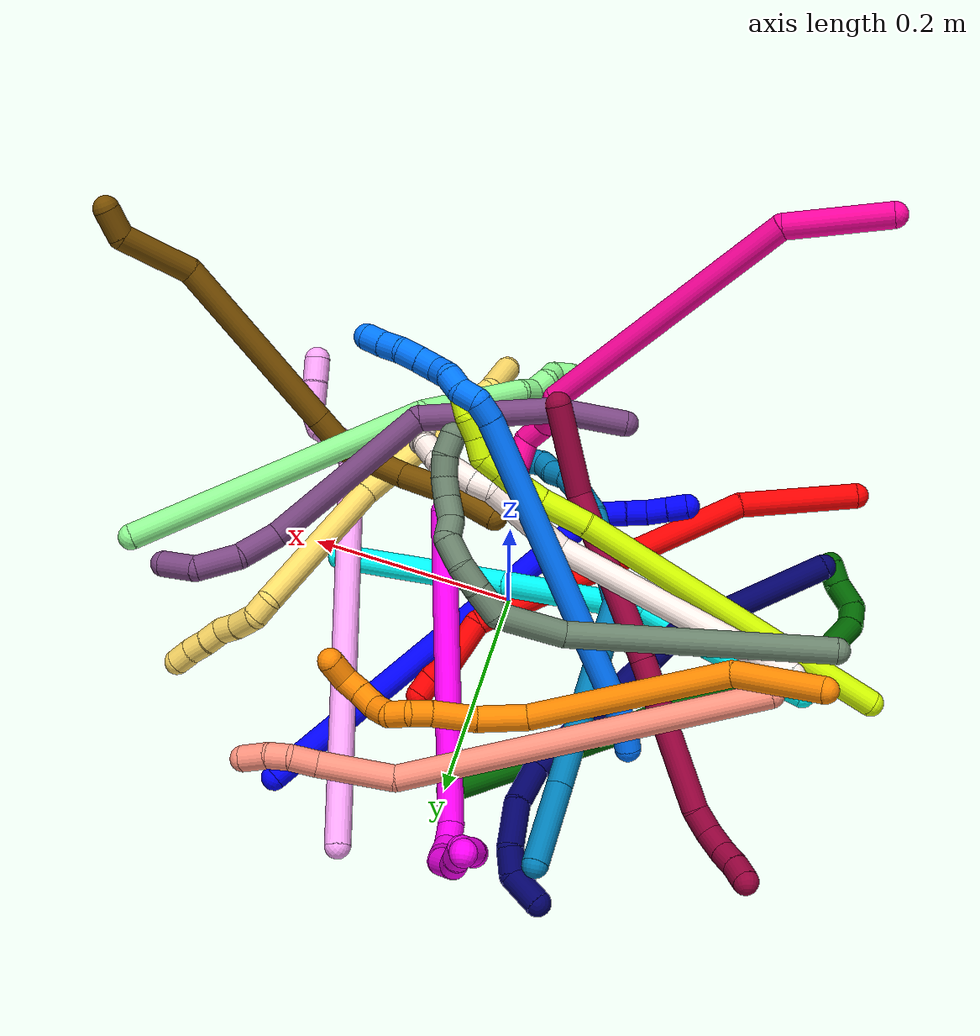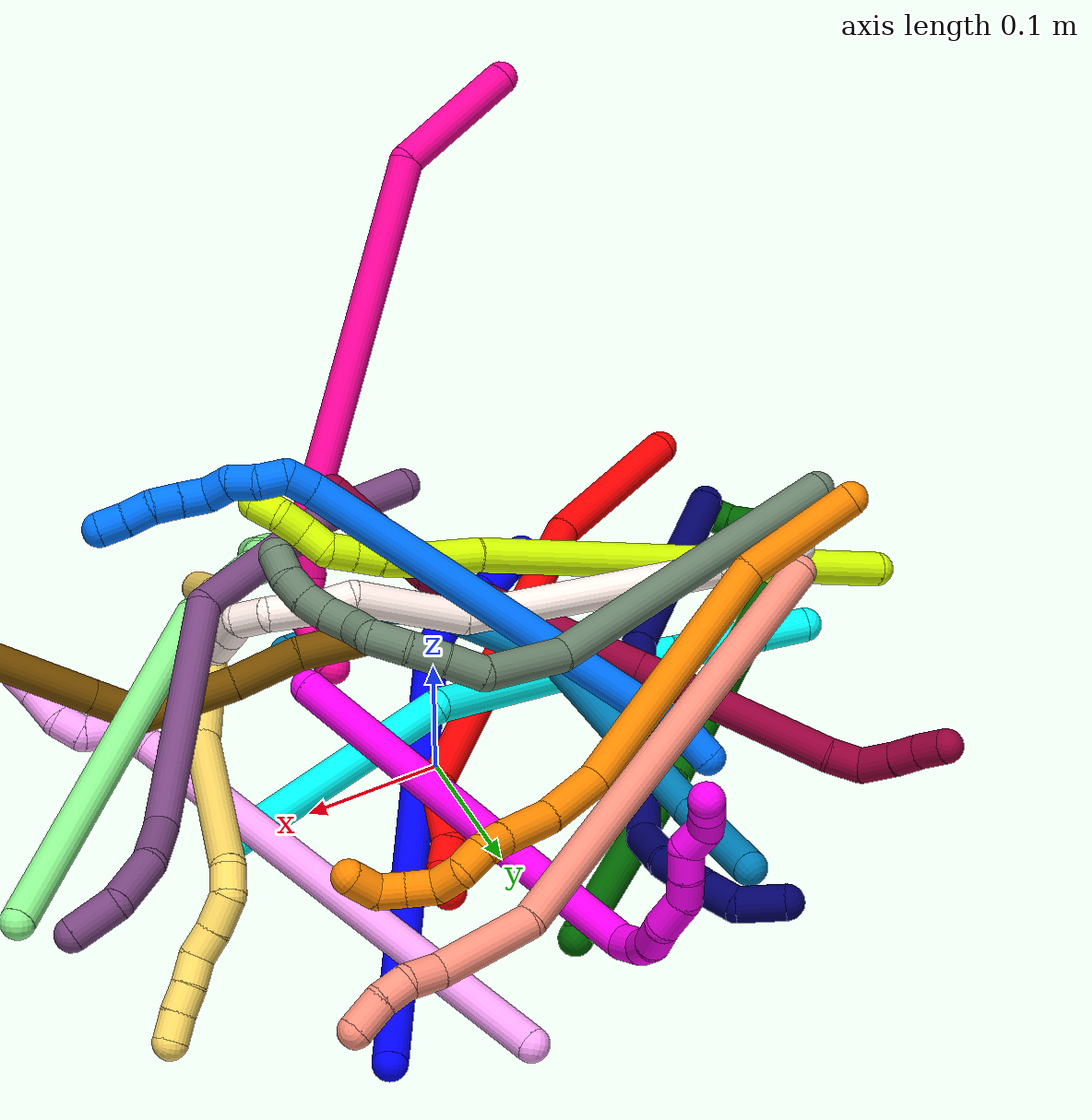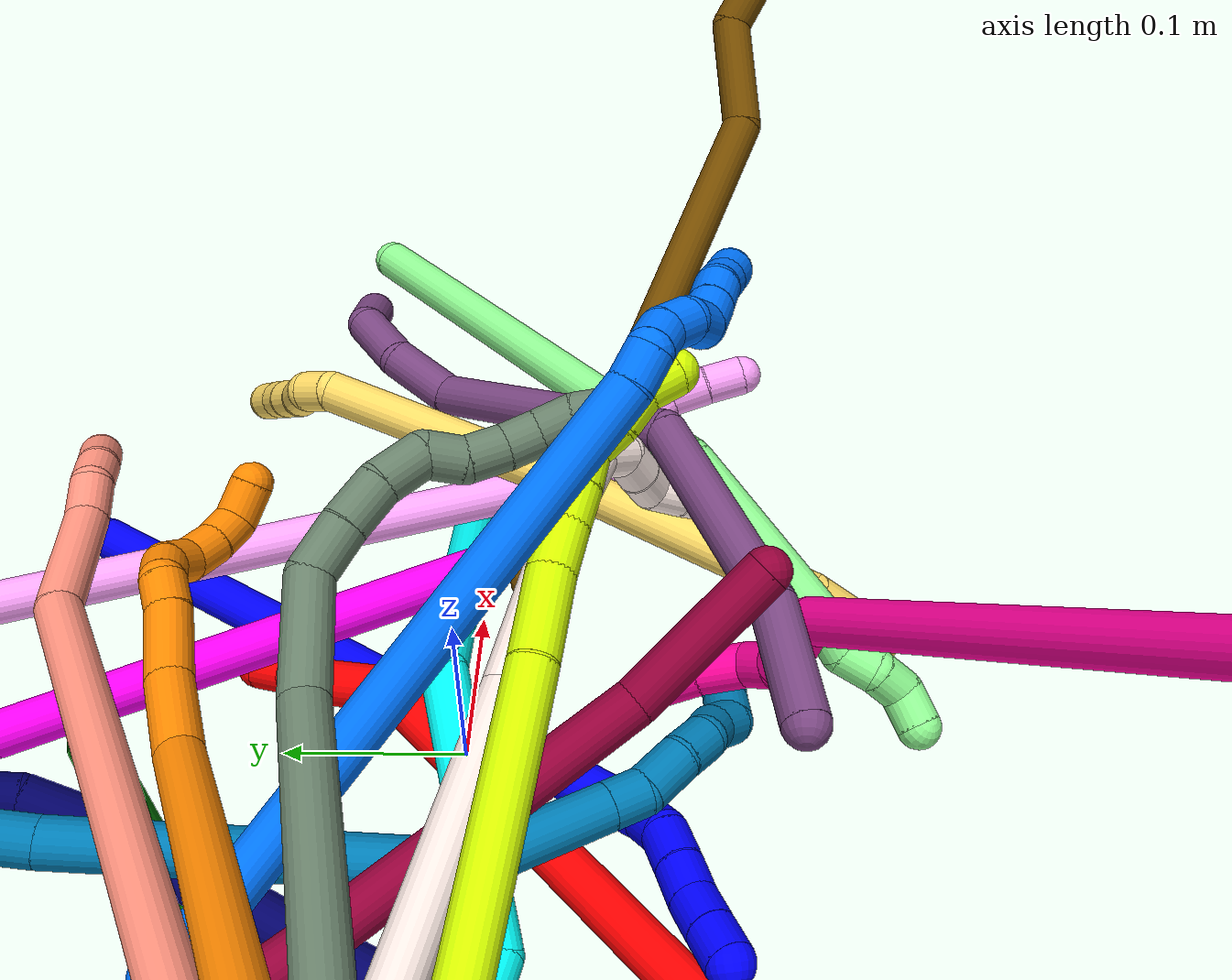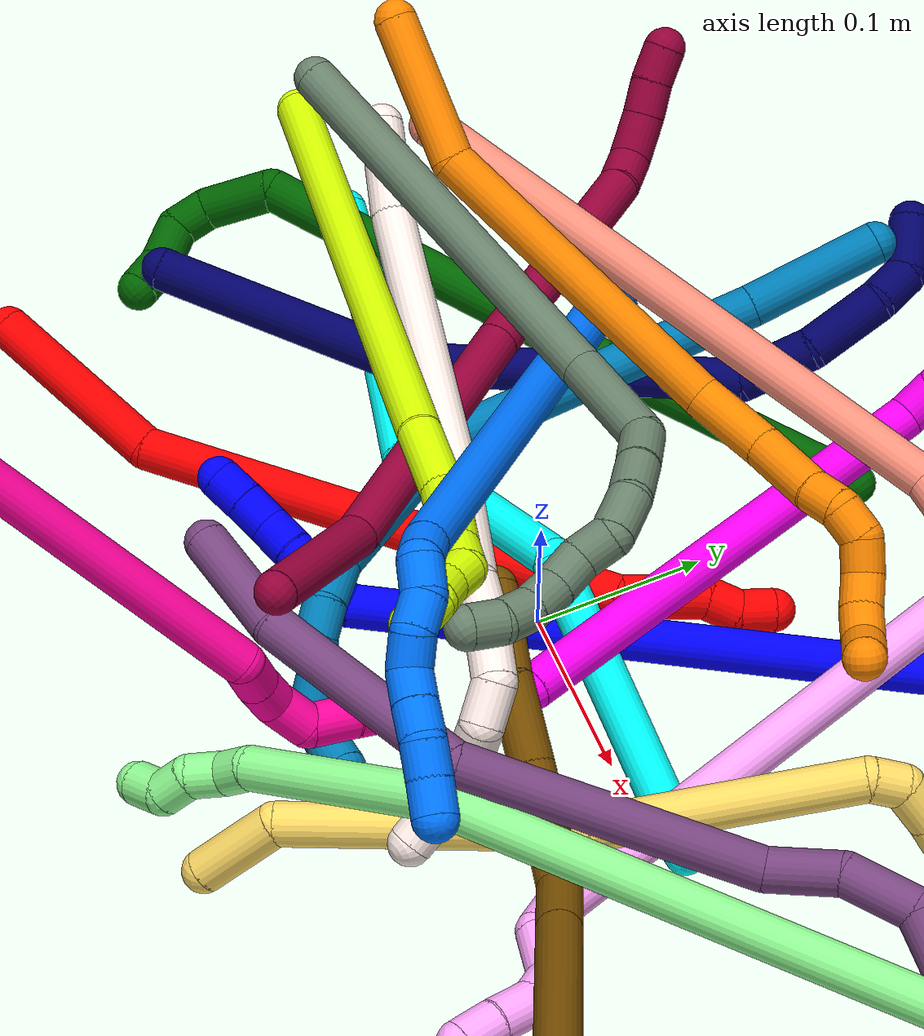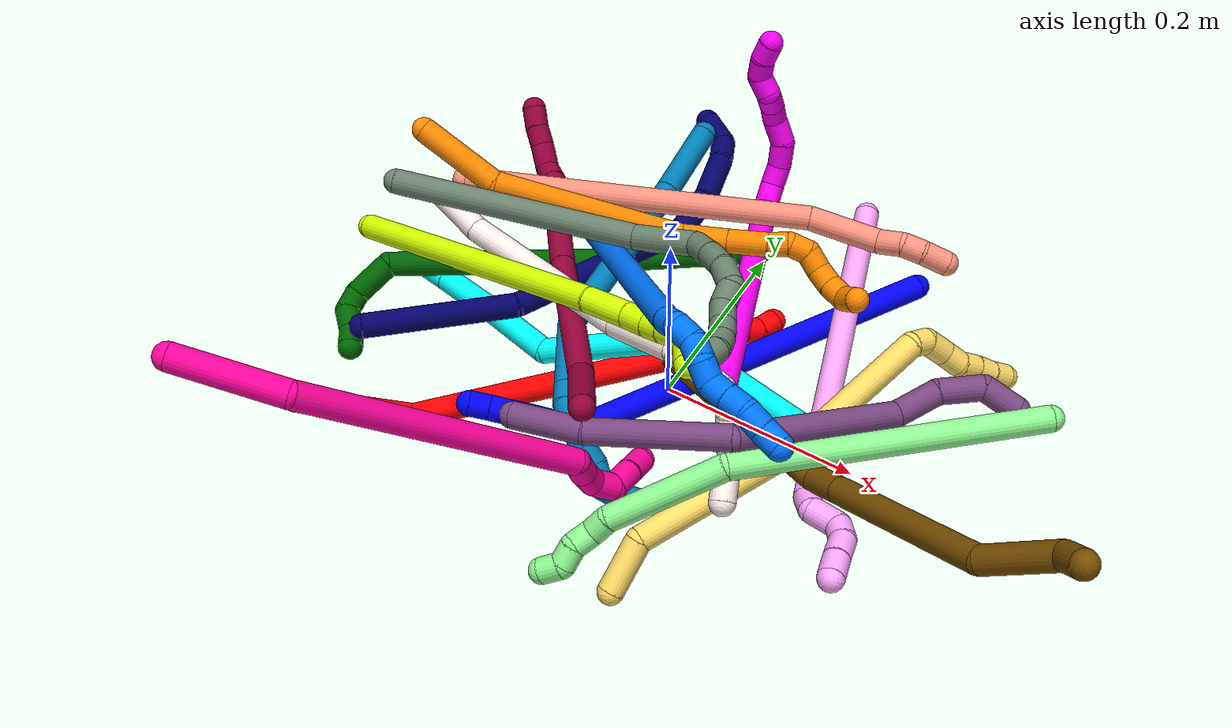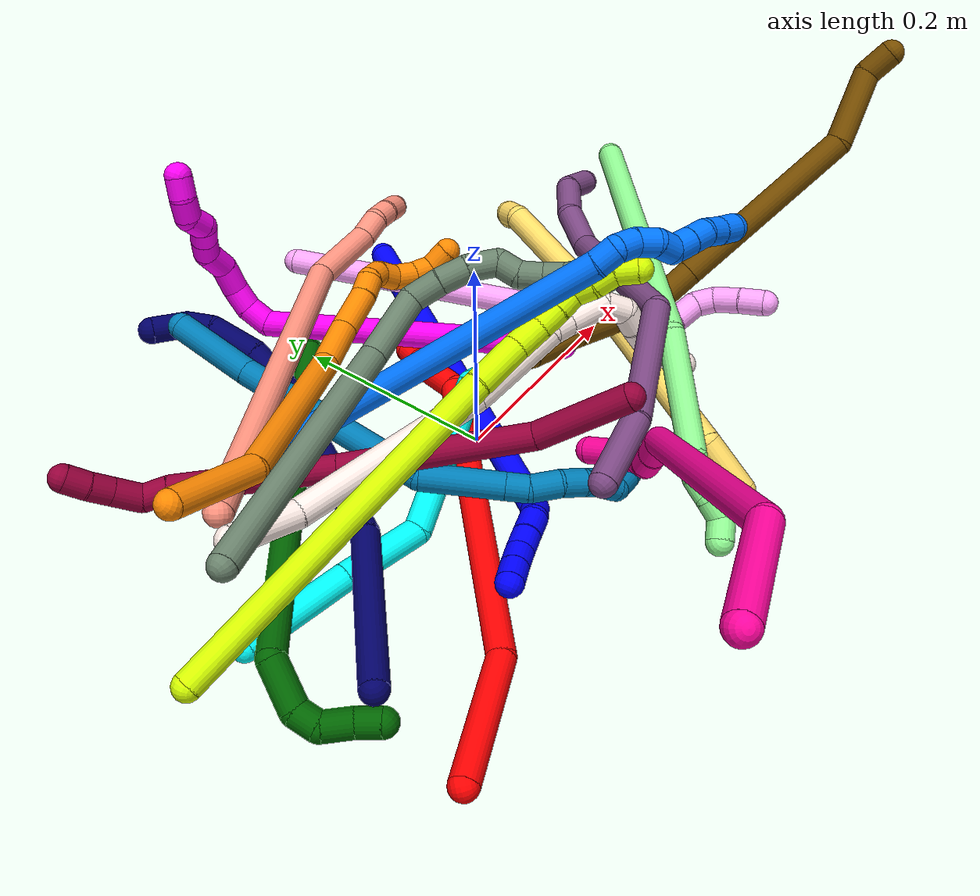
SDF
<sdf version="1.7">
 <world name="default">
  <plugin name="TubeGeneratorPlugin" filename="libtube_generator_plugin.so"/>
  <model name="photoneo_s_sensor">
   <static>1</static>
   <pose>0 0 2 1.57079 1.57079 3.14159</pose>
   <link name="link">
    <inertial><mass>0.1</mass></inertial>
    <sensor name="sensor" type="depth">
     <update_rate>30</update_rate>
     <camera>
      <horizontal_fov>1.22</horizontal_fov>
      <image><width>1920</width><height>1200</height><format>B8G8R8</format></image>
      <clip><near>0.1</near><far>4</far></clip>
      <depth_camera><output>points</output></depth_camera>
     </camera>
     <plugin name="camera_plugin" filename="libgazebo_ros_depth_camera.so">
      <baseline>0.2</baseline>
      <alwaysOn>1</alwaysOn>
      <updateRate>0.0</updateRate>
      <cameraName>camera_ir</cameraName>
      <imageTopicName>/camera/color/image_raw</imageTopicName>
      <cameraInfoTopicName>/camera/color/camera_info</cameraInfoTopicName>
      <depthImageTopicName>/camera/depth/image_raw</depthImageTopicName>
      <depthImageCameraInfoTopicName>/camera/depth/camera_info</depthImageCameraInfoTopicName>
      <pointCloudTopicName>/camera/depth/points</pointCloudTopicName>
      <frameName>fr_optical</frameName>
      <pointCloudCutoff>0.1</pointCloudCutoff>
      <pointCloudCutoffMax>2.0</pointCloudCutoffMax>
      <distortionK1>0</distortionK1>
      <distortionK2>0</distortionK2>
      <distortionK3>0</distortionK3>
      <distortionT1>0</distortionT1>
      <distortionT2>0</distortionT2>
      <CxPrime>0</CxPrime>
      <Cx>0</Cx>
      <Cy>0</Cy>
      <focalLength>0</focalLength>
      <hackBaseline>0</hackBaseline>
     </plugin>
    </sensor>
   </link>
  </model>
  <gravity>0 0 -9.8</gravity>
  <magnetic_field>6e-06 2.3e-05 -4.2e-05</magnetic_field>
  <atmosphere type="adiabatic"/>
  <physics name="default_physics" default="0" type="ode">
   <max_step_size>0.003</max_step_size>
   <real_time_factor>1</real_time_factor>
   <real_time_update_rate>1000</real_time_update_rate>
   <max_contacts>10000</max_contacts>
   <ode>
    <solver>
     <type>quick</type>
     <iters>100</iters>
     <sor>1.3</sor>
     <use_dynamic_moi_rescaling>0</use_dynamic_moi_rescaling>
    </solver>
    <constraints>
     <contact_max_correcting_vel>0</contact_max_correcting_vel>
     <contact_surface_layer>0.001</contact_surface_layer>
     <cfm>0</cfm>
     <erp>0.2</erp>
    </constraints>
   </ode>
  </physics>
  <scene><ambient>0.4 0.4 0.4 1</ambient><background>0.7 0.7 0.7 1</background><shadows>0</shadows></scene>
  <audio><device>default</device></audio>
  <spherical_coordinates>
   <surface_model>EARTH_WGS84</surface_model>
   <latitude_deg>0</latitude_deg>
   <longitude_deg>0</longitude_deg>
   <elevation>0</elevation>
   <heading_deg>0</heading_deg>
  </spherical_coordinates>
  <model name="bin">
   <static>1</static>
   <link name="bottom">
    <collision name="collision-bottom">
     <pose>0 0 -0.01 0 -0 0</pose>
     <geometry><box><size>0.8 0.6 0.02</size></box></geometry>
     <surface>
      <friction><ode><mu>100</mu><mu2>100</mu2></ode></friction>
      <contact><collide_bitmask>65535</collide_bitmask></contact>
     </surface>
    </collision>
   </link>
   <link name="west_wall">
    <collision name="collision-west_wall">
     <pose>-0.41 0 0.1 0 -0 0</pose>
     <geometry><box><size>0.02 0.6 0.2</size></box></geometry>
     <surface>
      <friction><ode><mu>100</mu><mu2>100</mu2></ode></friction>
      <contact><collide_bitmask>65535</collide_bitmask></contact>
     </surface>
    </collision>
   </link>
   <link name="east_wall">
    <collision name="collision-east_wall">
     <pose>0.41 0 0.1 0 -0 0</pose>
     <geometry><box><size>0.02 0.6 0.2</size></box></geometry>
     <surface>
      <friction><ode><mu>100</mu><mu2>100</mu2></ode></friction>
      <contact><collide_bitmask>65535</collide_bitmask></contact>
     </surface>
    </collision>
   </link>
   <link name="south_wall">
    <collision name="collision-south_wall">
     <pose>0 -0.31 0.1 0 -0 0</pose>
     <geometry><box><size>0.8 0.02 0.2</size></box></geometry>
     <surface>
      <friction><ode><mu>100</mu><mu2>100</mu2></ode></friction>
      <contact><collide_bitmask>65535</collide_bitmask></contact>
     </surface>
    </collision>
   </link>
   <link name="north_wall">
    <collision name="collision-north_wall">
     <pose>0 0.31 0.1 0 -0 0</pose>
     <geometry><box><size>0.8 0.02 0.2</size></box></geometry>
     <surface>
      <friction><ode><mu>100</mu><mu2>100</mu2></ode></friction>
      <contact><collide_bitmask>65535</collide_bitmask></contact>
     </surface>
    </collision>
   </link>
  </model>
  <model name="1">
   <static>0</static>
   <link name="1">
    <collision name="collision-cylinder-e_1_1_4">
     <pose>-0.087661 -0.138229 0.10966 0.90014 -0.461099 -0.225844</pose>
     <geometry><cylinder><radius>0.0125</radius><length>0.394041</length></cylinder></geometry>
     <surface>
      <friction><ode><mu>1.16</mu><mu2>1.16</mu2><slip1>0</slip1><slip2>0</slip2></ode></friction>
      <contact><ode><kp>1e+06</kp><kd>1</kd><max_vel>0</max_vel><min_depth>0.001</min_depth></ode></contact>
     </surface>
    </collision>
    <visual name="visual-cylinder-e_1_1_4">
     <pose>-0.087661 -0.138229 0.10966 0.90014 -0.461099 -0.225844</pose>
     <geometry><cylinder><radius>0.0125</radius><length>0.394041</length></cylinder></geometry>
     <material><ambient>0 0 1 1</ambient></material>
    </visual>
    <collision name="collision-cylinder-e_2_4_5">
     <pose>-0.173062 -0.286502 0.22463 1.08451 0.196369 0.118554</pose>
     <geometry><cylinder><radius>0.0125</radius><length>0.023167</length></cylinder></geometry>
     <surface>
      <friction><ode><mu>1.16</mu><mu2>1.16</mu2><slip1>0</slip1><slip2>0</slip2></ode></friction>
      <contact><ode><kp>1e+06</kp><kd>1</kd><max_vel>0</max_vel><min_depth>0.001</min_depth></ode></contact>
     </surface>
    </collision>
    <visual name="visual-cylinder-e_2_4_5">
     <pose>-0.173062 -0.286502 0.22463 1.08451 0.196369 0.118554</pose>
     <geometry><cylinder><radius>0.0125</radius><length>0.023167</length></cylinder></geometry>
     <material><ambient>0 0 1 1</ambient></material>
    </visual>
    <collision name="collision-cylinder-e_3_5_6">
     <pose>-0.168375 -0.303322 0.238568 0.665735 0.217689 0.075525</pose>
     <geometry><cylinder><radius>0.0125</radius><length>0.022472</length></cylinder></geometry>
     <surface>
      <friction><ode><mu>1.16</mu><mu2>1.16</mu2><slip1>0</slip1><slip2>0</slip2></ode></friction>
      <contact><ode><kp>1e+06</kp><kd>1</kd><max_vel>0</max_vel><min_depth>0.001</min_depth></ode></contact>
     </surface>
    </collision>
    <visual name="visual-cylinder-e_3_5_6">
     <pose>-0.168375 -0.303322 0.238568 0.665735 0.217689 0.075525</pose>
     <geometry><cylinder><radius>0.0125</radius><length>0.022472</length></cylinder></geometry>
     <material><ambient>0 0 1 1</ambient></material>
    </visual>
    <collision name="collision-cylinder-e_4_6_7">
     <pose>-0.16413 -0.315647 0.255399 0.594744 0.181602 0.055793</pose>
     <geometry><cylinder><radius>0.0125</radius><length>0.02014</length></cylinder></geometry>
     <surface>
      <friction><ode><mu>1.16</mu><mu2>1.16</mu2><slip1>0</slip1><slip2>0</slip2></ode></friction>
      <contact><ode><kp>1e+06</kp><kd>1</kd><max_vel>0</max_vel><min_depth>0.001</min_depth></ode></contact>
     </surface>
    </collision>
    <visual name="visual-cylinder-e_4_6_7">
     <pose>-0.16413 -0.315647 0.255399 0.594744 0.181602 0.055793</pose>
     <geometry><cylinder><radius>0.0125</radius><length>0.02014</length></cylinder></geometry>
     <material><ambient>0 0 1 1</ambient></material>
    </visual>
    <collision name="collision-cylinder-e_5_7_8">
     <pose>-0.160406 -0.327988 0.270786 0.757379 0.190414 0.075958</pose>
     <geometry><cylinder><radius>0.0125</radius><length>0.020134</length></cylinder></geometry>
     <surface>
      <friction><ode><mu>1.16</mu><mu2>1.16</mu2><slip1>0</slip1><slip2>0</slip2></ode></friction>
      <contact><ode><kp>1e+06</kp><kd>1</kd><max_vel>0</max_vel><min_depth>0.001</min_depth></ode></contact>
     </surface>
    </collision>
    <visual name="visual-cylinder-e_5_7_8">
     <pose>-0.160406 -0.327988 0.270786 0.757379 0.190414 0.075958</pose>
     <geometry><cylinder><radius>0.0125</radius><length>0.020134</length></cylinder></geometry>
     <material><ambient>0 0 1 1</ambient></material>
    </visual>
    <collision name="collision-cylinder-e_6_8_2">
     <pose>-0.15695 -0.341437 0.285299 0.737408 0.155327 0.060117</pose>
     <geometry><cylinder><radius>0.0125</radius><length>0.020046</length></cylinder></geometry>
     <surface>
      <friction><ode><mu>1.16</mu><mu2>1.16</mu2><slip1>0</slip1><slip2>0</slip2></ode></friction>
      <contact><ode><kp>1e+06</kp><kd>1</kd><max_vel>0</max_vel><min_depth>0.001</min_depth></ode></contact>
     </surface>
    </collision>
    <visual name="visual-cylinder-e_6_8_2">
     <pose>-0.15695 -0.341437 0.285299 0.737408 0.155327 0.060117</pose>
     <geometry><cylinder><radius>0.0125</radius><length>0.020046</length></cylinder></geometry>
     <material><ambient>0 0 1 1</ambient></material>
    </visual>
    <collision name="collision-sphere-2">
     <pose>-0.155399 -0.348095 0.292629 0 -0 0</pose>
     <geometry><sphere><radius>0.0125</radius></sphere></geometry>
     <surface>
      <friction><ode><mu>1.16</mu><mu2>1.16</mu2><slip1>0</slip1><slip2>0</slip2></ode></friction>
      <contact><ode><kp>1e+06</kp><kd>1</kd><max_vel>0</max_vel><min_depth>0.001</min_depth></ode></contact>
     </surface>
    </collision>
    <visual name="visual-sphere-2">
     <pose>-0.155399 -0.348095 0.292629 0 -0 0</pose>
     <geometry><sphere><radius>0.0125</radius></sphere></geometry>
     <material><ambient>0 0 1 1</ambient></material>
    </visual>
    <collision name="collision-sphere-4">
     <pose>-0.175322 -0.276458 0.219321 0 -0 0</pose>
     <geometry><sphere><radius>0.0125</radius></sphere></geometry>
     <surface>
      <friction><ode><mu>1.16</mu><mu2>1.16</mu2><slip1>0</slip1><slip2>0</slip2></ode></friction>
      <contact><ode><kp>1e+06</kp><kd>1</kd><max_vel>0</max_vel><min_depth>0.001</min_depth></ode></contact>
     </surface>
    </collision>
    <visual name="visual-sphere-4">
     <pose>-0.175322 -0.276458 0.219321 0 -0 0</pose>
     <geometry><sphere><radius>0.0125</radius></sphere></geometry>
     <material><ambient>0 0 1 1</ambient></material>
    </visual>
    <collision name="collision-sphere-1">
     <geometry><sphere><radius>0.0125</radius></sphere></geometry>
     <surface>
      <friction><ode><mu>1.16</mu><mu2>1.16</mu2><slip1>0</slip1><slip2>0</slip2></ode></friction>
      <contact><ode><kp>1e+06</kp><kd>1</kd><max_vel>0</max_vel><min_depth>0.001</min_depth></ode></contact>
     </surface>
    </collision>
    <visual name="visual-sphere-1">
     <geometry><sphere><radius>0.0125</radius></sphere></geometry>
     <material><ambient>0 0 1 1</ambient></material>
    </visual>
    <collision name="collision-sphere-8">
     <pose>-0.1585 -0.334779 0.277969 0 -0 0</pose>
     <geometry><sphere><radius>0.0125</radius></sphere></geometry>
     <surface>
      <friction><ode><mu>1.16</mu><mu2>1.16</mu2><slip1>0</slip1><slip2>0</slip2></ode></friction>
      <contact><ode><kp>1e+06</kp><kd>1</kd><max_vel>0</max_vel><min_depth>0.001</min_depth></ode></contact>
     </surface>
    </collision>
    <visual name="visual-sphere-8">
     <pose>-0.1585 -0.334779 0.277969 0 -0 0</pose>
     <geometry><sphere><radius>0.0125</radius></sphere></geometry>
     <material><ambient>0 0 1 1</ambient></material>
    </visual>
    <collision name="collision-sphere-5">
     <pose>-0.170802 -0.296546 0.22994 0 -0 0</pose>
     <geometry><sphere><radius>0.0125</radius></sphere></geometry>
     <surface>
      <friction><ode><mu>1.16</mu><mu2>1.16</mu2><slip1>0</slip1><slip2>0</slip2></ode></friction>
      <contact><ode><kp>1e+06</kp><kd>1</kd><max_vel>0</max_vel><min_depth>0.001</min_depth></ode></contact>
     </surface>
    </collision>
    <visual name="visual-sphere-5">
     <pose>-0.170802 -0.296546 0.22994 0 -0 0</pose>
     <geometry><sphere><radius>0.0125</radius></sphere></geometry>
     <material><ambient>0 0 1 1</ambient></material>
    </visual>
    <collision name="collision-sphere-6">
     <pose>-0.165948 -0.310098 0.247196 0 -0 0</pose>
     <geometry><sphere><radius>0.0125</radius></sphere></geometry>
     <surface>
      <friction><ode><mu>1.16</mu><mu2>1.16</mu2><slip1>0</slip1><slip2>0</slip2></ode></friction>
      <contact><ode><kp>1e+06</kp><kd>1</kd><max_vel>0</max_vel><min_depth>0.001</min_depth></ode></contact>
     </surface>
    </collision>
    <visual name="visual-sphere-6">
     <pose>-0.165948 -0.310098 0.247196 0 -0 0</pose>
     <geometry><sphere><radius>0.0125</radius></sphere></geometry>
     <material><ambient>0 0 1 1</ambient></material>
    </visual>
    <collision name="collision-sphere-7">
     <pose>-0.162311 -0.321197 0.263603 0 -0 0</pose>
     <geometry><sphere><radius>0.0125</radius></sphere></geometry>
     <surface>
      <friction><ode><mu>1.16</mu><mu2>1.16</mu2><slip1>0</slip1><slip2>0</slip2></ode></friction>
      <contact><ode><kp>1e+06</kp><kd>1</kd><max_vel>0</max_vel><min_depth>0.001</min_depth></ode></contact>
     </surface>
    </collision>
    <visual name="visual-sphere-7">
     <pose>-0.162311 -0.321197 0.263603 0 -0 0</pose>
     <geometry><sphere><radius>0.0125</radius></sphere></geometry>
     <material><ambient>0 0 1 1</ambient></material>
    </visual>
    <inertial>
     <pose>-0.104033 -0.175454 0.140181 0 -0 0</pose>
     <mass>0.5</mass>
     <inertia><ixx>0.003434</ixx><ixy>0</ixy><ixz>0</ixz><iyy>0.00245</iyy><iyz>0</iyz><izz>0.00589</izz></inertia>
    </inertial>
   </link>
   <pose>0.156542 0.240825 0.011516 -2.19637 -0.499641 2.06819</pose>
  </model>
  <model name="2">
   <static>0</static>
   <link name="2">
    <collision name="collision-cylinder-e_1_1_4">
     <pose>0.047054 0.029443 0.017783 -1.02746 0.939561 -0.558002</pose>
     <geometry><cylinder><radius>0.0125</radius><length>0.11657</length></cylinder></geometry>
     <surface>
      <friction><ode><mu>1.16</mu><mu2>1.16</mu2><slip1>0</slip1><slip2>0</slip2></ode></friction>
      <contact><ode><kp>1e+06</kp><kd>1</kd><max_vel>0</max_vel><min_depth>0.001</min_depth></ode></contact>
     </surface>
    </collision>
    <visual name="visual-cylinder-e_1_1_4">
     <pose>0.047054 0.029443 0.017783 -1.02746 0.939561 -0.558002</pose>
     <geometry><cylinder><radius>0.0125</radius><length>0.11657</length></cylinder></geometry>
     <material><ambient>1 0 0 1</ambient></material>
    </visual>
    <collision name="collision-cylinder-e_2_4_5">
     <pose>0.200089 0.159448 0.030215 -1.62395 0.810927 -0.850184</pose>
     <geometry><cylinder><radius>0.0125</radius><length>0.292393</length></cylinder></geometry>
     <surface>
      <friction><ode><mu>1.16</mu><mu2>1.16</mu2><slip1>0</slip1><slip2>0</slip2></ode></friction>
      <contact><ode><kp>1e+06</kp><kd>1</kd><max_vel>0</max_vel><min_depth>0.001</min_depth></ode></contact>
     </surface>
    </collision>
    <visual name="visual-cylinder-e_2_4_5">
     <pose>0.200089 0.159448 0.030215 -1.62395 0.810927 -0.850184</pose>
     <geometry><cylinder><radius>0.0125</radius><length>0.292393</length></cylinder></geometry>
     <material><ambient>1 0 0 1</ambient></material>
    </visual>
    <collision name="collision-cylinder-e_3_5_6">
     <pose>0.323056 0.272101 0.011044 -2.42283 0.746458 -1.61219</pose>
     <geometry><cylinder><radius>0.0125</radius><length>0.050029</length></cylinder></geometry>
     <surface>
      <friction><ode><mu>1.16</mu><mu2>1.16</mu2><slip1>0</slip1><slip2>0</slip2></ode></friction>
      <contact><ode><kp>1e+06</kp><kd>1</kd><max_vel>0</max_vel><min_depth>0.001</min_depth></ode></contact>
     </surface>
    </collision>
    <visual name="visual-cylinder-e_3_5_6">
     <pose>0.323056 0.272101 0.011044 -2.42283 0.746458 -1.61219</pose>
     <geometry><cylinder><radius>0.0125</radius><length>0.050029</length></cylinder></geometry>
     <material><ambient>1 0 0 1</ambient></material>
    </visual>
    <collision name="collision-cylinder-e_4_6_7">
     <pose>0.349275 0.287813 -0.005351 -2.18885 1.12229 -1.76681</pose>
     <geometry><cylinder><radius>0.0125</radius><length>0.020494</length></cylinder></geometry>
     <surface>
      <friction><ode><mu>1.16</mu><mu2>1.16</mu2><slip1>0</slip1><slip2>0</slip2></ode></friction>
      <contact><ode><kp>1e+06</kp><kd>1</kd><max_vel>0</max_vel><min_depth>0.001</min_depth></ode></contact>
     </surface>
    </collision>
    <visual name="visual-cylinder-e_4_6_7">
     <pose>0.349275 0.287813 -0.005351 -2.18885 1.12229 -1.76681</pose>
     <geometry><cylinder><radius>0.0125</radius><length>0.020494</length></cylinder></geometry>
     <material><ambient>1 0 0 1</ambient></material>
    </visual>
    <collision name="collision-cylinder-e_5_7_2">
     <pose>0.364992 0.29729 -0.0133 -2.31344 0.684244 -1.36201</pose>
     <geometry><cylinder><radius>0.0125</radius><length>0.020514</length></cylinder></geometry>
     <surface>
      <friction><ode><mu>1.16</mu><mu2>1.16</mu2><slip1>0</slip1><slip2>0</slip2></ode></friction>
      <contact><ode><kp>1e+06</kp><kd>1</kd><max_vel>0</max_vel><min_depth>0.001</min_depth></ode></contact>
     </surface>
    </collision>
    <visual name="visual-cylinder-e_5_7_2">
     <pose>0.364992 0.29729 -0.0133 -2.31344 0.684244 -1.36201</pose>
     <geometry><cylinder><radius>0.0125</radius><length>0.020514</length></cylinder></geometry>
     <material><ambient>1 0 0 1</ambient></material>
    </visual>
    <collision name="collision-sphere-2">
     <pose>0.371476 0.303145 -0.018675 0 -0 0</pose>
     <geometry><sphere><radius>0.0125</radius></sphere></geometry>
     <surface>
      <friction><ode><mu>1.16</mu><mu2>1.16</mu2><slip1>0</slip1><slip2>0</slip2></ode></friction>
      <contact><ode><kp>1e+06</kp><kd>1</kd><max_vel>0</max_vel><min_depth>0.001</min_depth></ode></contact>
     </surface>
    </collision>
    <visual name="visual-sphere-2">
     <pose>0.371476 0.303145 -0.018675 0 -0 0</pose>
     <geometry><sphere><radius>0.0125</radius></sphere></geometry>
     <material><ambient>1 0 0 1</ambient></material>
    </visual>
    <collision name="collision-sphere-7">
     <pose>0.358509 0.291435 -0.007925 0 -0 0</pose>
     <geometry><sphere><radius>0.0125</radius></sphere></geometry>
     <surface>
      <friction><ode><mu>1.16</mu><mu2>1.16</mu2><slip1>0</slip1><slip2>0</slip2></ode></friction>
      <contact><ode><kp>1e+06</kp><kd>1</kd><max_vel>0</max_vel><min_depth>0.001</min_depth></ode></contact>
     </surface>
    </collision>
    <visual name="visual-sphere-7">
     <pose>0.358509 0.291435 -0.007925 0 -0 0</pose>
     <geometry><sphere><radius>0.0125</radius></sphere></geometry>
     <material><ambient>1 0 0 1</ambient></material>
    </visual>
    <collision name="collision-sphere-6">
     <pose>0.340042 0.284192 -0.002776 0 -0 0</pose>
     <geometry><sphere><radius>0.0125</radius></sphere></geometry>
     <surface>
      <friction><ode><mu>1.16</mu><mu2>1.16</mu2><slip1>0</slip1><slip2>0</slip2></ode></friction>
      <contact><ode><kp>1e+06</kp><kd>1</kd><max_vel>0</max_vel><min_depth>0.001</min_depth></ode></contact>
     </surface>
    </collision>
    <visual name="visual-sphere-6">
     <pose>0.340042 0.284192 -0.002776 0 -0 0</pose>
     <geometry><sphere><radius>0.0125</radius></sphere></geometry>
     <material><ambient>1 0 0 1</ambient></material>
    </visual>
    <collision name="collision-sphere-5">
     <pose>0.30607 0.260009 0.024865 0 -0 0</pose>
     <geometry><sphere><radius>0.0125</radius></sphere></geometry>
     <surface>
      <friction><ode><mu>1.16</mu><mu2>1.16</mu2><slip1>0</slip1><slip2>0</slip2></ode></friction>
      <contact><ode><kp>1e+06</kp><kd>1</kd><max_vel>0</max_vel><min_depth>0.001</min_depth></ode></contact>
     </surface>
    </collision>
    <visual name="visual-sphere-5">
     <pose>0.30607 0.260009 0.024865 0 -0 0</pose>
     <geometry><sphere><radius>0.0125</radius></sphere></geometry>
     <material><ambient>1 0 0 1</ambient></material>
    </visual>
    <collision name="collision-sphere-1">
     <geometry><sphere><radius>0.0125</radius></sphere></geometry>
     <surface>
      <friction><ode><mu>1.16</mu><mu2>1.16</mu2><slip1>0</slip1><slip2>0</slip2></ode></friction>
      <contact><ode><kp>1e+06</kp><kd>1</kd><max_vel>0</max_vel><min_depth>0.001</min_depth></ode></contact>
     </surface>
    </collision>
    <visual name="visual-sphere-1">
     <geometry><sphere><radius>0.0125</radius></sphere></geometry>
     <material><ambient>1 0 0 1</ambient></material>
    </visual>
    <collision name="collision-sphere-4">
     <pose>0.094107 0.058886 0.035565 0 -0 0</pose>
     <geometry><sphere><radius>0.0125</radius></sphere></geometry>
     <surface>
      <friction><ode><mu>1.16</mu><mu2>1.16</mu2><slip1>0</slip1><slip2>0</slip2></ode></friction>
      <contact><ode><kp>1e+06</kp><kd>1</kd><max_vel>0</max_vel><min_depth>0.001</min_depth></ode></contact>
     </surface>
    </collision>
    <visual name="visual-sphere-4">
     <pose>0.094107 0.058886 0.035565 0 -0 0</pose>
     <geometry><sphere><radius>0.0125</radius></sphere></geometry>
     <material><ambient>1 0 0 1</ambient></material>
    </visual>
    <inertial>
     <pose>0.189594 0.151327 0.022155 0 -0 0</pose>
     <mass>0.5</mass>
     <inertia>
      <ixx>-8.9e-05</ixx>
      <ixy>0</ixy>
      <ixz>0</ixz>
      <iyy>6.9e-05</iyy>
      <iyz>0</iyz>
      <izz>-0.003158</izz>
     </inertia>
    </inertial>
   </link>
   <pose>-0.297444 -0.206822 0.015191 1.23165 0.65195 0.506244</pose>
  </model>
  <model name="3">
   <static>0</static>
   <link name="3">
    <collision name="collision-cylinder-e_1_1_4">
     <pose>-0.048082 0.030515 0.068901 -0.416912 -0.567942 0.123316</pose>
     <geometry><cylinder><radius>0.0125</radius><length>0.178779</length></cylinder></geometry>
     <surface>
      <friction><ode><mu>1.16</mu><mu2>1.16</mu2><slip1>0</slip1><slip2>0</slip2></ode></friction>
      <contact><ode><kp>1e+06</kp><kd>1</kd><max_vel>0</max_vel><min_depth>0.001</min_depth></ode></contact>
     </surface>
    </collision>
    <visual name="visual-cylinder-e_1_1_4">
     <pose>-0.048082 0.030515 0.068901 -0.416912 -0.567942 0.123316</pose>
     <geometry><cylinder><radius>0.0125</radius><length>0.178779</length></cylinder></geometry>
     <material><ambient>0.003922 1 0.996078 1</ambient></material>
    </visual>
    <collision name="collision-cylinder-e_2_4_5">
     <pose>-0.145828 0.034351 0.182445 0.538664 -0.762353 -0.220365</pose>
     <geometry><cylinder><radius>0.0125</radius><length>0.14382</length></cylinder></geometry>
     <surface>
      <friction><ode><mu>1.16</mu><mu2>1.16</mu2><slip1>0</slip1><slip2>0</slip2></ode></friction>
      <contact><ode><kp>1e+06</kp><kd>1</kd><max_vel>0</max_vel><min_depth>0.001</min_depth></ode></contact>
     </surface>
    </collision>
    <visual name="visual-cylinder-e_2_4_5">
     <pose>-0.145828 0.034351 0.182445 0.538664 -0.762353 -0.220365</pose>
     <geometry><cylinder><radius>0.0125</radius><length>0.14382</length></cylinder></geometry>
     <material><ambient>0.003922 1 0.996078 1</ambient></material>
    </visual>
    <collision name="collision-cylinder-e_3_5_6">
     <pose>-0.227383 0.016741 0.246705 -0.433008 -0.975187 0.232232</pose>
     <geometry><cylinder><radius>0.0125</radius><length>0.077052</length></cylinder></geometry>
     <surface>
      <friction><ode><mu>1.16</mu><mu2>1.16</mu2><slip1>0</slip1><slip2>0</slip2></ode></friction>
      <contact><ode><kp>1e+06</kp><kd>1</kd><max_vel>0</max_vel><min_depth>0.001</min_depth></ode></contact>
     </surface>
    </collision>
    <visual name="visual-cylinder-e_3_5_6">
     <pose>-0.227383 0.016741 0.246705 -0.433008 -0.975187 0.232232</pose>
     <geometry><cylinder><radius>0.0125</radius><length>0.077052</length></cylinder></geometry>
     <material><ambient>0.003922 1 0.996078 1</ambient></material>
    </visual>
    <collision name="collision-cylinder-e_4_6_7">
     <pose>-0.286069 0.032523 0.284187 -0.359483 -0.951937 0.186789</pose>
     <geometry><cylinder><radius>0.0125</radius><length>0.06579</length></cylinder></geometry>
     <surface>
      <friction><ode><mu>1.16</mu><mu2>1.16</mu2><slip1>0</slip1><slip2>0</slip2></ode></friction>
      <contact><ode><kp>1e+06</kp><kd>1</kd><max_vel>0</max_vel><min_depth>0.001</min_depth></ode></contact>
     </surface>
    </collision>
    <visual name="visual-cylinder-e_4_6_7">
     <pose>-0.286069 0.032523 0.284187 -0.359483 -0.951937 0.186789</pose>
     <geometry><cylinder><radius>0.0125</radius><length>0.06579</length></cylinder></geometry>
     <material><ambient>0.003922 1 0.996078 1</ambient></material>
    </visual>
    <collision name="collision-cylinder-e_5_7_2">
     <pose>-0.326921 0.042712 0.311478 -0.353166 -0.950248 0.183078</pose>
     <geometry><cylinder><radius>0.0125</radius><length>0.034559</length></cylinder></geometry>
     <surface>
      <friction><ode><mu>1.16</mu><mu2>1.16</mu2><slip1>0</slip1><slip2>0</slip2></ode></friction>
      <contact><ode><kp>1e+06</kp><kd>1</kd><max_vel>0</max_vel><min_depth>0.001</min_depth></ode></contact>
     </surface>
    </collision>
    <visual name="visual-cylinder-e_5_7_2">
     <pose>-0.326921 0.042712 0.311478 -0.353166 -0.950248 0.183078</pose>
     <geometry><cylinder><radius>0.0125</radius><length>0.034559</length></cylinder></geometry>
     <material><ambient>0.003922 1 0.996078 1</ambient></material>
    </visual>
    <collision name="collision-sphere-2">
     <pose>-0.340979 0.046187 0.320905 0 -0 0</pose>
     <geometry><sphere><radius>0.0125</radius></sphere></geometry>
     <surface>
      <friction><ode><mu>1.16</mu><mu2>1.16</mu2><slip1>0</slip1><slip2>0</slip2></ode></friction>
      <contact><ode><kp>1e+06</kp><kd>1</kd><max_vel>0</max_vel><min_depth>0.001</min_depth></ode></contact>
     </surface>
    </collision>
    <visual name="visual-sphere-2">
     <pose>-0.340979 0.046187 0.320905 0 -0 0</pose>
     <geometry><sphere><radius>0.0125</radius></sphere></geometry>
     <material><ambient>0.003922 1 0.996078 1</ambient></material>
    </visual>
    <collision name="collision-sphere-7">
     <pose>-0.312863 0.039236 0.30205 0 -0 0</pose>
     <geometry><sphere><radius>0.0125</radius></sphere></geometry>
     <surface>
      <friction><ode><mu>1.16</mu><mu2>1.16</mu2><slip1>0</slip1><slip2>0</slip2></ode></friction>
      <contact><ode><kp>1e+06</kp><kd>1</kd><max_vel>0</max_vel><min_depth>0.001</min_depth></ode></contact>
     </surface>
    </collision>
    <visual name="visual-sphere-7">
     <pose>-0.312863 0.039236 0.30205 0 -0 0</pose>
     <geometry><sphere><radius>0.0125</radius></sphere></geometry>
     <material><ambient>0.003922 1 0.996078 1</ambient></material>
    </visual>
    <collision name="collision-sphere-6">
     <pose>-0.259275 0.02581 0.266324 0 -0 0</pose>
     <geometry><sphere><radius>0.0125</radius></sphere></geometry>
     <surface>
      <friction><ode><mu>1.16</mu><mu2>1.16</mu2><slip1>0</slip1><slip2>0</slip2></ode></friction>
      <contact><ode><kp>1e+06</kp><kd>1</kd><max_vel>0</max_vel><min_depth>0.001</min_depth></ode></contact>
     </surface>
    </collision>
    <visual name="visual-sphere-6">
     <pose>-0.259275 0.02581 0.266324 0 -0 0</pose>
     <geometry><sphere><radius>0.0125</radius></sphere></geometry>
     <material><ambient>0.003922 1 0.996078 1</ambient></material>
    </visual>
    <collision name="collision-sphere-5">
     <pose>-0.19549 0.007672 0.227087 0 -0 0</pose>
     <geometry><sphere><radius>0.0125</radius></sphere></geometry>
     <surface>
      <friction><ode><mu>1.16</mu><mu2>1.16</mu2><slip1>0</slip1><slip2>0</slip2></ode></friction>
      <contact><ode><kp>1e+06</kp><kd>1</kd><max_vel>0</max_vel><min_depth>0.001</min_depth></ode></contact>
     </surface>
    </collision>
    <visual name="visual-sphere-5">
     <pose>-0.19549 0.007672 0.227087 0 -0 0</pose>
     <geometry><sphere><radius>0.0125</radius></sphere></geometry>
     <material><ambient>0.003922 1 0.996078 1</ambient></material>
    </visual>
    <collision name="collision-sphere-1">
     <geometry><sphere><radius>0.0125</radius></sphere></geometry>
     <surface>
      <friction><ode><mu>1.16</mu><mu2>1.16</mu2><slip1>0</slip1><slip2>0</slip2></ode></friction>
      <contact><ode><kp>1e+06</kp><kd>1</kd><max_vel>0</max_vel><min_depth>0.001</min_depth></ode></contact>
     </surface>
    </collision>
    <visual name="visual-sphere-1">
     <geometry><sphere><radius>0.0125</radius></sphere></geometry>
     <material><ambient>0.003922 1 0.996078 1</ambient></material>
    </visual>
    <collision name="collision-sphere-4">
     <pose>-0.096165 0.061029 0.137803 0 -0 0</pose>
     <geometry><sphere><radius>0.0125</radius></sphere></geometry>
     <surface>
      <friction><ode><mu>1.16</mu><mu2>1.16</mu2><slip1>0</slip1><slip2>0</slip2></ode></friction>
      <contact><ode><kp>1e+06</kp><kd>1</kd><max_vel>0</max_vel><min_depth>0.001</min_depth></ode></contact>
     </surface>
    </collision>
    <visual name="visual-sphere-4">
     <pose>-0.096165 0.061029 0.137803 0 -0 0</pose>
     <geometry><sphere><radius>0.0125</radius></sphere></geometry>
     <material><ambient>0.003922 1 0.996078 1</ambient></material>
    </visual>
    <inertial>
     <pose>-0.154416 0.030603 0.174055 0 -0 0</pose>
     <mass>0.5</mass>
     <inertia>
      <ixx>0.000615</ixx>
      <ixy>0</ixy>
      <ixz>0</ixz>
      <iyy>0.000776</iyy>
      <iyz>0</iyz>
      <izz>0.000433</izz>
     </inertia>
    </inertial>
   </link>
   <pose>0.170926 0.011811 0.012284 1.16624 -0.461756 -0.62039</pose>
  </model>
  <model name="4">
   <static>0</static>
   <link name="4">
    <collision name="collision-cylinder-e_1_1_4">
     <pose>0.003681 -0.167025 -0.090285 2.06635 0.019385 0.032513</pose>
     <geometry><cylinder><radius>0.0125</radius><length>0.379802</length></cylinder></geometry>
     <surface>
      <friction><ode><mu>1.16</mu><mu2>1.16</mu2><slip1>0</slip1><slip2>0</slip2></ode></friction>
      <contact><ode><kp>1e+06</kp><kd>1</kd><max_vel>0</max_vel><min_depth>0.001</min_depth></ode></contact>
     </surface>
    </collision>
    <visual name="visual-cylinder-e_1_1_4">
     <pose>0.003681 -0.167025 -0.090285 2.06635 0.019385 0.032513</pose>
     <geometry><cylinder><radius>0.0125</radius><length>0.379802</length></cylinder></geometry>
     <material><ambient>1 0.65098 0.996078 1</ambient></material>
    </visual>
    <collision name="collision-cylinder-e_2_4_5">
     <pose>0.002375 -0.342255 -0.184808 2.04761 -0.495185 -0.786893</pose>
     <geometry><cylinder><radius>0.0125</radius><length>0.02099</length></cylinder></geometry>
     <surface>
      <friction><ode><mu>1.16</mu><mu2>1.16</mu2><slip1>0</slip1><slip2>0</slip2></ode></friction>
      <contact><ode><kp>1e+06</kp><kd>1</kd><max_vel>0</max_vel><min_depth>0.001</min_depth></ode></contact>
     </surface>
    </collision>
    <visual name="visual-cylinder-e_2_4_5">
     <pose>0.002375 -0.342255 -0.184808 2.04761 -0.495185 -0.786893</pose>
     <geometry><cylinder><radius>0.0125</radius><length>0.02099</length></cylinder></geometry>
     <material><ambient>1 0.65098 0.996078 1</ambient></material>
    </visual>
    <collision name="collision-cylinder-e_3_5_6">
     <pose>-0.012224 -0.360904 -0.184929 1.19529 -0.708067 -0.492942</pose>
     <geometry><cylinder><radius>0.0125</radius><length>0.029559</length></cylinder></geometry>
     <surface>
      <friction><ode><mu>1.16</mu><mu2>1.16</mu2><slip1>0</slip1><slip2>0</slip2></ode></friction>
      <contact><ode><kp>1e+06</kp><kd>1</kd><max_vel>0</max_vel><min_depth>0.001</min_depth></ode></contact>
     </surface>
    </collision>
    <visual name="visual-cylinder-e_3_5_6">
     <pose>-0.012224 -0.360904 -0.184929 1.19529 -0.708067 -0.492942</pose>
     <geometry><cylinder><radius>0.0125</radius><length>0.029559</length></cylinder></geometry>
     <material><ambient>1 0.65098 0.996078 1</ambient></material>
    </visual>
    <collision name="collision-cylinder-e_4_6_7">
     <pose>-0.025783 -0.379846 -0.184557 1.98587 -0.401841 -0.605439</pose>
     <geometry><cylinder><radius>0.0125</radius><length>0.02018</length></cylinder></geometry>
     <surface>
      <friction><ode><mu>1.16</mu><mu2>1.16</mu2><slip1>0</slip1><slip2>0</slip2></ode></friction>
      <contact><ode><kp>1e+06</kp><kd>1</kd><max_vel>0</max_vel><min_depth>0.001</min_depth></ode></contact>
     </surface>
    </collision>
    <visual name="visual-cylinder-e_4_6_7">
     <pose>-0.025783 -0.379846 -0.184557 1.98587 -0.401841 -0.605439</pose>
     <geometry><cylinder><radius>0.0125</radius><length>0.02018</length></cylinder></geometry>
     <material><ambient>1 0.65098 0.996078 1</ambient></material>
    </visual>
    <collision name="collision-cylinder-e_5_7_8">
     <pose>-0.03106 -0.397937 -0.196685 2.28899 -0.104074 -0.228371</pose>
     <geometry><cylinder><radius>0.0125</radius><length>0.02562</length></cylinder></geometry>
     <surface>
      <friction><ode><mu>1.16</mu><mu2>1.16</mu2><slip1>0</slip1><slip2>0</slip2></ode></friction>
      <contact><ode><kp>1e+06</kp><kd>1</kd><max_vel>0</max_vel><min_depth>0.001</min_depth></ode></contact>
     </surface>
    </collision>
    <visual name="visual-cylinder-e_5_7_8">
     <pose>-0.03106 -0.397937 -0.196685 2.28899 -0.104074 -0.228371</pose>
     <geometry><cylinder><radius>0.0125</radius><length>0.02562</length></cylinder></geometry>
     <material><ambient>1 0.65098 0.996078 1</ambient></material>
    </visual>
    <collision name="collision-cylinder-e_6_8_2">
     <pose>-0.033042 -0.417105 -0.212148 2.20755 -0.05469 -0.108385</pose>
     <geometry><cylinder><radius>0.0125</radius><length>0.023849</length></cylinder></geometry>
     <surface>
      <friction><ode><mu>1.16</mu><mu2>1.16</mu2><slip1>0</slip1><slip2>0</slip2></ode></friction>
      <contact><ode><kp>1e+06</kp><kd>1</kd><max_vel>0</max_vel><min_depth>0.001</min_depth></ode></contact>
     </surface>
    </collision>
    <visual name="visual-cylinder-e_6_8_2">
     <pose>-0.033042 -0.417105 -0.212148 2.20755 -0.05469 -0.108385</pose>
     <geometry><cylinder><radius>0.0125</radius><length>0.023849</length></cylinder></geometry>
     <material><ambient>1 0.65098 0.996078 1</ambient></material>
    </visual>
    <collision name="collision-sphere-2">
     <pose>-0.033694 -0.426678 -0.219228 0 -0 0</pose>
     <geometry><sphere><radius>0.0125</radius></sphere></geometry>
     <surface>
      <friction><ode><mu>1.16</mu><mu2>1.16</mu2><slip1>0</slip1><slip2>0</slip2></ode></friction>
      <contact><ode><kp>1e+06</kp><kd>1</kd><max_vel>0</max_vel><min_depth>0.001</min_depth></ode></contact>
     </surface>
    </collision>
    <visual name="visual-sphere-2">
     <pose>-0.033694 -0.426678 -0.219228 0 -0 0</pose>
     <geometry><sphere><radius>0.0125</radius></sphere></geometry>
     <material><ambient>1 0.65098 0.996078 1</ambient></material>
    </visual>
    <collision name="collision-sphere-4">
     <pose>0.007362 -0.33405 -0.18057 0 -0 0</pose>
     <geometry><sphere><radius>0.0125</radius></sphere></geometry>
     <surface>
      <friction><ode><mu>1.16</mu><mu2>1.16</mu2><slip1>0</slip1><slip2>0</slip2></ode></friction>
      <contact><ode><kp>1e+06</kp><kd>1</kd><max_vel>0</max_vel><min_depth>0.001</min_depth></ode></contact>
     </surface>
    </collision>
    <visual name="visual-sphere-4">
     <pose>0.007362 -0.33405 -0.18057 0 -0 0</pose>
     <geometry><sphere><radius>0.0125</radius></sphere></geometry>
     <material><ambient>1 0.65098 0.996078 1</ambient></material>
    </visual>
    <collision name="collision-sphere-1">
     <geometry><sphere><radius>0.0125</radius></sphere></geometry>
     <surface>
      <friction><ode><mu>1.16</mu><mu2>1.16</mu2><slip1>0</slip1><slip2>0</slip2></ode></friction>
      <contact><ode><kp>1e+06</kp><kd>1</kd><max_vel>0</max_vel><min_depth>0.001</min_depth></ode></contact>
     </surface>
    </collision>
    <visual name="visual-sphere-1">
     <geometry><sphere><radius>0.0125</radius></sphere></geometry>
     <material><ambient>1 0.65098 0.996078 1</ambient></material>
    </visual>
    <collision name="collision-sphere-8">
     <pose>-0.032391 -0.407531 -0.205069 0 -0 0</pose>
     <geometry><sphere><radius>0.0125</radius></sphere></geometry>
     <surface>
      <friction><ode><mu>1.16</mu><mu2>1.16</mu2><slip1>0</slip1><slip2>0</slip2></ode></friction>
      <contact><ode><kp>1e+06</kp><kd>1</kd><max_vel>0</max_vel><min_depth>0.001</min_depth></ode></contact>
     </surface>
    </collision>
    <visual name="visual-sphere-8">
     <pose>-0.032391 -0.407531 -0.205069 0 -0 0</pose>
     <geometry><sphere><radius>0.0125</radius></sphere></geometry>
     <material><ambient>1 0.65098 0.996078 1</ambient></material>
    </visual>
    <collision name="collision-sphere-5">
     <pose>-0.002612 -0.350459 -0.189046 0 -0 0</pose>
     <geometry><sphere><radius>0.0125</radius></sphere></geometry>
     <surface>
      <friction><ode><mu>1.16</mu><mu2>1.16</mu2><slip1>0</slip1><slip2>0</slip2></ode></friction>
      <contact><ode><kp>1e+06</kp><kd>1</kd><max_vel>0</max_vel><min_depth>0.001</min_depth></ode></contact>
     </surface>
    </collision>
    <visual name="visual-sphere-5">
     <pose>-0.002612 -0.350459 -0.189046 0 -0 0</pose>
     <geometry><sphere><radius>0.0125</radius></sphere></geometry>
     <material><ambient>1 0.65098 0.996078 1</ambient></material>
    </visual>
    <collision name="collision-sphere-6">
     <pose>-0.021836 -0.371348 -0.180812 0 -0 0</pose>
     <geometry><sphere><radius>0.0125</radius></sphere></geometry>
     <surface>
      <friction><ode><mu>1.16</mu><mu2>1.16</mu2><slip1>0</slip1><slip2>0</slip2></ode></friction>
      <contact><ode><kp>1e+06</kp><kd>1</kd><max_vel>0</max_vel><min_depth>0.001</min_depth></ode></contact>
     </surface>
    </collision>
    <visual name="visual-sphere-6">
     <pose>-0.021836 -0.371348 -0.180812 0 -0 0</pose>
     <geometry><sphere><radius>0.0125</radius></sphere></geometry>
     <material><ambient>1 0.65098 0.996078 1</ambient></material>
    </visual>
    <collision name="collision-sphere-7">
     <pose>-0.029729 -0.388344 -0.188301 0 -0 0</pose>
     <geometry><sphere><radius>0.0125</radius></sphere></geometry>
     <surface>
      <friction><ode><mu>1.16</mu><mu2>1.16</mu2><slip1>0</slip1><slip2>0</slip2></ode></friction>
      <contact><ode><kp>1e+06</kp><kd>1</kd><max_vel>0</max_vel><min_depth>0.001</min_depth></ode></contact>
     </surface>
    </collision>
    <visual name="visual-sphere-7">
     <pose>-0.029729 -0.388344 -0.188301 0 -0 0</pose>
     <geometry><sphere><radius>0.0125</radius></sphere></geometry>
     <material><ambient>1 0.65098 0.996078 1</ambient></material>
    </visual>
    <inertial>
     <pose>-0.002035 -0.218193 -0.114918 0 -0 0</pose>
     <mass>0.5</mass>
     <inertia>
      <ixx>0.004728</ixx>
      <ixy>0</ixy>
      <ixz>0</ixz>
      <iyy>-0.002063</iyy>
      <iyz>0</iyz>
      <izz>0.003935</izz>
     </inertia>
    </inertial>
   </link>
   <pose>0.074311 0.287589 0.034165 2.70805 0.867032 -2.77807</pose>
  </model>
  <model name="5">
   <static>0</static>
   <link name="5">
    <collision name="collision-cylinder-e_1_1_4">
     <pose>-0.005964 0.023579 0.009303 -1.19502 -0.2311 0.157636</pose>
     <geometry><cylinder><radius>0.0125</radius><length>0.05208</length></cylinder></geometry>
     <surface>
      <friction><ode><mu>1.16</mu><mu2>1.16</mu2><slip1>0</slip1><slip2>0</slip2></ode></friction>
      <contact><ode><kp>1e+06</kp><kd>1</kd><max_vel>0</max_vel><min_depth>0.001</min_depth></ode></contact>
     </surface>
    </collision>
    <visual name="visual-cylinder-e_1_1_4">
     <pose>-0.005964 0.023579 0.009303 -1.19502 -0.2311 0.157636</pose>
     <geometry><cylinder><radius>0.0125</radius><length>0.05208</length></cylinder></geometry>
     <material><ambient>1 0.858824 0.4 1</ambient></material>
    </visual>
    <collision name="collision-cylinder-e_2_4_5">
     <pose>0.020389 0.113975 0.060931 -1.00614 0.387894 -0.215337</pose>
     <geometry><cylinder><radius>0.0125</radius><length>0.170884</length></cylinder></geometry>
     <surface>
      <friction><ode><mu>1.16</mu><mu2>1.16</mu2><slip1>0</slip1><slip2>0</slip2></ode></friction>
      <contact><ode><kp>1e+06</kp><kd>1</kd><max_vel>0</max_vel><min_depth>0.001</min_depth></ode></contact>
     </surface>
    </collision>
    <visual name="visual-cylinder-e_2_4_5">
     <pose>0.020389 0.113975 0.060931 -1.00614 0.387894 -0.215337</pose>
     <geometry><cylinder><radius>0.0125</radius><length>0.170884</length></cylinder></geometry>
     <material><ambient>1 0.858824 0.4 1</ambient></material>
    </visual>
    <collision name="collision-cylinder-e_3_5_6">
     <pose>0.072057 0.247479 0.132364 -1.15925 0.259922 -0.170703</pose>
     <geometry><cylinder><radius>0.0125</radius><length>0.150585</length></cylinder></geometry>
     <surface>
      <friction><ode><mu>1.16</mu><mu2>1.16</mu2><slip1>0</slip1><slip2>0</slip2></ode></friction>
      <contact><ode><kp>1e+06</kp><kd>1</kd><max_vel>0</max_vel><min_depth>0.001</min_depth></ode></contact>
     </surface>
    </collision>
    <visual name="visual-cylinder-e_3_5_6">
     <pose>0.072057 0.247479 0.132364 -1.15925 0.259922 -0.170703</pose>
     <geometry><cylinder><radius>0.0125</radius><length>0.150585</length></cylinder></geometry>
     <material><ambient>1 0.858824 0.4 1</ambient></material>
    </visual>
    <collision name="collision-cylinder-e_4_6_7">
     <pose>0.098723 0.320554 0.164135 -1.17559 0.813147 -0.558817</pose>
     <geometry><cylinder><radius>0.0125</radius><length>0.020139</length></cylinder></geometry>
     <surface>
      <friction><ode><mu>1.16</mu><mu2>1.16</mu2><slip1>0</slip1><slip2>0</slip2></ode></friction>
      <contact><ode><kp>1e+06</kp><kd>1</kd><max_vel>0</max_vel><min_depth>0.001</min_depth></ode></contact>
     </surface>
    </collision>
    <visual name="visual-cylinder-e_4_6_7">
     <pose>0.098723 0.320554 0.164135 -1.17559 0.813147 -0.558817</pose>
     <geometry><cylinder><radius>0.0125</radius><length>0.020139</length></cylinder></geometry>
     <material><ambient>1 0.858824 0.4 1</ambient></material>
    </visual>
    <collision name="collision-cylinder-e_5_7_8">
     <pose>0.11802 0.32747 0.170783 -0.132 1.24721 -0.095023</pose>
     <geometry><cylinder><radius>0.0125</radius><length>0.025277</length></cylinder></geometry>
     <surface>
      <friction><ode><mu>1.16</mu><mu2>1.16</mu2><slip1>0</slip1><slip2>0</slip2></ode></friction>
      <contact><ode><kp>1e+06</kp><kd>1</kd><max_vel>0</max_vel><min_depth>0.001</min_depth></ode></contact>
     </surface>
    </collision>
    <visual name="visual-cylinder-e_5_7_8">
     <pose>0.11802 0.32747 0.170783 -0.132 1.24721 -0.095023</pose>
     <geometry><cylinder><radius>0.0125</radius><length>0.025277</length></cylinder></geometry>
     <material><ambient>1 0.858824 0.4 1</ambient></material>
    </visual>
    <collision name="collision-cylinder-e_6_8_9">
     <pose>0.139399 0.327428 0.179264 0.12614 1.12128 0.079259</pose>
     <geometry><cylinder><radius>0.0125</radius><length>0.020866</length></cylinder></geometry>
     <surface>
      <friction><ode><mu>1.16</mu><mu2>1.16</mu2><slip1>0</slip1><slip2>0</slip2></ode></friction>
      <contact><ode><kp>1e+06</kp><kd>1</kd><max_vel>0</max_vel><min_depth>0.001</min_depth></ode></contact>
     </surface>
    </collision>
    <visual name="visual-cylinder-e_6_8_9">
     <pose>0.139399 0.327428 0.179264 0.12614 1.12128 0.079259</pose>
     <geometry><cylinder><radius>0.0125</radius><length>0.020866</length></cylinder></geometry>
     <material><ambient>1 0.858824 0.4 1</ambient></material>
    </visual>
    <collision name="collision-cylinder-e_7_9_10">
     <pose>0.157619 0.330168 0.187325 -0.748646 1.06701 -0.455987</pose>
     <geometry><cylinder><radius>0.0125</radius><length>0.02015</length></cylinder></geometry>
     <surface>
      <friction><ode><mu>1.16</mu><mu2>1.16</mu2><slip1>0</slip1><slip2>0</slip2></ode></friction>
      <contact><ode><kp>1e+06</kp><kd>1</kd><max_vel>0</max_vel><min_depth>0.001</min_depth></ode></contact>
     </surface>
    </collision>
    <visual name="visual-cylinder-e_7_9_10">
     <pose>0.157619 0.330168 0.187325 -0.748646 1.06701 -0.455987</pose>
     <geometry><cylinder><radius>0.0125</radius><length>0.02015</length></cylinder></geometry>
     <material><ambient>1 0.858824 0.4 1</ambient></material>
    </visual>
    <collision name="collision-cylinder-e_8_10_11">
     <pose>0.175419 0.335471 0.194818 -0.469245 1.11447 -0.295702</pose>
     <geometry><cylinder><radius>0.0125</radius><length>0.02</length></cylinder></geometry>
     <surface>
      <friction><ode><mu>1.16</mu><mu2>1.16</mu2><slip1>0</slip1><slip2>0</slip2></ode></friction>
      <contact><ode><kp>1e+06</kp><kd>1</kd><max_vel>0</max_vel><min_depth>0.001</min_depth></ode></contact>
     </surface>
    </collision>
    <visual name="visual-cylinder-e_8_10_11">
     <pose>0.175419 0.335471 0.194818 -0.469245 1.11447 -0.295702</pose>
     <geometry><cylinder><radius>0.0125</radius><length>0.02</length></cylinder></geometry>
     <material><ambient>1 0.858824 0.4 1</ambient></material>
    </visual>
    <collision name="collision-cylinder-e_9_11_2">
     <pose>0.193292 0.340601 0.202095 -0.75318 1.09475 -0.47305</pose>
     <geometry><cylinder><radius>0.0125</radius><length>0.020019</length></cylinder></geometry>
     <surface>
      <friction><ode><mu>1.16</mu><mu2>1.16</mu2><slip1>0</slip1><slip2>0</slip2></ode></friction>
      <contact><ode><kp>1e+06</kp><kd>1</kd><max_vel>0</max_vel><min_depth>0.001</min_depth></ode></contact>
     </surface>
    </collision>
    <visual name="visual-cylinder-e_9_11_2">
     <pose>0.193292 0.340601 0.202095 -0.75318 1.09475 -0.47305</pose>
     <geometry><cylinder><radius>0.0125</radius><length>0.020019</length></cylinder></geometry>
     <material><ambient>1 0.858824 0.4 1</ambient></material>
    </visual>
    <collision name="collision-sphere-2">
     <pose>0.202189 0.343739 0.205441 0 -0 0</pose>
     <geometry><sphere><radius>0.0125</radius></sphere></geometry>
     <surface>
      <friction><ode><mu>1.16</mu><mu2>1.16</mu2><slip1>0</slip1><slip2>0</slip2></ode></friction>
      <contact><ode><kp>1e+06</kp><kd>1</kd><max_vel>0</max_vel><min_depth>0.001</min_depth></ode></contact>
     </surface>
    </collision>
    <visual name="visual-sphere-2">
     <pose>0.202189 0.343739 0.205441 0 -0 0</pose>
     <geometry><sphere><radius>0.0125</radius></sphere></geometry>
     <material><ambient>1 0.858824 0.4 1</ambient></material>
    </visual>
    <collision name="collision-sphere-11">
     <pose>0.184396 0.337464 0.198748 0 -0 0</pose>
     <geometry><sphere><radius>0.0125</radius></sphere></geometry>
     <surface>
      <friction><ode><mu>1.16</mu><mu2>1.16</mu2><slip1>0</slip1><slip2>0</slip2></ode></friction>
      <contact><ode><kp>1e+06</kp><kd>1</kd><max_vel>0</max_vel><min_depth>0.001</min_depth></ode></contact>
     </surface>
    </collision>
    <visual name="visual-sphere-11">
     <pose>0.184396 0.337464 0.198748 0 -0 0</pose>
     <geometry><sphere><radius>0.0125</radius></sphere></geometry>
     <material><ambient>1 0.858824 0.4 1</ambient></material>
    </visual>
    <collision name="collision-sphere-10">
     <pose>0.166442 0.333479 0.190888 0 -0 0</pose>
     <geometry><sphere><radius>0.0125</radius></sphere></geometry>
     <surface>
      <friction><ode><mu>1.16</mu><mu2>1.16</mu2><slip1>0</slip1><slip2>0</slip2></ode></friction>
      <contact><ode><kp>1e+06</kp><kd>1</kd><max_vel>0</max_vel><min_depth>0.001</min_depth></ode></contact>
     </surface>
    </collision>
    <visual name="visual-sphere-10">
     <pose>0.166442 0.333479 0.190888 0 -0 0</pose>
     <geometry><sphere><radius>0.0125</radius></sphere></geometry>
     <material><ambient>1 0.858824 0.4 1</ambient></material>
    </visual>
    <collision name="collision-sphere-9">
     <pose>0.148796 0.326858 0.183762 0 -0 0</pose>
     <geometry><sphere><radius>0.0125</radius></sphere></geometry>
     <surface>
      <friction><ode><mu>1.16</mu><mu2>1.16</mu2><slip1>0</slip1><slip2>0</slip2></ode></friction>
      <contact><ode><kp>1e+06</kp><kd>1</kd><max_vel>0</max_vel><min_depth>0.001</min_depth></ode></contact>
     </surface>
    </collision>
    <visual name="visual-sphere-9">
     <pose>0.148796 0.326858 0.183762 0 -0 0</pose>
     <geometry><sphere><radius>0.0125</radius></sphere></geometry>
     <material><ambient>1 0.858824 0.4 1</ambient></material>
    </visual>
    <collision name="collision-sphere-4">
     <pose>-0.011929 0.047158 0.018605 0 -0 0</pose>
     <geometry><sphere><radius>0.0125</radius></sphere></geometry>
     <surface>
      <friction><ode><mu>1.16</mu><mu2>1.16</mu2><slip1>0</slip1><slip2>0</slip2></ode></friction>
      <contact><ode><kp>1e+06</kp><kd>1</kd><max_vel>0</max_vel><min_depth>0.001</min_depth></ode></contact>
     </surface>
    </collision>
    <visual name="visual-sphere-4">
     <pose>-0.011929 0.047158 0.018605 0 -0 0</pose>
     <geometry><sphere><radius>0.0125</radius></sphere></geometry>
     <material><ambient>1 0.858824 0.4 1</ambient></material>
    </visual>
    <collision name="collision-sphere-1">
     <geometry><sphere><radius>0.0125</radius></sphere></geometry>
     <surface>
      <friction><ode><mu>1.16</mu><mu2>1.16</mu2><slip1>0</slip1><slip2>0</slip2></ode></friction>
      <contact><ode><kp>1e+06</kp><kd>1</kd><max_vel>0</max_vel><min_depth>0.001</min_depth></ode></contact>
     </surface>
    </collision>
    <visual name="visual-sphere-1">
     <geometry><sphere><radius>0.0125</radius></sphere></geometry>
     <material><ambient>1 0.858824 0.4 1</ambient></material>
    </visual>
    <collision name="collision-sphere-8">
     <pose>0.130003 0.327998 0.174767 0 -0 0</pose>
     <geometry><sphere><radius>0.0125</radius></sphere></geometry>
     <surface>
      <friction><ode><mu>1.16</mu><mu2>1.16</mu2><slip1>0</slip1><slip2>0</slip2></ode></friction>
      <contact><ode><kp>1e+06</kp><kd>1</kd><max_vel>0</max_vel><min_depth>0.001</min_depth></ode></contact>
     </surface>
    </collision>
    <visual name="visual-sphere-8">
     <pose>0.130003 0.327998 0.174767 0 -0 0</pose>
     <geometry><sphere><radius>0.0125</radius></sphere></geometry>
     <material><ambient>1 0.858824 0.4 1</ambient></material>
    </visual>
    <collision name="collision-sphere-5">
     <pose>0.052706 0.180791 0.103257 0 -0 0</pose>
     <geometry><sphere><radius>0.0125</radius></sphere></geometry>
     <surface>
      <friction><ode><mu>1.16</mu><mu2>1.16</mu2><slip1>0</slip1><slip2>0</slip2></ode></friction>
      <contact><ode><kp>1e+06</kp><kd>1</kd><max_vel>0</max_vel><min_depth>0.001</min_depth></ode></contact>
     </surface>
    </collision>
    <visual name="visual-sphere-5">
     <pose>0.052706 0.180791 0.103257 0 -0 0</pose>
     <geometry><sphere><radius>0.0125</radius></sphere></geometry>
     <material><ambient>1 0.858824 0.4 1</ambient></material>
    </visual>
    <collision name="collision-sphere-6">
     <pose>0.091408 0.314167 0.161471 0 -0 0</pose>
     <geometry><sphere><radius>0.0125</radius></sphere></geometry>
     <surface>
      <friction><ode><mu>1.16</mu><mu2>1.16</mu2><slip1>0</slip1><slip2>0</slip2></ode></friction>
      <contact><ode><kp>1e+06</kp><kd>1</kd><max_vel>0</max_vel><min_depth>0.001</min_depth></ode></contact>
     </surface>
    </collision>
    <visual name="visual-sphere-6">
     <pose>0.091408 0.314167 0.161471 0 -0 0</pose>
     <geometry><sphere><radius>0.0125</radius></sphere></geometry>
     <material><ambient>1 0.858824 0.4 1</ambient></material>
    </visual>
    <collision name="collision-sphere-7">
     <pose>0.106038 0.326941 0.1668 0 -0 0</pose>
     <geometry><sphere><radius>0.0125</radius></sphere></geometry>
     <surface>
      <friction><ode><mu>1.16</mu><mu2>1.16</mu2><slip1>0</slip1><slip2>0</slip2></ode></friction>
      <contact><ode><kp>1e+06</kp><kd>1</kd><max_vel>0</max_vel><min_depth>0.001</min_depth></ode></contact>
     </surface>
    </collision>
    <visual name="visual-sphere-7">
     <pose>0.106038 0.326941 0.1668 0 -0 0</pose>
     <geometry><sphere><radius>0.0125</radius></sphere></geometry>
     <material><ambient>1 0.858824 0.4 1</ambient></material>
    </visual>
    <inertial>
     <pose>0.064916 0.199434 0.107816 0 -0 0</pose>
     <mass>0.5</mass>
     <inertia>
      <ixx>0.000561</ixx>
      <ixy>0</ixy>
      <ixz>0</ixz>
      <iyy>0.000287</iyy>
      <iyz>0</iyz>
      <izz>-0.000826</izz>
     </inertia>
    </inertial>
   </link>
   <pose>0.076941 -0.233445 0.012465 0.609426 1.03923 0.719635</pose>
  </model>
  <model name="6">
   <static>0</static>
   <link name="6">
    <collision name="collision-cylinder-e_1_1_4">
     <pose>-0.027351 -0.022806 0.073828 0.29961 -0.340202 -0.051838</pose>
     <geometry><cylinder><radius>0.0125</radius><length>0.163936</length></cylinder></geometry>
     <surface>
      <friction><ode><mu>1.16</mu><mu2>1.16</mu2><slip1>0</slip1><slip2>0</slip2></ode></friction>
      <contact><ode><kp>1e+06</kp><kd>1</kd><max_vel>0</max_vel><min_depth>0.001</min_depth></ode></contact>
     </surface>
    </collision>
    <visual name="visual-cylinder-e_1_1_4">
     <pose>-0.027351 -0.022806 0.073828 0.29961 -0.340202 -0.051838</pose>
     <geometry><cylinder><radius>0.0125</radius><length>0.163936</length></cylinder></geometry>
     <material><ambient>0 0.392157 0.003922 1</ambient></material>
    </visual>
    <collision name="collision-cylinder-e_2_4_5">
     <pose>-0.083004 -0.081049 0.249041 0.336247 -0.25766 -0.043968</pose>
     <geometry><cylinder><radius>0.0125</radius><length>0.222133</length></cylinder></geometry>
     <surface>
      <friction><ode><mu>1.16</mu><mu2>1.16</mu2><slip1>0</slip1><slip2>0</slip2></ode></friction>
      <contact><ode><kp>1e+06</kp><kd>1</kd><max_vel>0</max_vel><min_depth>0.001</min_depth></ode></contact>
     </surface>
    </collision>
    <visual name="visual-cylinder-e_2_4_5">
     <pose>-0.083004 -0.081049 0.249041 0.336247 -0.25766 -0.043968</pose>
     <geometry><cylinder><radius>0.0125</radius><length>0.222133</length></cylinder></geometry>
     <material><ambient>0 0.392157 0.003922 1</ambient></material>
    </visual>
    <collision name="collision-cylinder-e_3_5_6">
     <pose>-0.127585 -0.127918 0.359484 0.900847 -0.840232 -0.425501</pose>
     <geometry><cylinder><radius>0.0125</radius><length>0.043715</length></cylinder></geometry>
     <surface>
      <friction><ode><mu>1.16</mu><mu2>1.16</mu2><slip1>0</slip1><slip2>0</slip2></ode></friction>
      <contact><ode><kp>1e+06</kp><kd>1</kd><max_vel>0</max_vel><min_depth>0.001</min_depth></ode></contact>
     </surface>
    </collision>
    <visual name="visual-cylinder-e_3_5_6">
     <pose>-0.127585 -0.127918 0.359484 0.900847 -0.840232 -0.425501</pose>
     <geometry><cylinder><radius>0.0125</radius><length>0.043715</length></cylinder></geometry>
     <material><ambient>0 0.392157 0.003922 1</ambient></material>
    </visual>
    <collision name="collision-cylinder-e_4_6_7">
     <pose>-0.149194 -0.148634 0.369438 1.47444 -0.519129 -0.473219</pose>
     <geometry><cylinder><radius>0.0125</radius><length>0.021483</length></cylinder></geometry>
     <surface>
      <friction><ode><mu>1.16</mu><mu2>1.16</mu2><slip1>0</slip1><slip2>0</slip2></ode></friction>
      <contact><ode><kp>1e+06</kp><kd>1</kd><max_vel>0</max_vel><min_depth>0.001</min_depth></ode></contact>
     </surface>
    </collision>
    <visual name="visual-cylinder-e_4_6_7">
     <pose>-0.149194 -0.148634 0.369438 1.47444 -0.519129 -0.473219</pose>
     <geometry><cylinder><radius>0.0125</radius><length>0.021483</length></cylinder></geometry>
     <material><ambient>0 0.392157 0.003922 1</ambient></material>
    </visual>
    <collision name="collision-cylinder-e_5_7_8">
     <pose>-0.156193 -0.169329 0.363762 2.09334 -0.126141 -0.217644</pose>
     <geometry><cylinder><radius>0.0125</radius><length>0.02655</length></cylinder></geometry>
     <surface>
      <friction><ode><mu>1.16</mu><mu2>1.16</mu2><slip1>0</slip1><slip2>0</slip2></ode></friction>
      <contact><ode><kp>1e+06</kp><kd>1</kd><max_vel>0</max_vel><min_depth>0.001</min_depth></ode></contact>
     </surface>
    </collision>
    <visual name="visual-cylinder-e_5_7_8">
     <pose>-0.156193 -0.169329 0.363762 2.09334 -0.126141 -0.217644</pose>
     <geometry><cylinder><radius>0.0125</radius><length>0.02655</length></cylinder></geometry>
     <material><ambient>0 0.392157 0.003922 1</ambient></material>
    </visual>
    <collision name="collision-cylinder-e_6_8_2">
     <pose>-0.158885 -0.191376 0.354212 1.84376 -0.09224 -0.121545</pose>
     <geometry><cylinder><radius>0.0125</radius><length>0.022182</length></cylinder></geometry>
     <surface>
      <friction><ode><mu>1.16</mu><mu2>1.16</mu2><slip1>0</slip1><slip2>0</slip2></ode></friction>
      <contact><ode><kp>1e+06</kp><kd>1</kd><max_vel>0</max_vel><min_depth>0.001</min_depth></ode></contact>
     </surface>
    </collision>
    <visual name="visual-cylinder-e_6_8_2">
     <pose>-0.158885 -0.191376 0.354212 1.84376 -0.09224 -0.121545</pose>
     <geometry><cylinder><radius>0.0125</radius><length>0.022182</length></cylinder></geometry>
     <material><ambient>0 0.392157 0.003922 1</ambient></material>
    </visual>
    <collision name="collision-sphere-2">
     <pose>-0.159906 -0.202011 0.351235 0 -0 0</pose>
     <geometry><sphere><radius>0.0125</radius></sphere></geometry>
     <surface>
      <friction><ode><mu>1.16</mu><mu2>1.16</mu2><slip1>0</slip1><slip2>0</slip2></ode></friction>
      <contact><ode><kp>1e+06</kp><kd>1</kd><max_vel>0</max_vel><min_depth>0.001</min_depth></ode></contact>
     </surface>
    </collision>
    <visual name="visual-sphere-2">
     <pose>-0.159906 -0.202011 0.351235 0 -0 0</pose>
     <geometry><sphere><radius>0.0125</radius></sphere></geometry>
     <material><ambient>0 0.392157 0.003922 1</ambient></material>
    </visual>
    <collision name="collision-sphere-4">
     <pose>-0.054702 -0.045612 0.147656 0 -0 0</pose>
     <geometry><sphere><radius>0.0125</radius></sphere></geometry>
     <surface>
      <friction><ode><mu>1.16</mu><mu2>1.16</mu2><slip1>0</slip1><slip2>0</slip2></ode></friction>
      <contact><ode><kp>1e+06</kp><kd>1</kd><max_vel>0</max_vel><min_depth>0.001</min_depth></ode></contact>
     </surface>
    </collision>
    <visual name="visual-sphere-4">
     <pose>-0.054702 -0.045612 0.147656 0 -0 0</pose>
     <geometry><sphere><radius>0.0125</radius></sphere></geometry>
     <material><ambient>0 0.392157 0.003922 1</ambient></material>
    </visual>
    <collision name="collision-sphere-1">
     <geometry><sphere><radius>0.0125</radius></sphere></geometry>
     <surface>
      <friction><ode><mu>1.16</mu><mu2>1.16</mu2><slip1>0</slip1><slip2>0</slip2></ode></friction>
      <contact><ode><kp>1e+06</kp><kd>1</kd><max_vel>0</max_vel><min_depth>0.001</min_depth></ode></contact>
     </surface>
    </collision>
    <visual name="visual-sphere-1">
     <geometry><sphere><radius>0.0125</radius></sphere></geometry>
     <material><ambient>0 0.392157 0.003922 1</ambient></material>
    </visual>
    <collision name="collision-sphere-8">
     <pose>-0.157863 -0.180741 0.357189 0 -0 0</pose>
     <geometry><sphere><radius>0.0125</radius></sphere></geometry>
     <surface>
      <friction><ode><mu>1.16</mu><mu2>1.16</mu2><slip1>0</slip1><slip2>0</slip2></ode></friction>
      <contact><ode><kp>1e+06</kp><kd>1</kd><max_vel>0</max_vel><min_depth>0.001</min_depth></ode></contact>
     </surface>
    </collision>
    <visual name="visual-sphere-8">
     <pose>-0.157863 -0.180741 0.357189 0 -0 0</pose>
     <geometry><sphere><radius>0.0125</radius></sphere></geometry>
     <material><ambient>0 0.392157 0.003922 1</ambient></material>
    </visual>
    <collision name="collision-sphere-5">
     <pose>-0.111305 -0.116485 0.350427 0 -0 0</pose>
     <geometry><sphere><radius>0.0125</radius></sphere></geometry>
     <surface>
      <friction><ode><mu>1.16</mu><mu2>1.16</mu2><slip1>0</slip1><slip2>0</slip2></ode></friction>
      <contact><ode><kp>1e+06</kp><kd>1</kd><max_vel>0</max_vel><min_depth>0.001</min_depth></ode></contact>
     </surface>
    </collision>
    <visual name="visual-sphere-5">
     <pose>-0.111305 -0.116485 0.350427 0 -0 0</pose>
     <geometry><sphere><radius>0.0125</radius></sphere></geometry>
     <material><ambient>0 0.392157 0.003922 1</ambient></material>
    </visual>
    <collision name="collision-sphere-6">
     <pose>-0.143864 -0.13935 0.368541 0 -0 0</pose>
     <geometry><sphere><radius>0.0125</radius></sphere></geometry>
     <surface>
      <friction><ode><mu>1.16</mu><mu2>1.16</mu2><slip1>0</slip1><slip2>0</slip2></ode></friction>
      <contact><ode><kp>1e+06</kp><kd>1</kd><max_vel>0</max_vel><min_depth>0.001</min_depth></ode></contact>
     </surface>
    </collision>
    <visual name="visual-sphere-6">
     <pose>-0.143864 -0.13935 0.368541 0 -0 0</pose>
     <geometry><sphere><radius>0.0125</radius></sphere></geometry>
     <material><ambient>0 0.392157 0.003922 1</ambient></material>
    </visual>
    <collision name="collision-sphere-7">
     <pose>-0.154523 -0.157917 0.370335 0 -0 0</pose>
     <geometry><sphere><radius>0.0125</radius></sphere></geometry>
     <surface>
      <friction><ode><mu>1.16</mu><mu2>1.16</mu2><slip1>0</slip1><slip2>0</slip2></ode></friction>
      <contact><ode><kp>1e+06</kp><kd>1</kd><max_vel>0</max_vel><min_depth>0.001</min_depth></ode></contact>
     </surface>
    </collision>
    <visual name="visual-sphere-7">
     <pose>-0.154523 -0.157917 0.370335 0 -0 0</pose>
     <geometry><sphere><radius>0.0125</radius></sphere></geometry>
     <material><ambient>0 0.392157 0.003922 1</ambient></material>
    </visual>
    <inertial>
     <pose>-0.078751 -0.078537 0.21718 0 -0 0</pose>
     <mass>0.5</mass>
     <inertia><ixx>0.00118</ixx><ixy>0</ixy><ixz>0</ixz><iyy>0.00116</iyy><iyz>0</iyz><izz>0.000803</izz></inertia>
    </inertial>
   </link>
   <pose>-0.005513 0.20108 0.012425 -0.648629 -1.18127 0.972623</pose>
  </model>
  <model name="7">
   <static>0</static>
   <link name="7">
    <collision name="collision-cylinder-e_1_1_4">
     <pose>0.063314 0.044522 0.004903 -1.46111 0.955089 -0.868261</pose>
     <geometry><cylinder><radius>0.0125</radius><length>0.155113</length></cylinder></geometry>
     <surface>
      <friction><ode><mu>1.16</mu><mu2>1.16</mu2><slip1>0</slip1><slip2>0</slip2></ode></friction>
      <contact><ode><kp>1e+06</kp><kd>1</kd><max_vel>0</max_vel><min_depth>0.001</min_depth></ode></contact>
     </surface>
    </collision>
    <visual name="visual-cylinder-e_1_1_4">
     <pose>0.063314 0.044522 0.004903 -1.46111 0.955089 -0.868261</pose>
     <geometry><cylinder><radius>0.0125</radius><length>0.155113</length></cylinder></geometry>
     <material><ambient>0.003922 0 0.403922 1</ambient></material>
    </visual>
    <collision name="collision-cylinder-e_2_4_5">
     <pose>0.182291 0.167819 0.022656 -1.40911 0.608969 -0.52211</pose>
     <geometry><cylinder><radius>0.0125</radius><length>0.194615</length></cylinder></geometry>
     <surface>
      <friction><ode><mu>1.16</mu><mu2>1.16</mu2><slip1>0</slip1><slip2>0</slip2></ode></friction>
      <contact><ode><kp>1e+06</kp><kd>1</kd><max_vel>0</max_vel><min_depth>0.001</min_depth></ode></contact>
     </surface>
    </collision>
    <visual name="visual-cylinder-e_2_4_5">
     <pose>0.182291 0.167819 0.022656 -1.40911 0.608969 -0.52211</pose>
     <geometry><cylinder><radius>0.0125</radius><length>0.194615</length></cylinder></geometry>
     <material><ambient>0.003922 0 0.403922 1</ambient></material>
    </visual>
    <collision name="collision-cylinder-e_3_5_6">
     <pose>0.243228 0.265177 0.046468 -1.03777 0.239766 -0.137369</pose>
     <geometry><cylinder><radius>0.0125</radius><length>0.044424</length></cylinder></geometry>
     <surface>
      <friction><ode><mu>1.16</mu><mu2>1.16</mu2><slip1>0</slip1><slip2>0</slip2></ode></friction>
      <contact><ode><kp>1e+06</kp><kd>1</kd><max_vel>0</max_vel><min_depth>0.001</min_depth></ode></contact>
     </surface>
    </collision>
    <visual name="visual-cylinder-e_3_5_6">
     <pose>0.243228 0.265177 0.046468 -1.03777 0.239766 -0.137369</pose>
     <geometry><cylinder><radius>0.0125</radius><length>0.044424</length></cylinder></geometry>
     <material><ambient>0.003922 0 0.403922 1</ambient></material>
    </visual>
    <collision name="collision-cylinder-e_4_6_7">
     <pose>0.247522 0.305404 0.066547 -1.17222 -0.041709 0.027694</pose>
     <geometry><cylinder><radius>0.0125</radius><length>0.047008</length></cylinder></geometry>
     <surface>
      <friction><ode><mu>1.16</mu><mu2>1.16</mu2><slip1>0</slip1><slip2>0</slip2></ode></friction>
      <contact><ode><kp>1e+06</kp><kd>1</kd><max_vel>0</max_vel><min_depth>0.001</min_depth></ode></contact>
     </surface>
    </collision>
    <visual name="visual-cylinder-e_4_6_7">
     <pose>0.247522 0.305404 0.066547 -1.17222 -0.041709 0.027694</pose>
     <geometry><cylinder><radius>0.0125</radius><length>0.047008</length></cylinder></geometry>
     <material><ambient>0.003922 0 0.403922 1</ambient></material>
    </visual>
    <collision name="collision-cylinder-e_5_7_8">
     <pose>0.243006 0.338881 0.077375 -1.42696 -0.28752 0.249307</pose>
     <geometry><cylinder><radius>0.0125</radius><length>0.024941</length></cylinder></geometry>
     <surface>
      <friction><ode><mu>1.16</mu><mu2>1.16</mu2><slip1>0</slip1><slip2>0</slip2></ode></friction>
      <contact><ode><kp>1e+06</kp><kd>1</kd><max_vel>0</max_vel><min_depth>0.001</min_depth></ode></contact>
     </surface>
    </collision>
    <visual name="visual-cylinder-e_5_7_8">
     <pose>0.243006 0.338881 0.077375 -1.42696 -0.28752 0.249307</pose>
     <geometry><cylinder><radius>0.0125</radius><length>0.024941</length></cylinder></geometry>
     <material><ambient>0.003922 0 0.403922 1</ambient></material>
    </visual>
    <collision name="collision-cylinder-e_6_8_2">
     <pose>0.226168 0.360753 0.08219 -1.27116 -0.902382 0.686563</pose>
     <geometry><cylinder><radius>0.0125</radius><length>0.033899</length></cylinder></geometry>
     <surface>
      <friction><ode><mu>1.16</mu><mu2>1.16</mu2><slip1>0</slip1><slip2>0</slip2></ode></friction>
      <contact><ode><kp>1e+06</kp><kd>1</kd><max_vel>0</max_vel><min_depth>0.001</min_depth></ode></contact>
     </surface>
    </collision>
    <visual name="visual-cylinder-e_6_8_2">
     <pose>0.226168 0.360753 0.08219 -1.27116 -0.902382 0.686563</pose>
     <geometry><cylinder><radius>0.0125</radius><length>0.033899</length></cylinder></geometry>
     <material><ambient>0.003922 0 0.403922 1</ambient></material>
    </visual>
    <collision name="collision-sphere-2">
     <pose>0.212866 0.370789 0.08529 0 -0 0</pose>
     <geometry><sphere><radius>0.0125</radius></sphere></geometry>
     <surface>
      <friction><ode><mu>1.16</mu><mu2>1.16</mu2><slip1>0</slip1><slip2>0</slip2></ode></friction>
      <contact><ode><kp>1e+06</kp><kd>1</kd><max_vel>0</max_vel><min_depth>0.001</min_depth></ode></contact>
     </surface>
    </collision>
    <visual name="visual-sphere-2">
     <pose>0.212866 0.370789 0.08529 0 -0 0</pose>
     <geometry><sphere><radius>0.0125</radius></sphere></geometry>
     <material><ambient>0.003922 0 0.403922 1</ambient></material>
    </visual>
    <collision name="collision-sphere-4">
     <pose>0.126628 0.089045 0.009807 0 -0 0</pose>
     <geometry><sphere><radius>0.0125</radius></sphere></geometry>
     <surface>
      <friction><ode><mu>1.16</mu><mu2>1.16</mu2><slip1>0</slip1><slip2>0</slip2></ode></friction>
      <contact><ode><kp>1e+06</kp><kd>1</kd><max_vel>0</max_vel><min_depth>0.001</min_depth></ode></contact>
     </surface>
    </collision>
    <visual name="visual-sphere-4">
     <pose>0.126628 0.089045 0.009807 0 -0 0</pose>
     <geometry><sphere><radius>0.0125</radius></sphere></geometry>
     <material><ambient>0.003922 0 0.403922 1</ambient></material>
    </visual>
    <collision name="collision-sphere-1">
     <geometry><sphere><radius>0.0125</radius></sphere></geometry>
     <surface>
      <friction><ode><mu>1.16</mu><mu2>1.16</mu2><slip1>0</slip1><slip2>0</slip2></ode></friction>
      <contact><ode><kp>1e+06</kp><kd>1</kd><max_vel>0</max_vel><min_depth>0.001</min_depth></ode></contact>
     </surface>
    </collision>
    <visual name="visual-sphere-1">
     <geometry><sphere><radius>0.0125</radius></sphere></geometry>
     <material><ambient>0.003922 0 0.403922 1</ambient></material>
    </visual>
    <collision name="collision-sphere-8">
     <pose>0.23947 0.350716 0.079089 0 -0 0</pose>
     <geometry><sphere><radius>0.0125</radius></sphere></geometry>
     <surface>
      <friction><ode><mu>1.16</mu><mu2>1.16</mu2><slip1>0</slip1><slip2>0</slip2></ode></friction>
      <contact><ode><kp>1e+06</kp><kd>1</kd><max_vel>0</max_vel><min_depth>0.001</min_depth></ode></contact>
     </surface>
    </collision>
    <visual name="visual-sphere-8">
     <pose>0.23947 0.350716 0.079089 0 -0 0</pose>
     <geometry><sphere><radius>0.0125</radius></sphere></geometry>
     <material><ambient>0.003922 0 0.403922 1</ambient></material>
    </visual>
    <collision name="collision-sphere-5">
     <pose>0.237953 0.246594 0.035504 0 -0 0</pose>
     <geometry><sphere><radius>0.0125</radius></sphere></geometry>
     <surface>
      <friction><ode><mu>1.16</mu><mu2>1.16</mu2><slip1>0</slip1><slip2>0</slip2></ode></friction>
      <contact><ode><kp>1e+06</kp><kd>1</kd><max_vel>0</max_vel><min_depth>0.001</min_depth></ode></contact>
     </surface>
    </collision>
    <visual name="visual-sphere-5">
     <pose>0.237953 0.246594 0.035504 0 -0 0</pose>
     <geometry><sphere><radius>0.0125</radius></sphere></geometry>
     <material><ambient>0.003922 0 0.403922 1</ambient></material>
    </visual>
    <collision name="collision-sphere-6">
     <pose>0.248502 0.283761 0.057433 0 -0 0</pose>
     <geometry><sphere><radius>0.0125</radius></sphere></geometry>
     <surface>
      <friction><ode><mu>1.16</mu><mu2>1.16</mu2><slip1>0</slip1><slip2>0</slip2></ode></friction>
      <contact><ode><kp>1e+06</kp><kd>1</kd><max_vel>0</max_vel><min_depth>0.001</min_depth></ode></contact>
     </surface>
    </collision>
    <visual name="visual-sphere-6">
     <pose>0.248502 0.283761 0.057433 0 -0 0</pose>
     <geometry><sphere><radius>0.0125</radius></sphere></geometry>
     <material><ambient>0.003922 0 0.403922 1</ambient></material>
    </visual>
    <collision name="collision-sphere-7">
     <pose>0.246542 0.327046 0.075661 0 -0 0</pose>
     <geometry><sphere><radius>0.0125</radius></sphere></geometry>
     <surface>
      <friction><ode><mu>1.16</mu><mu2>1.16</mu2><slip1>0</slip1><slip2>0</slip2></ode></friction>
      <contact><ode><kp>1e+06</kp><kd>1</kd><max_vel>0</max_vel><min_depth>0.001</min_depth></ode></contact>
     </surface>
    </collision>
    <visual name="visual-sphere-7">
     <pose>0.246542 0.327046 0.075661 0 -0 0</pose>
     <geometry><sphere><radius>0.0125</radius></sphere></geometry>
     <material><ambient>0.003922 0 0.403922 1</ambient></material>
    </visual>
    <inertial>
     <pose>0.162931 0.172768 0.030156 0 -0 0</pose>
     <mass>0.5</mass>
     <inertia>
      <ixx>0.000208</ixx>
      <ixy>0</ixy>
      <ixz>0</ixz>
      <iyy>0.000129</iyy>
      <iyz>0</iyz>
      <izz>-0.001313</izz>
     </inertia>
    </inertial>
   </link>
   <pose>-0.28416 -0.114201 0.040009 -0.121549 0.021763 0.125231</pose>
  </model>
  <model name="8">
   <static>0</static>
   <link name="8">
    <collision name="collision-cylinder-e_1_1_4">
     <pose>0.005446 0.032012 0.030782 -0.804973 0.122024 -0.052002</pose>
     <geometry><cylinder><radius>0.0125</radius><length>0.089486</length></cylinder></geometry>
     <surface>
      <friction><ode><mu>1.16</mu><mu2>1.16</mu2><slip1>0</slip1><slip2>0</slip2></ode></friction>
      <contact><ode><kp>1e+06</kp><kd>1</kd><max_vel>0</max_vel><min_depth>0.001</min_depth></ode></contact>
     </surface>
    </collision>
    <visual name="visual-cylinder-e_1_1_4">
     <pose>0.005446 0.032012 0.030782 -0.804973 0.122024 -0.052002</pose>
     <geometry><cylinder><radius>0.0125</radius><length>0.089486</length></cylinder></geometry>
     <material><ambient>0.584314 0 0.227451 1</ambient></material>
    </visual>
    <collision name="collision-cylinder-e_2_4_5">
     <pose>0.001998 0.103329 0.135862 -0.486596 -0.105426 0.026191</pose>
     <geometry><cylinder><radius>0.0125</radius><length>0.169047</length></cylinder></geometry>
     <surface>
      <friction><ode><mu>1.16</mu><mu2>1.16</mu2><slip1>0</slip1><slip2>0</slip2></ode></friction>
      <contact><ode><kp>1e+06</kp><kd>1</kd><max_vel>0</max_vel><min_depth>0.001</min_depth></ode></contact>
     </surface>
    </collision>
    <visual name="visual-cylinder-e_2_4_5">
     <pose>0.001998 0.103329 0.135862 -0.486596 -0.105426 0.026191</pose>
     <geometry><cylinder><radius>0.0125</radius><length>0.169047</length></cylinder></geometry>
     <material><ambient>0.584314 0 0.227451 1</ambient></material>
    </visual>
    <collision name="collision-cylinder-e_3_5_6">
     <pose>-0.012695 0.17513 0.276071 -0.458053 -0.07874 0.018365</pose>
     <geometry><cylinder><radius>0.0125</radius><length>0.147429</length></cylinder></geometry>
     <surface>
      <friction><ode><mu>1.16</mu><mu2>1.16</mu2><slip1>0</slip1><slip2>0</slip2></ode></friction>
      <contact><ode><kp>1e+06</kp><kd>1</kd><max_vel>0</max_vel><min_depth>0.001</min_depth></ode></contact>
     </surface>
    </collision>
    <visual name="visual-cylinder-e_3_5_6">
     <pose>-0.012695 0.17513 0.276071 -0.458053 -0.07874 0.018365</pose>
     <geometry><cylinder><radius>0.0125</radius><length>0.147429</length></cylinder></geometry>
     <material><ambient>0.584314 0 0.227451 1</ambient></material>
    </visual>
    <collision name="collision-cylinder-e_4_6_7">
     <pose>-0.021505 0.21457 0.351719 -0.619565 -0.246727 0.079336</pose>
     <geometry><cylinder><radius>0.0125</radius><length>0.024667</length></cylinder></geometry>
     <surface>
      <friction><ode><mu>1.16</mu><mu2>1.16</mu2><slip1>0</slip1><slip2>0</slip2></ode></friction>
      <contact><ode><kp>1e+06</kp><kd>1</kd><max_vel>0</max_vel><min_depth>0.001</min_depth></ode></contact>
     </surface>
    </collision>
    <visual name="visual-cylinder-e_4_6_7">
     <pose>-0.021505 0.21457 0.351719 -0.619565 -0.246727 0.079336</pose>
     <geometry><cylinder><radius>0.0125</radius><length>0.024667</length></cylinder></geometry>
     <material><ambient>0.584314 0 0.227451 1</ambient></material>
    </visual>
    <collision name="collision-cylinder-e_5_7_8">
     <pose>-0.030609 0.219581 0.373666 0.157077 -0.457864 -0.036673</pose>
     <geometry><cylinder><radius>0.0125</radius><length>0.027564</length></cylinder></geometry>
     <surface>
      <friction><ode><mu>1.16</mu><mu2>1.16</mu2><slip1>0</slip1><slip2>0</slip2></ode></friction>
      <contact><ode><kp>1e+06</kp><kd>1</kd><max_vel>0</max_vel><min_depth>0.001</min_depth></ode></contact>
     </surface>
    </collision>
    <visual name="visual-cylinder-e_5_7_8">
     <pose>-0.030609 0.219581 0.373666 0.157077 -0.457864 -0.036673</pose>
     <geometry><cylinder><radius>0.0125</radius><length>0.027564</length></cylinder></geometry>
     <material><ambient>0.584314 0 0.227451 1</ambient></material>
    </visual>
    <collision name="collision-cylinder-e_6_8_9">
     <pose>-0.041909 0.215799 0.394481 0.211577 -0.534228 -0.058099</pose>
     <geometry><cylinder><radius>0.0125</radius><length>0.020454</length></cylinder></geometry>
     <surface>
      <friction><ode><mu>1.16</mu><mu2>1.16</mu2><slip1>0</slip1><slip2>0</slip2></ode></friction>
      <contact><ode><kp>1e+06</kp><kd>1</kd><max_vel>0</max_vel><min_depth>0.001</min_depth></ode></contact>
     </surface>
    </collision>
    <visual name="visual-cylinder-e_6_8_9">
     <pose>-0.041909 0.215799 0.394481 0.211577 -0.534228 -0.058099</pose>
     <geometry><cylinder><radius>0.0125</radius><length>0.020454</length></cylinder></geometry>
     <material><ambient>0.584314 0 0.227451 1</ambient></material>
    </visual>
    <collision name="collision-cylinder-e_7_9_2">
     <pose>-0.051325 0.211679 0.412633 0.233645 -0.405236 -0.048209</pose>
     <geometry><cylinder><radius>0.0125</radius><length>0.021354</length></cylinder></geometry>
     <surface>
      <friction><ode><mu>1.16</mu><mu2>1.16</mu2><slip1>0</slip1><slip2>0</slip2></ode></friction>
      <contact><ode><kp>1e+06</kp><kd>1</kd><max_vel>0</max_vel><min_depth>0.001</min_depth></ode></contact>
     </surface>
    </collision>
    <visual name="visual-cylinder-e_7_9_2">
     <pose>-0.051325 0.211679 0.412633 0.233645 -0.405236 -0.048209</pose>
     <geometry><cylinder><radius>0.0125</radius><length>0.021354</length></cylinder></geometry>
     <material><ambient>0.584314 0 0.227451 1</ambient></material>
    </visual>
    <collision name="collision-sphere-2">
     <pose>-0.055534 0.209407 0.422178 0 -0 0</pose>
     <geometry><sphere><radius>0.0125</radius></sphere></geometry>
     <surface>
      <friction><ode><mu>1.16</mu><mu2>1.16</mu2><slip1>0</slip1><slip2>0</slip2></ode></friction>
      <contact><ode><kp>1e+06</kp><kd>1</kd><max_vel>0</max_vel><min_depth>0.001</min_depth></ode></contact>
     </surface>
    </collision>
    <visual name="visual-sphere-2">
     <pose>-0.055534 0.209407 0.422178 0 -0 0</pose>
     <geometry><sphere><radius>0.0125</radius></sphere></geometry>
     <material><ambient>0.584314 0 0.227451 1</ambient></material>
    </visual>
    <collision name="collision-sphere-9">
     <pose>-0.047116 0.213951 0.403087 0 -0 0</pose>
     <geometry><sphere><radius>0.0125</radius></sphere></geometry>
     <surface>
      <friction><ode><mu>1.16</mu><mu2>1.16</mu2><slip1>0</slip1><slip2>0</slip2></ode></friction>
      <contact><ode><kp>1e+06</kp><kd>1</kd><max_vel>0</max_vel><min_depth>0.001</min_depth></ode></contact>
     </surface>
    </collision>
    <visual name="visual-sphere-9">
     <pose>-0.047116 0.213951 0.403087 0 -0 0</pose>
     <geometry><sphere><radius>0.0125</radius></sphere></geometry>
     <material><ambient>0.584314 0 0.227451 1</ambient></material>
    </visual>
    <collision name="collision-sphere-4">
     <pose>0.010892 0.064023 0.061565 0 -0 0</pose>
     <geometry><sphere><radius>0.0125</radius></sphere></geometry>
     <surface>
      <friction><ode><mu>1.16</mu><mu2>1.16</mu2><slip1>0</slip1><slip2>0</slip2></ode></friction>
      <contact><ode><kp>1e+06</kp><kd>1</kd><max_vel>0</max_vel><min_depth>0.001</min_depth></ode></contact>
     </surface>
    </collision>
    <visual name="visual-sphere-4">
     <pose>0.010892 0.064023 0.061565 0 -0 0</pose>
     <geometry><sphere><radius>0.0125</radius></sphere></geometry>
     <material><ambient>0.584314 0 0.227451 1</ambient></material>
    </visual>
    <collision name="collision-sphere-1">
     <geometry><sphere><radius>0.0125</radius></sphere></geometry>
     <surface>
      <friction><ode><mu>1.16</mu><mu2>1.16</mu2><slip1>0</slip1><slip2>0</slip2></ode></friction>
      <contact><ode><kp>1e+06</kp><kd>1</kd><max_vel>0</max_vel><min_depth>0.001</min_depth></ode></contact>
     </surface>
    </collision>
    <visual name="visual-sphere-1">
     <geometry><sphere><radius>0.0125</radius></sphere></geometry>
     <material><ambient>0.584314 0 0.227451 1</ambient></material>
    </visual>
    <collision name="collision-sphere-8">
     <pose>-0.036701 0.217647 0.385876 0 -0 0</pose>
     <geometry><sphere><radius>0.0125</radius></sphere></geometry>
     <surface>
      <friction><ode><mu>1.16</mu><mu2>1.16</mu2><slip1>0</slip1><slip2>0</slip2></ode></friction>
      <contact><ode><kp>1e+06</kp><kd>1</kd><max_vel>0</max_vel><min_depth>0.001</min_depth></ode></contact>
     </surface>
    </collision>
    <visual name="visual-sphere-8">
     <pose>-0.036701 0.217647 0.385876 0 -0 0</pose>
     <geometry><sphere><radius>0.0125</radius></sphere></geometry>
     <material><ambient>0.584314 0 0.227451 1</ambient></material>
    </visual>
    <collision name="collision-sphere-5">
     <pose>-0.006896 0.142634 0.21016 0 -0 0</pose>
     <geometry><sphere><radius>0.0125</radius></sphere></geometry>
     <surface>
      <friction><ode><mu>1.16</mu><mu2>1.16</mu2><slip1>0</slip1><slip2>0</slip2></ode></friction>
      <contact><ode><kp>1e+06</kp><kd>1</kd><max_vel>0</max_vel><min_depth>0.001</min_depth></ode></contact>
     </surface>
    </collision>
    <visual name="visual-sphere-5">
     <pose>-0.006896 0.142634 0.21016 0 -0 0</pose>
     <geometry><sphere><radius>0.0125</radius></sphere></geometry>
     <material><ambient>0.584314 0 0.227451 1</ambient></material>
    </visual>
    <collision name="collision-sphere-6">
     <pose>-0.018493 0.207625 0.341982 0 -0 0</pose>
     <geometry><sphere><radius>0.0125</radius></sphere></geometry>
     <surface>
      <friction><ode><mu>1.16</mu><mu2>1.16</mu2><slip1>0</slip1><slip2>0</slip2></ode></friction>
      <contact><ode><kp>1e+06</kp><kd>1</kd><max_vel>0</max_vel><min_depth>0.001</min_depth></ode></contact>
     </surface>
    </collision>
    <visual name="visual-sphere-6">
     <pose>-0.018493 0.207625 0.341982 0 -0 0</pose>
     <geometry><sphere><radius>0.0125</radius></sphere></geometry>
     <material><ambient>0.584314 0 0.227451 1</ambient></material>
    </visual>
    <collision name="collision-sphere-7">
     <pose>-0.024517 0.221515 0.361456 0 -0 0</pose>
     <geometry><sphere><radius>0.0125</radius></sphere></geometry>
     <surface>
      <friction><ode><mu>1.16</mu><mu2>1.16</mu2><slip1>0</slip1><slip2>0</slip2></ode></friction>
      <contact><ode><kp>1e+06</kp><kd>1</kd><max_vel>0</max_vel><min_depth>0.001</min_depth></ode></contact>
     </surface>
    </collision>
    <visual name="visual-sphere-7">
     <pose>-0.024517 0.221515 0.361456 0 -0 0</pose>
     <geometry><sphere><radius>0.0125</radius></sphere></geometry>
     <material><ambient>0.584314 0 0.227451 1</ambient></material>
    </visual>
    <inertial>
     <pose>-0.008748 0.132861 0.204556 0 -0 0</pose>
     <mass>0.5</mass>
     <inertia>
      <ixx>0.000757</ixx>
      <ixy>0</ixy>
      <ixz>0</ixz>
      <iyy>0.000687</iyy>
      <iyz>0</iyz>
      <izz>-0.000263</izz>
     </inertia>
    </inertial>
   </link>
   <pose>0.001599 -0.155235 0.141302 -1.31818 0.395769 0.484826</pose>
  </model>
  <model name="9">
   <static>0</static>
   <link name="9">
    <collision name="collision-cylinder-e_1_1_4">
     <pose>0.010537 -0.012798 0.036491 0.337317 0.26602 0.045558</pose>
     <geometry><cylinder><radius>0.0125</radius><length>0.080159</length></cylinder></geometry>
     <surface>
      <friction><ode><mu>1.16</mu><mu2>1.16</mu2><slip1>0</slip1><slip2>0</slip2></ode></friction>
      <contact><ode><kp>1e+06</kp><kd>1</kd><max_vel>0</max_vel><min_depth>0.001</min_depth></ode></contact>
     </surface>
    </collision>
    <visual name="visual-cylinder-e_1_1_4">
     <pose>0.010537 -0.012798 0.036491 0.337317 0.26602 0.045558</pose>
     <geometry><cylinder><radius>0.0125</radius><length>0.080159</length></cylinder></geometry>
     <material><ambient>0 0.490196 0.709804 1</ambient></material>
    </visual>
    <collision name="collision-cylinder-e_2_4_5">
     <pose>0.038855 -0.050789 0.165515 0.265817 0.183333 0.024579</pose>
     <geometry><cylinder><radius>0.0125</radius><length>0.195074</length></cylinder></geometry>
     <surface>
      <friction><ode><mu>1.16</mu><mu2>1.16</mu2><slip1>0</slip1><slip2>0</slip2></ode></friction>
      <contact><ode><kp>1e+06</kp><kd>1</kd><max_vel>0</max_vel><min_depth>0.001</min_depth></ode></contact>
     </surface>
    </collision>
    <visual name="visual-cylinder-e_2_4_5">
     <pose>0.038855 -0.050789 0.165515 0.265817 0.183333 0.024579</pose>
     <geometry><cylinder><radius>0.0125</radius><length>0.195074</length></cylinder></geometry>
     <material><ambient>0 0.490196 0.709804 1</ambient></material>
    </visual>
    <collision name="collision-cylinder-e_3_5_6">
     <pose>0.072984 -0.069911 0.290905 -0.182725 0.45503 -0.042417</pose>
     <geometry><cylinder><radius>0.0125</radius><length>0.074393</length></cylinder></geometry>
     <surface>
      <friction><ode><mu>1.16</mu><mu2>1.16</mu2><slip1>0</slip1><slip2>0</slip2></ode></friction>
      <contact><ode><kp>1e+06</kp><kd>1</kd><max_vel>0</max_vel><min_depth>0.001</min_depth></ode></contact>
     </surface>
    </collision>
    <visual name="visual-cylinder-e_3_5_6">
     <pose>0.072984 -0.069911 0.290905 -0.182725 0.45503 -0.042417</pose>
     <geometry><cylinder><radius>0.0125</radius><length>0.074393</length></cylinder></geometry>
     <material><ambient>0 0.490196 0.709804 1</ambient></material>
    </visual>
    <collision name="collision-cylinder-e_4_6_7">
     <pose>0.093809 -0.062213 0.332743 -0.179246 0.455975 -0.041695</pose>
     <geometry><cylinder><radius>0.0125</radius><length>0.020335</length></cylinder></geometry>
     <surface>
      <friction><ode><mu>1.16</mu><mu2>1.16</mu2><slip1>0</slip1><slip2>0</slip2></ode></friction>
      <contact><ode><kp>1e+06</kp><kd>1</kd><max_vel>0</max_vel><min_depth>0.001</min_depth></ode></contact>
     </surface>
    </collision>
    <visual name="visual-cylinder-e_4_6_7">
     <pose>0.093809 -0.062213 0.332743 -0.179246 0.455975 -0.041695</pose>
     <geometry><cylinder><radius>0.0125</radius><length>0.020335</length></cylinder></geometry>
     <material><ambient>0 0.490196 0.709804 1</ambient></material>
    </visual>
    <collision name="collision-cylinder-e_5_7_8">
     <pose>0.105923 -0.054622 0.351399 -0.552392 0.591721 -0.172361</pose>
     <geometry><cylinder><radius>0.0125</radius><length>0.027382</length></cylinder></geometry>
     <surface>
      <friction><ode><mu>1.16</mu><mu2>1.16</mu2><slip1>0</slip1><slip2>0</slip2></ode></friction>
      <contact><ode><kp>1e+06</kp><kd>1</kd><max_vel>0</max_vel><min_depth>0.001</min_depth></ode></contact>
     </surface>
    </collision>
    <visual name="visual-cylinder-e_5_7_8">
     <pose>0.105923 -0.054622 0.351399 -0.552392 0.591721 -0.172361</pose>
     <geometry><cylinder><radius>0.0125</radius><length>0.027382</length></cylinder></geometry>
     <material><ambient>0 0.490196 0.709804 1</ambient></material>
    </visual>
    <collision name="collision-cylinder-e_6_8_9">
     <pose>0.121522 -0.045218 0.367678 -0.480304 0.81871 -0.211693</pose>
     <geometry><cylinder><radius>0.0125</radius><length>0.021806</length></cylinder></geometry>
     <surface>
      <friction><ode><mu>1.16</mu><mu2>1.16</mu2><slip1>0</slip1><slip2>0</slip2></ode></friction>
      <contact><ode><kp>1e+06</kp><kd>1</kd><max_vel>0</max_vel><min_depth>0.001</min_depth></ode></contact>
     </surface>
    </collision>
    <visual name="visual-cylinder-e_6_8_9">
     <pose>0.121522 -0.045218 0.367678 -0.480304 0.81871 -0.211693</pose>
     <geometry><cylinder><radius>0.0125</radius><length>0.021806</length></cylinder></geometry>
     <material><ambient>0 0.490196 0.709804 1</ambient></material>
    </visual>
    <collision name="collision-cylinder-e_7_9_10">
     <pose>0.139149 -0.039715 0.376326 -0.79023 1.27916 -0.601644</pose>
     <geometry><cylinder><radius>0.0125</radius><length>0.020183</length></cylinder></geometry>
     <surface>
      <friction><ode><mu>1.16</mu><mu2>1.16</mu2><slip1>0</slip1><slip2>0</slip2></ode></friction>
      <contact><ode><kp>1e+06</kp><kd>1</kd><max_vel>0</max_vel><min_depth>0.001</min_depth></ode></contact>
     </surface>
    </collision>
    <visual name="visual-cylinder-e_7_9_10">
     <pose>0.139149 -0.039715 0.376326 -0.79023 1.27916 -0.601644</pose>
     <geometry><cylinder><radius>0.0125</radius><length>0.020183</length></cylinder></geometry>
     <material><ambient>0 0.490196 0.709804 1</ambient></material>
    </visual>
    <collision name="collision-cylinder-e_8_10_11">
     <pose>0.157763 -0.037161 0.383187 -0.101799 1.07456 -0.06068</pose>
     <geometry><cylinder><radius>0.0125</radius><length>0.020351</length></cylinder></geometry>
     <surface>
      <friction><ode><mu>1.16</mu><mu2>1.16</mu2><slip1>0</slip1><slip2>0</slip2></ode></friction>
      <contact><ode><kp>1e+06</kp><kd>1</kd><max_vel>0</max_vel><min_depth>0.001</min_depth></ode></contact>
     </surface>
    </collision>
    <visual name="visual-cylinder-e_8_10_11">
     <pose>0.157763 -0.037161 0.383187 -0.101799 1.07456 -0.06068</pose>
     <geometry><cylinder><radius>0.0125</radius><length>0.020351</length></cylinder></geometry>
     <material><ambient>0 0.490196 0.709804 1</ambient></material>
    </visual>
    <collision name="collision-cylinder-e_9_11_12">
     <pose>0.174751 -0.0305 0.387678 -1.62407 0.91562 -0.958564</pose>
     <geometry><cylinder><radius>0.0125</radius><length>0.020278</length></cylinder></geometry>
     <surface>
      <friction><ode><mu>1.16</mu><mu2>1.16</mu2><slip1>0</slip1><slip2>0</slip2></ode></friction>
      <contact><ode><kp>1e+06</kp><kd>1</kd><max_vel>0</max_vel><min_depth>0.001</min_depth></ode></contact>
     </surface>
    </collision>
    <visual name="visual-cylinder-e_9_11_12">
     <pose>0.174751 -0.0305 0.387678 -1.62407 0.91562 -0.958564</pose>
     <geometry><cylinder><radius>0.0125</radius><length>0.020278</length></cylinder></geometry>
     <material><ambient>0 0.490196 0.709804 1</ambient></material>
    </visual>
    <collision name="collision-cylinder-e_10_12_2">
     <pose>0.187994 -0.015776 0.387686 -1.53137 0.54612 -0.525981</pose>
     <geometry><cylinder><radius>0.0125</radius><length>0.020038</length></cylinder></geometry>
     <surface>
      <friction><ode><mu>1.16</mu><mu2>1.16</mu2><slip1>0</slip1><slip2>0</slip2></ode></friction>
      <contact><ode><kp>1e+06</kp><kd>1</kd><max_vel>0</max_vel><min_depth>0.001</min_depth></ode></contact>
     </surface>
    </collision>
    <visual name="visual-cylinder-e_10_12_2">
     <pose>0.187994 -0.015776 0.387686 -1.53137 0.54612 -0.525981</pose>
     <geometry><cylinder><radius>0.0125</radius><length>0.020038</length></cylinder></geometry>
     <material><ambient>0 0.490196 0.709804 1</ambient></material>
    </visual>
    <collision name="collision-sphere-2">
     <pose>0.193198 -0.007221 0.388024 0 -0 0</pose>
     <geometry><sphere><radius>0.0125</radius></sphere></geometry>
     <surface>
      <friction><ode><mu>1.16</mu><mu2>1.16</mu2><slip1>0</slip1><slip2>0</slip2></ode></friction>
      <contact><ode><kp>1e+06</kp><kd>1</kd><max_vel>0</max_vel><min_depth>0.001</min_depth></ode></contact>
     </surface>
    </collision>
    <visual name="visual-sphere-2">
     <pose>0.193198 -0.007221 0.388024 0 -0 0</pose>
     <geometry><sphere><radius>0.0125</radius></sphere></geometry>
     <material><ambient>0 0.490196 0.709804 1</ambient></material>
    </visual>
    <collision name="collision-sphere-12">
     <pose>0.18279 -0.024331 0.387349 0 -0 0</pose>
     <geometry><sphere><radius>0.0125</radius></sphere></geometry>
     <surface>
      <friction><ode><mu>1.16</mu><mu2>1.16</mu2><slip1>0</slip1><slip2>0</slip2></ode></friction>
      <contact><ode><kp>1e+06</kp><kd>1</kd><max_vel>0</max_vel><min_depth>0.001</min_depth></ode></contact>
     </surface>
    </collision>
    <visual name="visual-sphere-12">
     <pose>0.18279 -0.024331 0.387349 0 -0 0</pose>
     <geometry><sphere><radius>0.0125</radius></sphere></geometry>
     <material><ambient>0 0.490196 0.709804 1</ambient></material>
    </visual>
    <collision name="collision-sphere-11">
     <pose>0.166711 -0.036669 0.388007 0 -0 0</pose>
     <geometry><sphere><radius>0.0125</radius></sphere></geometry>
     <surface>
      <friction><ode><mu>1.16</mu><mu2>1.16</mu2><slip1>0</slip1><slip2>0</slip2></ode></friction>
      <contact><ode><kp>1e+06</kp><kd>1</kd><max_vel>0</max_vel><min_depth>0.001</min_depth></ode></contact>
     </surface>
    </collision>
    <visual name="visual-sphere-11">
     <pose>0.166711 -0.036669 0.388007 0 -0 0</pose>
     <geometry><sphere><radius>0.0125</radius></sphere></geometry>
     <material><ambient>0 0.490196 0.709804 1</ambient></material>
    </visual>
    <collision name="collision-sphere-10">
     <pose>0.148815 -0.037653 0.378368 0 -0 0</pose>
     <geometry><sphere><radius>0.0125</radius></sphere></geometry>
     <surface>
      <friction><ode><mu>1.16</mu><mu2>1.16</mu2><slip1>0</slip1><slip2>0</slip2></ode></friction>
      <contact><ode><kp>1e+06</kp><kd>1</kd><max_vel>0</max_vel><min_depth>0.001</min_depth></ode></contact>
     </surface>
    </collision>
    <visual name="visual-sphere-10">
     <pose>0.148815 -0.037653 0.378368 0 -0 0</pose>
     <geometry><sphere><radius>0.0125</radius></sphere></geometry>
     <material><ambient>0 0.490196 0.709804 1</ambient></material>
    </visual>
    <collision name="collision-sphere-9">
     <pose>0.129484 -0.041776 0.374284 0 -0 0</pose>
     <geometry><sphere><radius>0.0125</radius></sphere></geometry>
     <surface>
      <friction><ode><mu>1.16</mu><mu2>1.16</mu2><slip1>0</slip1><slip2>0</slip2></ode></friction>
      <contact><ode><kp>1e+06</kp><kd>1</kd><max_vel>0</max_vel><min_depth>0.001</min_depth></ode></contact>
     </surface>
    </collision>
    <visual name="visual-sphere-9">
     <pose>0.129484 -0.041776 0.374284 0 -0 0</pose>
     <geometry><sphere><radius>0.0125</radius></sphere></geometry>
     <material><ambient>0 0.490196 0.709804 1</ambient></material>
    </visual>
    <collision name="collision-sphere-4">
     <pose>0.021073 -0.025596 0.072981 0 -0 0</pose>
     <geometry><sphere><radius>0.0125</radius></sphere></geometry>
     <surface>
      <friction><ode><mu>1.16</mu><mu2>1.16</mu2><slip1>0</slip1><slip2>0</slip2></ode></friction>
      <contact><ode><kp>1e+06</kp><kd>1</kd><max_vel>0</max_vel><min_depth>0.001</min_depth></ode></contact>
     </surface>
    </collision>
    <visual name="visual-sphere-4">
     <pose>0.021073 -0.025596 0.072981 0 -0 0</pose>
     <geometry><sphere><radius>0.0125</radius></sphere></geometry>
     <material><ambient>0 0.490196 0.709804 1</ambient></material>
    </visual>
    <collision name="collision-sphere-1">
     <geometry><sphere><radius>0.0125</radius></sphere></geometry>
     <surface>
      <friction><ode><mu>1.16</mu><mu2>1.16</mu2><slip1>0</slip1><slip2>0</slip2></ode></friction>
      <contact><ode><kp>1e+06</kp><kd>1</kd><max_vel>0</max_vel><min_depth>0.001</min_depth></ode></contact>
     </surface>
    </collision>
    <visual name="visual-sphere-1">
     <geometry><sphere><radius>0.0125</radius></sphere></geometry>
     <material><ambient>0 0.490196 0.709804 1</ambient></material>
    </visual>
    <collision name="collision-sphere-8">
     <pose>0.11356 -0.04866 0.361072 0 -0 0</pose>
     <geometry><sphere><radius>0.0125</radius></sphere></geometry>
     <surface>
      <friction><ode><mu>1.16</mu><mu2>1.16</mu2><slip1>0</slip1><slip2>0</slip2></ode></friction>
      <contact><ode><kp>1e+06</kp><kd>1</kd><max_vel>0</max_vel><min_depth>0.001</min_depth></ode></contact>
     </surface>
    </collision>
    <visual name="visual-sphere-8">
     <pose>0.11356 -0.04866 0.361072 0 -0 0</pose>
     <geometry><sphere><radius>0.0125</radius></sphere></geometry>
     <material><ambient>0 0.490196 0.709804 1</ambient></material>
    </visual>
    <collision name="collision-sphere-5">
     <pose>0.056637 -0.075983 0.25805 0 -0 0</pose>
     <geometry><sphere><radius>0.0125</radius></sphere></geometry>
     <surface>
      <friction><ode><mu>1.16</mu><mu2>1.16</mu2><slip1>0</slip1><slip2>0</slip2></ode></friction>
      <contact><ode><kp>1e+06</kp><kd>1</kd><max_vel>0</max_vel><min_depth>0.001</min_depth></ode></contact>
     </surface>
    </collision>
    <visual name="visual-sphere-5">
     <pose>0.056637 -0.075983 0.25805 0 -0 0</pose>
     <geometry><sphere><radius>0.0125</radius></sphere></geometry>
     <material><ambient>0 0.490196 0.709804 1</ambient></material>
    </visual>
    <collision name="collision-sphere-6">
     <pose>0.089332 -0.06384 0.323761 0 -0 0</pose>
     <geometry><sphere><radius>0.0125</radius></sphere></geometry>
     <surface>
      <friction><ode><mu>1.16</mu><mu2>1.16</mu2><slip1>0</slip1><slip2>0</slip2></ode></friction>
      <contact><ode><kp>1e+06</kp><kd>1</kd><max_vel>0</max_vel><min_depth>0.001</min_depth></ode></contact>
     </surface>
    </collision>
    <visual name="visual-sphere-6">
     <pose>0.089332 -0.06384 0.323761 0 -0 0</pose>
     <geometry><sphere><radius>0.0125</radius></sphere></geometry>
     <material><ambient>0 0.490196 0.709804 1</ambient></material>
    </visual>
    <collision name="collision-sphere-7">
     <pose>0.098286 -0.060585 0.341726 0 -0 0</pose>
     <geometry><sphere><radius>0.0125</radius></sphere></geometry>
     <surface>
      <friction><ode><mu>1.16</mu><mu2>1.16</mu2><slip1>0</slip1><slip2>0</slip2></ode></friction>
      <contact><ode><kp>1e+06</kp><kd>1</kd><max_vel>0</max_vel><min_depth>0.001</min_depth></ode></contact>
     </surface>
    </collision>
    <visual name="visual-sphere-7">
     <pose>0.098286 -0.060585 0.341726 0 -0 0</pose>
     <geometry><sphere><radius>0.0125</radius></sphere></geometry>
     <material><ambient>0 0.490196 0.709804 1</ambient></material>
    </visual>
    <inertial>
     <pose>0.069283 -0.044747 0.224567 0 -0 0</pose>
     <mass>0.5</mass>
     <inertia>
      <ixx>0.000729</ixx>
      <ixy>0</ixy>
      <ixz>0</ixz>
      <iyy>0.000708</iyy>
      <iyz>0</iyz>
      <izz>4.5e-05</izz>
     </inertia>
    </inertial>
   </link>
   <pose>-0.107364 0.257872 0.086683 1.24509 0.867544 -0.148208</pose>
  </model>
  <model name="10">
   <static>0</static>
   <link name="10">
    <collision name="collision-cylinder-e_1_1_4">
     <pose>0.010396 0.03396 0.145224 -0.229718 0.06959 -0.008032</pose>
     <geometry><cylinder><radius>0.0125</radius><length>0.299007</length></cylinder></geometry>
     <surface>
      <friction><ode><mu>1.16</mu><mu2>1.16</mu2><slip1>0</slip1><slip2>0</slip2></ode></friction>
      <contact><ode><kp>1e+06</kp><kd>1</kd><max_vel>0</max_vel><min_depth>0.001</min_depth></ode></contact>
     </surface>
    </collision>
    <visual name="visual-cylinder-e_1_1_4">
     <pose>0.010396 0.03396 0.145224 -0.229718 0.06959 -0.008032</pose>
     <geometry><cylinder><radius>0.0125</radius><length>0.299007</length></cylinder></geometry>
     <material><ambient>1 0 0.964706 1</ambient></material>
    </visual>
    <collision name="collision-cylinder-e_2_4_5">
     <pose>0.015013 0.06559 0.301041 0.216465 -0.489436 -0.054255</pose>
     <geometry><cylinder><radius>0.0125</radius><length>0.02458</length></cylinder></geometry>
     <surface>
      <friction><ode><mu>1.16</mu><mu2>1.16</mu2><slip1>0</slip1><slip2>0</slip2></ode></friction>
      <contact><ode><kp>1e+06</kp><kd>1</kd><max_vel>0</max_vel><min_depth>0.001</min_depth></ode></contact>
     </surface>
    </collision>
    <visual name="visual-cylinder-e_2_4_5">
     <pose>0.015013 0.06559 0.301041 0.216465 -0.489436 -0.054255</pose>
     <geometry><cylinder><radius>0.0125</radius><length>0.02458</length></cylinder></geometry>
     <material><ambient>1 0 0.964706 1</ambient></material>
    </visual>
    <collision name="collision-cylinder-e_3_5_6">
     <pose>0.001805 0.058851 0.318588 0.565233 -0.734224 -0.222414</pose>
     <geometry><cylinder><radius>0.0125</radius><length>0.022181</length></cylinder></geometry>
     <surface>
      <friction><ode><mu>1.16</mu><mu2>1.16</mu2><slip1>0</slip1><slip2>0</slip2></ode></friction>
      <contact><ode><kp>1e+06</kp><kd>1</kd><max_vel>0</max_vel><min_depth>0.001</min_depth></ode></contact>
     </surface>
    </collision>
    <visual name="visual-cylinder-e_3_5_6">
     <pose>0.001805 0.058851 0.318588 0.565233 -0.734224 -0.222414</pose>
     <geometry><cylinder><radius>0.0125</radius><length>0.022181</length></cylinder></geometry>
     <material><ambient>1 0 0.964706 1</ambient></material>
    </visual>
    <collision name="collision-cylinder-e_4_6_7">
     <pose>-0.016861 0.049775 0.33015 0.791437 -1.04238 -0.470807</pose>
     <geometry><cylinder><radius>0.0125</radius><length>0.026019</length></cylinder></geometry>
     <surface>
      <friction><ode><mu>1.16</mu><mu2>1.16</mu2><slip1>0</slip1><slip2>0</slip2></ode></friction>
      <contact><ode><kp>1e+06</kp><kd>1</kd><max_vel>0</max_vel><min_depth>0.001</min_depth></ode></contact>
     </surface>
    </collision>
    <visual name="visual-cylinder-e_4_6_7">
     <pose>-0.016861 0.049775 0.33015 0.791437 -1.04238 -0.470807</pose>
     <geometry><cylinder><radius>0.0125</radius><length>0.026019</length></cylinder></geometry>
     <material><ambient>1 0 0.964706 1</ambient></material>
    </visual>
    <collision name="collision-cylinder-e_5_7_8">
     <pose>-0.041134 0.046166 0.338165 -0.300834 -1.30385 0.230334</pose>
     <geometry><cylinder><radius>0.0125</radius><length>0.027033</length></cylinder></geometry>
     <surface>
      <friction><ode><mu>1.16</mu><mu2>1.16</mu2><slip1>0</slip1><slip2>0</slip2></ode></friction>
      <contact><ode><kp>1e+06</kp><kd>1</kd><max_vel>0</max_vel><min_depth>0.001</min_depth></ode></contact>
     </surface>
    </collision>
    <visual name="visual-cylinder-e_5_7_8">
     <pose>-0.041134 0.046166 0.338165 -0.300834 -1.30385 0.230334</pose>
     <geometry><cylinder><radius>0.0125</radius><length>0.027033</length></cylinder></geometry>
     <material><ambient>1 0 0.964706 1</ambient></material>
    </visual>
    <collision name="collision-cylinder-e_6_8_9">
     <pose>-0.063758 0.04459 0.3404 1.98915 -1.2788 -1.70527</pose>
     <geometry><cylinder><radius>0.0125</radius><length>0.02002</length></cylinder></geometry>
     <surface>
      <friction><ode><mu>1.16</mu><mu2>1.16</mu2><slip1>0</slip1><slip2>0</slip2></ode></friction>
      <contact><ode><kp>1e+06</kp><kd>1</kd><max_vel>0</max_vel><min_depth>0.001</min_depth></ode></contact>
     </surface>
    </collision>
    <visual name="visual-cylinder-e_6_8_9">
     <pose>-0.063758 0.04459 0.3404 1.98915 -1.2788 -1.70527</pose>
     <geometry><cylinder><radius>0.0125</radius><length>0.02002</length></cylinder></geometry>
     <material><ambient>1 0 0.964706 1</ambient></material>
    </visual>
    <collision name="collision-cylinder-e_7_9_10">
     <pose>-0.082843 0.039529 0.336608 2.3946 -1.211 -2.11132</pose>
     <geometry><cylinder><radius>0.0125</radius><length>0.020296</length></cylinder></geometry>
     <surface>
      <friction><ode><mu>1.16</mu><mu2>1.16</mu2><slip1>0</slip1><slip2>0</slip2></ode></friction>
      <contact><ode><kp>1e+06</kp><kd>1</kd><max_vel>0</max_vel><min_depth>0.001</min_depth></ode></contact>
     </surface>
    </collision>
    <visual name="visual-cylinder-e_7_9_10">
     <pose>-0.082843 0.039529 0.336608 2.3946 -1.211 -2.11132</pose>
     <geometry><cylinder><radius>0.0125</radius><length>0.020296</length></cylinder></geometry>
     <material><ambient>1 0 0.964706 1</ambient></material>
    </visual>
    <collision name="collision-cylinder-e_8_10_11">
     <pose>-0.101761 0.039415 0.336612 -0.722371 -1.21511 0.513695</pose>
     <geometry><cylinder><radius>0.0125</radius><length>0.020098</length></cylinder></geometry>
     <surface>
      <friction><ode><mu>1.16</mu><mu2>1.16</mu2><slip1>0</slip1><slip2>0</slip2></ode></friction>
      <contact><ode><kp>1e+06</kp><kd>1</kd><max_vel>0</max_vel><min_depth>0.001</min_depth></ode></contact>
     </surface>
    </collision>
    <visual name="visual-cylinder-e_8_10_11">
     <pose>-0.101761 0.039415 0.336612 -0.722371 -1.21511 0.513695</pose>
     <geometry><cylinder><radius>0.0125</radius><length>0.020098</length></cylinder></geometry>
     <material><ambient>1 0 0.964706 1</ambient></material>
    </visual>
    <collision name="collision-cylinder-e_9_11_12">
     <pose>-0.120126 0.036952 0.340849 1.24529 -1.05757 -0.794348</pose>
     <geometry><cylinder><radius>0.0125</radius><length>0.020535</length></cylinder></geometry>
     <surface>
      <friction><ode><mu>1.16</mu><mu2>1.16</mu2><slip1>0</slip1><slip2>0</slip2></ode></friction>
      <contact><ode><kp>1e+06</kp><kd>1</kd><max_vel>0</max_vel><min_depth>0.001</min_depth></ode></contact>
     </surface>
    </collision>
    <visual name="visual-cylinder-e_9_11_12">
     <pose>-0.120126 0.036952 0.340849 1.24529 -1.05757 -0.794348</pose>
     <geometry><cylinder><radius>0.0125</radius><length>0.020535</length></cylinder></geometry>
     <material><ambient>1 0 0.964706 1</ambient></material>
    </visual>
    <collision name="collision-cylinder-e_10_12_2">
     <pose>-0.136392 0.025808 0.345318 1.14914 -0.809319 -0.540998</pose>
     <geometry><cylinder><radius>0.0125</radius><length>0.020231</length></cylinder></geometry>
     <surface>
      <friction><ode><mu>1.16</mu><mu2>1.16</mu2><slip1>0</slip1><slip2>0</slip2></ode></friction>
      <contact><ode><kp>1e+06</kp><kd>1</kd><max_vel>0</max_vel><min_depth>0.001</min_depth></ode></contact>
     </surface>
    </collision>
    <visual name="visual-cylinder-e_10_12_2">
     <pose>-0.136392 0.025808 0.345318 1.14914 -0.809319 -0.540998</pose>
     <geometry><cylinder><radius>0.0125</radius><length>0.020231</length></cylinder></geometry>
     <material><ambient>1 0 0.964706 1</ambient></material>
    </visual>
    <collision name="collision-sphere-2">
     <pose>-0.143714 0.019439 0.348174 0 -0 0</pose>
     <geometry><sphere><radius>0.0125</radius></sphere></geometry>
     <surface>
      <friction><ode><mu>1.16</mu><mu2>1.16</mu2><slip1>0</slip1><slip2>0</slip2></ode></friction>
      <contact><ode><kp>1e+06</kp><kd>1</kd><max_vel>0</max_vel><min_depth>0.001</min_depth></ode></contact>
     </surface>
    </collision>
    <visual name="visual-sphere-2">
     <pose>-0.143714 0.019439 0.348174 0 -0 0</pose>
     <geometry><sphere><radius>0.0125</radius></sphere></geometry>
     <material><ambient>1 0 0.964706 1</ambient></material>
    </visual>
    <collision name="collision-sphere-12">
     <pose>-0.129071 0.032176 0.342461 0 -0 0</pose>
     <geometry><sphere><radius>0.0125</radius></sphere></geometry>
     <surface>
      <friction><ode><mu>1.16</mu><mu2>1.16</mu2><slip1>0</slip1><slip2>0</slip2></ode></friction>
      <contact><ode><kp>1e+06</kp><kd>1</kd><max_vel>0</max_vel><min_depth>0.001</min_depth></ode></contact>
     </surface>
    </collision>
    <visual name="visual-sphere-12">
     <pose>-0.129071 0.032176 0.342461 0 -0 0</pose>
     <geometry><sphere><radius>0.0125</radius></sphere></geometry>
     <material><ambient>1 0 0.964706 1</ambient></material>
    </visual>
    <collision name="collision-sphere-11">
     <pose>-0.111181 0.041729 0.339237 0 -0 0</pose>
     <geometry><sphere><radius>0.0125</radius></sphere></geometry>
     <surface>
      <friction><ode><mu>1.16</mu><mu2>1.16</mu2><slip1>0</slip1><slip2>0</slip2></ode></friction>
      <contact><ode><kp>1e+06</kp><kd>1</kd><max_vel>0</max_vel><min_depth>0.001</min_depth></ode></contact>
     </surface>
    </collision>
    <visual name="visual-sphere-11">
     <pose>-0.111181 0.041729 0.339237 0 -0 0</pose>
     <geometry><sphere><radius>0.0125</radius></sphere></geometry>
     <material><ambient>1 0 0.964706 1</ambient></material>
    </visual>
    <collision name="collision-sphere-10">
     <pose>-0.092341 0.037101 0.333986 0 -0 0</pose>
     <geometry><sphere><radius>0.0125</radius></sphere></geometry>
     <surface>
      <friction><ode><mu>1.16</mu><mu2>1.16</mu2><slip1>0</slip1><slip2>0</slip2></ode></friction>
      <contact><ode><kp>1e+06</kp><kd>1</kd><max_vel>0</max_vel><min_depth>0.001</min_depth></ode></contact>
     </surface>
    </collision>
    <visual name="visual-sphere-10">
     <pose>-0.092341 0.037101 0.333986 0 -0 0</pose>
     <geometry><sphere><radius>0.0125</radius></sphere></geometry>
     <material><ambient>1 0 0.964706 1</ambient></material>
    </visual>
    <collision name="collision-sphere-9">
     <pose>-0.073345 0.041956 0.339229 0 -0 0</pose>
     <geometry><sphere><radius>0.0125</radius></sphere></geometry>
     <surface>
      <friction><ode><mu>1.16</mu><mu2>1.16</mu2><slip1>0</slip1><slip2>0</slip2></ode></friction>
      <contact><ode><kp>1e+06</kp><kd>1</kd><max_vel>0</max_vel><min_depth>0.001</min_depth></ode></contact>
     </surface>
    </collision>
    <visual name="visual-sphere-9">
     <pose>-0.073345 0.041956 0.339229 0 -0 0</pose>
     <geometry><sphere><radius>0.0125</radius></sphere></geometry>
     <material><ambient>1 0 0.964706 1</ambient></material>
    </visual>
    <collision name="collision-sphere-4">
     <pose>0.020791 0.06792 0.290447 0 -0 0</pose>
     <geometry><sphere><radius>0.0125</radius></sphere></geometry>
     <surface>
      <friction><ode><mu>1.16</mu><mu2>1.16</mu2><slip1>0</slip1><slip2>0</slip2></ode></friction>
      <contact><ode><kp>1e+06</kp><kd>1</kd><max_vel>0</max_vel><min_depth>0.001</min_depth></ode></contact>
     </surface>
    </collision>
    <visual name="visual-sphere-4">
     <pose>0.020791 0.06792 0.290447 0 -0 0</pose>
     <geometry><sphere><radius>0.0125</radius></sphere></geometry>
     <material><ambient>1 0 0.964706 1</ambient></material>
    </visual>
    <collision name="collision-sphere-1">
     <geometry><sphere><radius>0.0125</radius></sphere></geometry>
     <surface>
      <friction><ode><mu>1.16</mu><mu2>1.16</mu2><slip1>0</slip1><slip2>0</slip2></ode></friction>
      <contact><ode><kp>1e+06</kp><kd>1</kd><max_vel>0</max_vel><min_depth>0.001</min_depth></ode></contact>
     </surface>
    </collision>
    <visual name="visual-sphere-1">
     <geometry><sphere><radius>0.0125</radius></sphere></geometry>
     <material><ambient>1 0 0.964706 1</ambient></material>
    </visual>
    <collision name="collision-sphere-8">
     <pose>-0.054172 0.047223 0.341571 0 -0 0</pose>
     <geometry><sphere><radius>0.0125</radius></sphere></geometry>
     <surface>
      <friction><ode><mu>1.16</mu><mu2>1.16</mu2><slip1>0</slip1><slip2>0</slip2></ode></friction>
      <contact><ode><kp>1e+06</kp><kd>1</kd><max_vel>0</max_vel><min_depth>0.001</min_depth></ode></contact>
     </surface>
    </collision>
    <visual name="visual-sphere-8">
     <pose>-0.054172 0.047223 0.341571 0 -0 0</pose>
     <geometry><sphere><radius>0.0125</radius></sphere></geometry>
     <material><ambient>1 0 0.964706 1</ambient></material>
    </visual>
    <collision name="collision-sphere-5">
     <pose>0.009236 0.063261 0.311635 0 -0 0</pose>
     <geometry><sphere><radius>0.0125</radius></sphere></geometry>
     <surface>
      <friction><ode><mu>1.16</mu><mu2>1.16</mu2><slip1>0</slip1><slip2>0</slip2></ode></friction>
      <contact><ode><kp>1e+06</kp><kd>1</kd><max_vel>0</max_vel><min_depth>0.001</min_depth></ode></contact>
     </surface>
    </collision>
    <visual name="visual-sphere-5">
     <pose>0.009236 0.063261 0.311635 0 -0 0</pose>
     <geometry><sphere><radius>0.0125</radius></sphere></geometry>
     <material><ambient>1 0 0.964706 1</ambient></material>
    </visual>
    <collision name="collision-sphere-6">
     <pose>-0.005626 0.054441 0.32554 0 -0 0</pose>
     <geometry><sphere><radius>0.0125</radius></sphere></geometry>
     <surface>
      <friction><ode><mu>1.16</mu><mu2>1.16</mu2><slip1>0</slip1><slip2>0</slip2></ode></friction>
      <contact><ode><kp>1e+06</kp><kd>1</kd><max_vel>0</max_vel><min_depth>0.001</min_depth></ode></contact>
     </surface>
    </collision>
    <visual name="visual-sphere-6">
     <pose>-0.005626 0.054441 0.32554 0 -0 0</pose>
     <geometry><sphere><radius>0.0125</radius></sphere></geometry>
     <material><ambient>1 0 0.964706 1</ambient></material>
    </visual>
    <collision name="collision-sphere-7">
     <pose>-0.028096 0.04511 0.33476 0 -0 0</pose>
     <geometry><sphere><radius>0.0125</radius></sphere></geometry>
     <surface>
      <friction><ode><mu>1.16</mu><mu2>1.16</mu2><slip1>0</slip1><slip2>0</slip2></ode></friction>
      <contact><ode><kp>1e+06</kp><kd>1</kd><max_vel>0</max_vel><min_depth>0.001</min_depth></ode></contact>
     </surface>
    </collision>
    <visual name="visual-sphere-7">
     <pose>-0.028096 0.04511 0.33476 0 -0 0</pose>
     <geometry><sphere><radius>0.0125</radius></sphere></geometry>
     <material><ambient>1 0 0.964706 1</ambient></material>
    </visual>
    <inertial>
     <pose>-0.016525 0.038766 0.220036 0 -0 0</pose>
     <mass>0.5</mass>
     <inertia>
      <ixx>0.002209</ixx>
      <ixy>0</ixy>
      <ixz>0</ixz>
      <iyy>0.002177</iyy>
      <iyz>0</iyz>
      <izz>-0.00062</izz>
     </inertia>
    </inertial>
   </link>
   <pose>0.078815 -0.039794 0.082149 -1.53978 1.14561 0.188739</pose>
  </model>
  <model name="11">
   <static>0</static>
   <link name="11">
    <collision name="collision-cylinder-e_1_1_4">
     <pose>0.019454 -0.016528 0.014815 0.840002 0.71967 0.332906</pose>
     <geometry><cylinder><radius>0.0125</radius><length>0.05903</length></cylinder></geometry>
     <surface>
      <friction><ode><mu>1.16</mu><mu2>1.16</mu2><slip1>0</slip1><slip2>0</slip2></ode></friction>
      <contact><ode><kp>1e+06</kp><kd>1</kd><max_vel>0</max_vel><min_depth>0.001</min_depth></ode></contact>
     </surface>
    </collision>
    <visual name="visual-cylinder-e_1_1_4">
     <pose>0.019454 -0.016528 0.014815 0.840002 0.71967 0.332906</pose>
     <geometry><cylinder><radius>0.0125</radius><length>0.05903</length></cylinder></geometry>
     <material><ambient>1 0.933333 0.909804 1</ambient></material>
    </visual>
    <collision name="collision-cylinder-e_2_4_5">
     <pose>0.113445 -0.071843 0.070905 0.75432 0.920992 0.388063</pose>
     <geometry><cylinder><radius>0.0125</radius><length>0.187229</length></cylinder></geometry>
     <surface>
      <friction><ode><mu>1.16</mu><mu2>1.16</mu2><slip1>0</slip1><slip2>0</slip2></ode></friction>
      <contact><ode><kp>1e+06</kp><kd>1</kd><max_vel>0</max_vel><min_depth>0.001</min_depth></ode></contact>
     </surface>
    </collision>
    <visual name="visual-cylinder-e_2_4_5">
     <pose>0.113445 -0.071843 0.070905 0.75432 0.920992 0.388063</pose>
     <geometry><cylinder><radius>0.0125</radius><length>0.187229</length></cylinder></geometry>
     <material><ambient>1 0.933333 0.909804 1</ambient></material>
    </visual>
    <collision name="collision-cylinder-e_3_5_6">
     <pose>0.225199 -0.111882 0.133651 0.058273 1.04681 0.033635</pose>
     <geometry><cylinder><radius>0.0125</radius><length>0.08597</length></cylinder></geometry>
     <surface>
      <friction><ode><mu>1.16</mu><mu2>1.16</mu2><slip1>0</slip1><slip2>0</slip2></ode></friction>
      <contact><ode><kp>1e+06</kp><kd>1</kd><max_vel>0</max_vel><min_depth>0.001</min_depth></ode></contact>
     </surface>
    </collision>
    <visual name="visual-cylinder-e_3_5_6">
     <pose>0.225199 -0.111882 0.133651 0.058273 1.04681 0.033635</pose>
     <geometry><cylinder><radius>0.0125</radius><length>0.08597</length></cylinder></geometry>
     <material><ambient>1 0.933333 0.909804 1</ambient></material>
    </visual>
    <collision name="collision-cylinder-e_4_6_7">
     <pose>0.270124 -0.118477 0.15915 0.924699 0.855894 0.447061</pose>
     <geometry><cylinder><radius>0.0125</radius><length>0.020413</length></cylinder></geometry>
     <surface>
      <friction><ode><mu>1.16</mu><mu2>1.16</mu2><slip1>0</slip1><slip2>0</slip2></ode></friction>
      <contact><ode><kp>1e+06</kp><kd>1</kd><max_vel>0</max_vel><min_depth>0.001</min_depth></ode></contact>
     </surface>
    </collision>
    <visual name="visual-cylinder-e_4_6_7">
     <pose>0.270124 -0.118477 0.15915 0.924699 0.855894 0.447061</pose>
     <geometry><cylinder><radius>0.0125</radius><length>0.020413</length></cylinder></geometry>
     <material><ambient>1 0.933333 0.909804 1</ambient></material>
    </visual>
    <collision name="collision-cylinder-e_5_7_8">
     <pose>0.29342 -0.13234 0.173745 0.678676 0.854327 0.318635</pose>
     <geometry><cylinder><radius>0.0125</radius><length>0.04134</length></cylinder></geometry>
     <surface>
      <friction><ode><mu>1.16</mu><mu2>1.16</mu2><slip1>0</slip1><slip2>0</slip2></ode></friction>
      <contact><ode><kp>1e+06</kp><kd>1</kd><max_vel>0</max_vel><min_depth>0.001</min_depth></ode></contact>
     </surface>
    </collision>
    <visual name="visual-cylinder-e_5_7_8">
     <pose>0.29342 -0.13234 0.173745 0.678676 0.854327 0.318635</pose>
     <geometry><cylinder><radius>0.0125</radius><length>0.04134</length></cylinder></geometry>
     <material><ambient>1 0.933333 0.909804 1</ambient></material>
    </visual>
    <collision name="collision-cylinder-e_6_8_9">
     <pose>0.31139 -0.148768 0.193068 0.734438 0.199273 0.076871</pose>
     <geometry><cylinder><radius>0.0125</radius><length>0.024071</length></cylinder></geometry>
     <surface>
      <friction><ode><mu>1.16</mu><mu2>1.16</mu2><slip1>0</slip1><slip2>0</slip2></ode></friction>
      <contact><ode><kp>1e+06</kp><kd>1</kd><max_vel>0</max_vel><min_depth>0.001</min_depth></ode></contact>
     </surface>
    </collision>
    <visual name="visual-cylinder-e_6_8_9">
     <pose>0.31139 -0.148768 0.193068 0.734438 0.199273 0.076871</pose>
     <geometry><cylinder><radius>0.0125</radius><length>0.024071</length></cylinder></geometry>
     <material><ambient>1 0.933333 0.909804 1</ambient></material>
    </visual>
    <collision name="collision-cylinder-e_7_9_10">
     <pose>0.310714 -0.165236 0.206068 1.11056 -0.309847 -0.193178</pose>
     <geometry><cylinder><radius>0.0125</radius><length>0.020067</length></cylinder></geometry>
     <surface>
      <friction><ode><mu>1.16</mu><mu2>1.16</mu2><slip1>0</slip1><slip2>0</slip2></ode></friction>
      <contact><ode><kp>1e+06</kp><kd>1</kd><max_vel>0</max_vel><min_depth>0.001</min_depth></ode></contact>
     </surface>
    </collision>
    <visual name="visual-cylinder-e_7_9_10">
     <pose>0.310714 -0.165236 0.206068 1.11056 -0.309847 -0.193178</pose>
     <geometry><cylinder><radius>0.0125</radius><length>0.020067</length></cylinder></geometry>
     <material><ambient>1 0.933333 0.909804 1</ambient></material>
    </visual>
    <collision name="collision-cylinder-e_8_10_11">
     <pose>0.305708 -0.182647 0.214554 1.12384 -0.19579 -0.123513</pose>
     <geometry><cylinder><radius>0.0125</radius><length>0.02001</length></cylinder></geometry>
     <surface>
      <friction><ode><mu>1.16</mu><mu2>1.16</mu2><slip1>0</slip1><slip2>0</slip2></ode></friction>
      <contact><ode><kp>1e+06</kp><kd>1</kd><max_vel>0</max_vel><min_depth>0.001</min_depth></ode></contact>
     </surface>
    </collision>
    <visual name="visual-cylinder-e_8_10_11">
     <pose>0.305708 -0.182647 0.214554 1.12384 -0.19579 -0.123513</pose>
     <geometry><cylinder><radius>0.0125</radius><length>0.02001</length></cylinder></geometry>
     <material><ambient>1 0.933333 0.909804 1</ambient></material>
    </visual>
    <collision name="collision-cylinder-e_9_11_12">
     <pose>0.301503 -0.195918 0.22776 0.458233 -0.222277 -0.05204</pose>
     <geometry><cylinder><radius>0.0125</radius><length>0.020495</length></cylinder></geometry>
     <surface>
      <friction><ode><mu>1.16</mu><mu2>1.16</mu2><slip1>0</slip1><slip2>0</slip2></ode></friction>
      <contact><ode><kp>1e+06</kp><kd>1</kd><max_vel>0</max_vel><min_depth>0.001</min_depth></ode></contact>
     </surface>
    </collision>
    <visual name="visual-cylinder-e_9_11_12">
     <pose>0.301503 -0.195918 0.22776 0.458233 -0.222277 -0.05204</pose>
     <geometry><cylinder><radius>0.0125</radius><length>0.020495</length></cylinder></geometry>
     <material><ambient>1 0.933333 0.909804 1</ambient></material>
    </visual>
    <collision name="collision-cylinder-e_10_12_2">
     <pose>0.297905 -0.20556 0.245953 0.514747 -0.125584 -0.033096</pose>
     <geometry><cylinder><radius>0.0125</radius><length>0.021375</length></cylinder></geometry>
     <surface>
      <friction><ode><mu>1.16</mu><mu2>1.16</mu2><slip1>0</slip1><slip2>0</slip2></ode></friction>
      <contact><ode><kp>1e+06</kp><kd>1</kd><max_vel>0</max_vel><min_depth>0.001</min_depth></ode></contact>
     </surface>
    </collision>
    <visual name="visual-cylinder-e_10_12_2">
     <pose>0.297905 -0.20556 0.245953 0.514747 -0.125584 -0.033096</pose>
     <geometry><cylinder><radius>0.0125</radius><length>0.021375</length></cylinder></geometry>
     <material><ambient>1 0.933333 0.909804 1</ambient></material>
    </visual>
    <collision name="collision-sphere-2">
     <pose>0.296566 -0.21078 0.255182 0 -0 0</pose>
     <geometry><sphere><radius>0.0125</radius></sphere></geometry>
     <surface>
      <friction><ode><mu>1.16</mu><mu2>1.16</mu2><slip1>0</slip1><slip2>0</slip2></ode></friction>
      <contact><ode><kp>1e+06</kp><kd>1</kd><max_vel>0</max_vel><min_depth>0.001</min_depth></ode></contact>
     </surface>
    </collision>
    <visual name="visual-sphere-2">
     <pose>0.296566 -0.21078 0.255182 0 -0 0</pose>
     <geometry><sphere><radius>0.0125</radius></sphere></geometry>
     <material><ambient>1 0.933333 0.909804 1</ambient></material>
    </visual>
    <collision name="collision-sphere-12">
     <pose>0.299244 -0.20034 0.236724 0 -0 0</pose>
     <geometry><sphere><radius>0.0125</radius></sphere></geometry>
     <surface>
      <friction><ode><mu>1.16</mu><mu2>1.16</mu2><slip1>0</slip1><slip2>0</slip2></ode></friction>
      <contact><ode><kp>1e+06</kp><kd>1</kd><max_vel>0</max_vel><min_depth>0.001</min_depth></ode></contact>
     </surface>
    </collision>
    <visual name="visual-sphere-12">
     <pose>0.299244 -0.20034 0.236724 0 -0 0</pose>
     <geometry><sphere><radius>0.0125</radius></sphere></geometry>
     <material><ambient>1 0.933333 0.909804 1</ambient></material>
    </visual>
    <collision name="collision-sphere-11">
     <pose>0.303762 -0.191497 0.218796 0 -0 0</pose>
     <geometry><sphere><radius>0.0125</radius></sphere></geometry>
     <surface>
      <friction><ode><mu>1.16</mu><mu2>1.16</mu2><slip1>0</slip1><slip2>0</slip2></ode></friction>
      <contact><ode><kp>1e+06</kp><kd>1</kd><max_vel>0</max_vel><min_depth>0.001</min_depth></ode></contact>
     </surface>
    </collision>
    <visual name="visual-sphere-11">
     <pose>0.303762 -0.191497 0.218796 0 -0 0</pose>
     <geometry><sphere><radius>0.0125</radius></sphere></geometry>
     <material><ambient>1 0.933333 0.909804 1</ambient></material>
    </visual>
    <collision name="collision-sphere-10">
     <pose>0.307654 -0.173797 0.210312 0 -0 0</pose>
     <geometry><sphere><radius>0.0125</radius></sphere></geometry>
     <surface>
      <friction><ode><mu>1.16</mu><mu2>1.16</mu2><slip1>0</slip1><slip2>0</slip2></ode></friction>
      <contact><ode><kp>1e+06</kp><kd>1</kd><max_vel>0</max_vel><min_depth>0.001</min_depth></ode></contact>
     </surface>
    </collision>
    <visual name="visual-sphere-10">
     <pose>0.307654 -0.173797 0.210312 0 -0 0</pose>
     <geometry><sphere><radius>0.0125</radius></sphere></geometry>
     <material><ambient>1 0.933333 0.909804 1</ambient></material>
    </visual>
    <collision name="collision-sphere-9">
     <pose>0.313773 -0.156675 0.201824 0 -0 0</pose>
     <geometry><sphere><radius>0.0125</radius></sphere></geometry>
     <surface>
      <friction><ode><mu>1.16</mu><mu2>1.16</mu2><slip1>0</slip1><slip2>0</slip2></ode></friction>
      <contact><ode><kp>1e+06</kp><kd>1</kd><max_vel>0</max_vel><min_depth>0.001</min_depth></ode></contact>
     </surface>
    </collision>
    <visual name="visual-sphere-9">
     <pose>0.313773 -0.156675 0.201824 0 -0 0</pose>
     <geometry><sphere><radius>0.0125</radius></sphere></geometry>
     <material><ambient>1 0.933333 0.909804 1</ambient></material>
    </visual>
    <collision name="collision-sphere-4">
     <pose>0.038909 -0.033056 0.02963 0 -0 0</pose>
     <geometry><sphere><radius>0.0125</radius></sphere></geometry>
     <surface>
      <friction><ode><mu>1.16</mu><mu2>1.16</mu2><slip1>0</slip1><slip2>0</slip2></ode></friction>
      <contact><ode><kp>1e+06</kp><kd>1</kd><max_vel>0</max_vel><min_depth>0.001</min_depth></ode></contact>
     </surface>
    </collision>
    <visual name="visual-sphere-4">
     <pose>0.038909 -0.033056 0.02963 0 -0 0</pose>
     <geometry><sphere><radius>0.0125</radius></sphere></geometry>
     <material><ambient>1 0.933333 0.909804 1</ambient></material>
    </visual>
    <collision name="collision-sphere-1">
     <geometry><sphere><radius>0.0125</radius></sphere></geometry>
     <surface>
      <friction><ode><mu>1.16</mu><mu2>1.16</mu2><slip1>0</slip1><slip2>0</slip2></ode></friction>
      <contact><ode><kp>1e+06</kp><kd>1</kd><max_vel>0</max_vel><min_depth>0.001</min_depth></ode></contact>
     </surface>
    </collision>
    <visual name="visual-sphere-1">
     <geometry><sphere><radius>0.0125</radius></sphere></geometry>
     <material><ambient>1 0.933333 0.909804 1</ambient></material>
    </visual>
    <collision name="collision-sphere-8">
     <pose>0.309008 -0.140862 0.184312 0 -0 0</pose>
     <geometry><sphere><radius>0.0125</radius></sphere></geometry>
     <surface>
      <friction><ode><mu>1.16</mu><mu2>1.16</mu2><slip1>0</slip1><slip2>0</slip2></ode></friction>
      <contact><ode><kp>1e+06</kp><kd>1</kd><max_vel>0</max_vel><min_depth>0.001</min_depth></ode></contact>
     </surface>
    </collision>
    <visual name="visual-sphere-8">
     <pose>0.309008 -0.140862 0.184312 0 -0 0</pose>
     <geometry><sphere><radius>0.0125</radius></sphere></geometry>
     <material><ambient>1 0.933333 0.909804 1</ambient></material>
    </visual>
    <collision name="collision-sphere-5">
     <pose>0.187981 -0.110629 0.112181 0 -0 0</pose>
     <geometry><sphere><radius>0.0125</radius></sphere></geometry>
     <surface>
      <friction><ode><mu>1.16</mu><mu2>1.16</mu2><slip1>0</slip1><slip2>0</slip2></ode></friction>
      <contact><ode><kp>1e+06</kp><kd>1</kd><max_vel>0</max_vel><min_depth>0.001</min_depth></ode></contact>
     </surface>
    </collision>
    <visual name="visual-sphere-5">
     <pose>0.187981 -0.110629 0.112181 0 -0 0</pose>
     <geometry><sphere><radius>0.0125</radius></sphere></geometry>
     <material><ambient>1 0.933333 0.909804 1</ambient></material>
    </visual>
    <collision name="collision-sphere-6">
     <pose>0.262417 -0.113134 0.155122 0 -0 0</pose>
     <geometry><sphere><radius>0.0125</radius></sphere></geometry>
     <surface>
      <friction><ode><mu>1.16</mu><mu2>1.16</mu2><slip1>0</slip1><slip2>0</slip2></ode></friction>
      <contact><ode><kp>1e+06</kp><kd>1</kd><max_vel>0</max_vel><min_depth>0.001</min_depth></ode></contact>
     </surface>
    </collision>
    <visual name="visual-sphere-6">
     <pose>0.262417 -0.113134 0.155122 0 -0 0</pose>
     <geometry><sphere><radius>0.0125</radius></sphere></geometry>
     <material><ambient>1 0.933333 0.909804 1</ambient></material>
    </visual>
    <collision name="collision-sphere-7">
     <pose>0.277832 -0.123819 0.163179 0 -0 0</pose>
     <geometry><sphere><radius>0.0125</radius></sphere></geometry>
     <surface>
      <friction><ode><mu>1.16</mu><mu2>1.16</mu2><slip1>0</slip1><slip2>0</slip2></ode></friction>
      <contact><ode><kp>1e+06</kp><kd>1</kd><max_vel>0</max_vel><min_depth>0.001</min_depth></ode></contact>
     </surface>
    </collision>
    <visual name="visual-sphere-7">
     <pose>0.277832 -0.123819 0.163179 0 -0 0</pose>
     <geometry><sphere><radius>0.0125</radius></sphere></geometry>
     <material><ambient>1 0.933333 0.909804 1</ambient></material>
    </visual>
    <inertial>
     <pose>0.183575 -0.101791 0.118145 0 -0 0</pose>
     <mass>0.5</mass>
     <inertia>
      <ixx>0.000523</ixx>
      <ixy>0</ixy>
      <ixz>0</ixz>
      <iyy>0.000691</iyy>
      <iyz>0</iyz>
      <izz>-0.000237</izz>
     </inertia>
    </inertial>
   </link>
   <pose>-0.279819 0.024092 0.11165 1.53713 -0.478666 0.266786</pose>
  </model>
  <model name="12">
   <static>0</static>
   <link name="12">
    <collision name="collision-cylinder-e_1_1_4">
     <pose>-0.000754 -0.001276 -0.014236 3.05221 -0.052671 -1.06465</pose>
     <geometry><cylinder><radius>0.0125</radius><length>0.028627</length></cylinder></geometry>
     <surface>
      <friction><ode><mu>1.16</mu><mu2>1.16</mu2><slip1>0</slip1><slip2>0</slip2></ode></friction>
      <contact><ode><kp>1e+06</kp><kd>1</kd><max_vel>0</max_vel><min_depth>0.001</min_depth></ode></contact>
     </surface>
    </collision>
    <visual name="visual-cylinder-e_1_1_4">
     <pose>-0.000754 -0.001276 -0.014236 3.05221 -0.052671 -1.06465</pose>
     <geometry><cylinder><radius>0.0125</radius><length>0.028627</length></cylinder></geometry>
     <material><ambient>0.466667 0.301961 0 1</ambient></material>
    </visual>
    <collision name="collision-cylinder-e_2_4_5">
     <pose>-0.017674 -0.021271 -0.055952 2.54359 -0.452576 -1.28304</pose>
     <geometry><cylinder><radius>0.0125</radius><length>0.073942</length></cylinder></geometry>
     <surface>
      <friction><ode><mu>1.16</mu><mu2>1.16</mu2><slip1>0</slip1><slip2>0</slip2></ode></friction>
      <contact><ode><kp>1e+06</kp><kd>1</kd><max_vel>0</max_vel><min_depth>0.001</min_depth></ode></contact>
     </surface>
    </collision>
    <visual name="visual-cylinder-e_2_4_5">
     <pose>-0.017674 -0.021271 -0.055952 2.54359 -0.452576 -1.28304</pose>
     <geometry><cylinder><radius>0.0125</radius><length>0.073942</length></cylinder></geometry>
     <material><ambient>0.466667 0.301961 0 1</ambient></material>
    </visual>
    <collision name="collision-cylinder-e_3_5_6">
     <pose>-0.064833 -0.048649 -0.170704 3.04269 -0.33968 -2.57969</pose>
     <geometry><cylinder><radius>0.0125</radius><length>0.186034</length></cylinder></geometry>
     <surface>
      <friction><ode><mu>1.16</mu><mu2>1.16</mu2><slip1>0</slip1><slip2>0</slip2></ode></friction>
      <contact><ode><kp>1e+06</kp><kd>1</kd><max_vel>0</max_vel><min_depth>0.001</min_depth></ode></contact>
     </surface>
    </collision>
    <visual name="visual-cylinder-e_3_5_6">
     <pose>-0.064833 -0.048649 -0.170704 3.04269 -0.33968 -2.57969</pose>
     <geometry><cylinder><radius>0.0125</radius><length>0.186034</length></cylinder></geometry>
     <material><ambient>0.466667 0.301961 0 1</ambient></material>
    </visual>
    <collision name="collision-cylinder-e_4_6_7">
     <pose>-0.102642 -0.059255 -0.277232 3.04086 -0.338688 -2.56822</pose>
     <geometry><cylinder><radius>0.0125</radius><length>0.041037</length></cylinder></geometry>
     <surface>
      <friction><ode><mu>1.16</mu><mu2>1.16</mu2><slip1>0</slip1><slip2>0</slip2></ode></friction>
      <contact><ode><kp>1e+06</kp><kd>1</kd><max_vel>0</max_vel><min_depth>0.001</min_depth></ode></contact>
     </surface>
    </collision>
    <visual name="visual-cylinder-e_4_6_7">
     <pose>-0.102642 -0.059255 -0.277232 3.04086 -0.338688 -2.56822</pose>
     <geometry><cylinder><radius>0.0125</radius><length>0.041037</length></cylinder></geometry>
     <material><ambient>0.466667 0.301961 0 1</ambient></material>
    </visual>
    <collision name="collision-cylinder-e_5_7_8">
     <pose>-0.138383 -0.054933 -0.313092 -2.78069 -1.02041 2.51133</pose>
     <geometry><cylinder><radius>0.0125</radius><length>0.067872</length></cylinder></geometry>
     <surface>
      <friction><ode><mu>1.16</mu><mu2>1.16</mu2><slip1>0</slip1><slip2>0</slip2></ode></friction>
      <contact><ode><kp>1e+06</kp><kd>1</kd><max_vel>0</max_vel><min_depth>0.001</min_depth></ode></contact>
     </surface>
    </collision>
    <visual name="visual-cylinder-e_5_7_8">
     <pose>-0.138383 -0.054933 -0.313092 -2.78069 -1.02041 2.51133</pose>
     <geometry><cylinder><radius>0.0125</radius><length>0.067872</length></cylinder></geometry>
     <material><ambient>0.466667 0.301961 0 1</ambient></material>
    </visual>
    <collision name="collision-cylinder-e_6_8_9">
     <pose>-0.189349 -0.043251 -0.339349 -2.63032 -1.1055 2.34012</pose>
     <geometry><cylinder><radius>0.0125</radius><length>0.049327</length></cylinder></geometry>
     <surface>
      <friction><ode><mu>1.16</mu><mu2>1.16</mu2><slip1>0</slip1><slip2>0</slip2></ode></friction>
      <contact><ode><kp>1e+06</kp><kd>1</kd><max_vel>0</max_vel><min_depth>0.001</min_depth></ode></contact>
     </surface>
    </collision>
    <visual name="visual-cylinder-e_6_8_9">
     <pose>-0.189349 -0.043251 -0.339349 -2.63032 -1.1055 2.34012</pose>
     <geometry><cylinder><radius>0.0125</radius><length>0.049327</length></cylinder></geometry>
     <material><ambient>0.466667 0.301961 0 1</ambient></material>
    </visual>
    <collision name="collision-cylinder-e_7_9_2">
     <pose>-0.232444 -0.032833 -0.364435 -2.82811 -0.914196 2.5198</pose>
     <geometry><cylinder><radius>0.0125</radius><length>0.053163</length></cylinder></geometry>
     <surface>
      <friction><ode><mu>1.16</mu><mu2>1.16</mu2><slip1>0</slip1><slip2>0</slip2></ode></friction>
      <contact><ode><kp>1e+06</kp><kd>1</kd><max_vel>0</max_vel><min_depth>0.001</min_depth></ode></contact>
     </surface>
    </collision>
    <visual name="visual-cylinder-e_7_9_2">
     <pose>-0.232444 -0.032833 -0.364435 -2.82811 -0.914196 2.5198</pose>
     <geometry><cylinder><radius>0.0125</radius><length>0.053163</length></cylinder></geometry>
     <material><ambient>0.466667 0.301961 0 1</ambient></material>
    </visual>
    <collision name="collision-sphere-2">
     <pose>-0.253499 -0.02783 -0.37987 0 -0 0</pose>
     <geometry><sphere><radius>0.0125</radius></sphere></geometry>
     <surface>
      <friction><ode><mu>1.16</mu><mu2>1.16</mu2><slip1>0</slip1><slip2>0</slip2></ode></friction>
      <contact><ode><kp>1e+06</kp><kd>1</kd><max_vel>0</max_vel><min_depth>0.001</min_depth></ode></contact>
     </surface>
    </collision>
    <visual name="visual-sphere-2">
     <pose>-0.253499 -0.02783 -0.37987 0 -0 0</pose>
     <geometry><sphere><radius>0.0125</radius></sphere></geometry>
     <material><ambient>0.466667 0.301961 0 1</ambient></material>
    </visual>
    <collision name="collision-sphere-9">
     <pose>-0.21139 -0.037837 -0.349 0 -0 0</pose>
     <geometry><sphere><radius>0.0125</radius></sphere></geometry>
     <surface>
      <friction><ode><mu>1.16</mu><mu2>1.16</mu2><slip1>0</slip1><slip2>0</slip2></ode></friction>
      <contact><ode><kp>1e+06</kp><kd>1</kd><max_vel>0</max_vel><min_depth>0.001</min_depth></ode></contact>
     </surface>
    </collision>
    <visual name="visual-sphere-9">
     <pose>-0.21139 -0.037837 -0.349 0 -0 0</pose>
     <geometry><sphere><radius>0.0125</radius></sphere></geometry>
     <material><ambient>0.466667 0.301961 0 1</ambient></material>
    </visual>
    <collision name="collision-sphere-4">
     <pose>-0.001507 -0.002552 -0.028473 0 -0 0</pose>
     <geometry><sphere><radius>0.0125</radius></sphere></geometry>
     <surface>
      <friction><ode><mu>1.16</mu><mu2>1.16</mu2><slip1>0</slip1><slip2>0</slip2></ode></friction>
      <contact><ode><kp>1e+06</kp><kd>1</kd><max_vel>0</max_vel><min_depth>0.001</min_depth></ode></contact>
     </surface>
    </collision>
    <visual name="visual-sphere-4">
     <pose>-0.001507 -0.002552 -0.028473 0 -0 0</pose>
     <geometry><sphere><radius>0.0125</radius></sphere></geometry>
     <material><ambient>0.466667 0.301961 0 1</ambient></material>
    </visual>
    <collision name="collision-sphere-1">
     <geometry><sphere><radius>0.0125</radius></sphere></geometry>
     <surface>
      <friction><ode><mu>1.16</mu><mu2>1.16</mu2><slip1>0</slip1><slip2>0</slip2></ode></friction>
      <contact><ode><kp>1e+06</kp><kd>1</kd><max_vel>0</max_vel><min_depth>0.001</min_depth></ode></contact>
     </surface>
    </collision>
    <visual name="visual-sphere-1">
     <geometry><sphere><radius>0.0125</radius></sphere></geometry>
     <material><ambient>0.466667 0.301961 0 1</ambient></material>
    </visual>
    <collision name="collision-sphere-8">
     <pose>-0.167308 -0.048666 -0.329698 0 -0 0</pose>
     <geometry><sphere><radius>0.0125</radius></sphere></geometry>
     <surface>
      <friction><ode><mu>1.16</mu><mu2>1.16</mu2><slip1>0</slip1><slip2>0</slip2></ode></friction>
      <contact><ode><kp>1e+06</kp><kd>1</kd><max_vel>0</max_vel><min_depth>0.001</min_depth></ode></contact>
     </surface>
    </collision>
    <visual name="visual-sphere-8">
     <pose>-0.167308 -0.048666 -0.329698 0 -0 0</pose>
     <geometry><sphere><radius>0.0125</radius></sphere></geometry>
     <material><ambient>0.466667 0.301961 0 1</ambient></material>
    </visual>
    <collision name="collision-sphere-5">
     <pose>-0.033841 -0.03999 -0.083431 0 -0 0</pose>
     <geometry><sphere><radius>0.0125</radius></sphere></geometry>
     <surface>
      <friction><ode><mu>1.16</mu><mu2>1.16</mu2><slip1>0</slip1><slip2>0</slip2></ode></friction>
      <contact><ode><kp>1e+06</kp><kd>1</kd><max_vel>0</max_vel><min_depth>0.001</min_depth></ode></contact>
     </surface>
    </collision>
    <visual name="visual-sphere-5">
     <pose>-0.033841 -0.03999 -0.083431 0 -0 0</pose>
     <geometry><sphere><radius>0.0125</radius></sphere></geometry>
     <material><ambient>0.466667 0.301961 0 1</ambient></material>
    </visual>
    <collision name="collision-sphere-6">
     <pose>-0.095824 -0.057309 -0.257977 0 -0 0</pose>
     <geometry><sphere><radius>0.0125</radius></sphere></geometry>
     <surface>
      <friction><ode><mu>1.16</mu><mu2>1.16</mu2><slip1>0</slip1><slip2>0</slip2></ode></friction>
      <contact><ode><kp>1e+06</kp><kd>1</kd><max_vel>0</max_vel><min_depth>0.001</min_depth></ode></contact>
     </surface>
    </collision>
    <visual name="visual-sphere-6">
     <pose>-0.095824 -0.057309 -0.257977 0 -0 0</pose>
     <geometry><sphere><radius>0.0125</radius></sphere></geometry>
     <material><ambient>0.466667 0.301961 0 1</ambient></material>
    </visual>
    <collision name="collision-sphere-7">
     <pose>-0.109459 -0.061201 -0.296487 0 -0 0</pose>
     <geometry><sphere><radius>0.0125</radius></sphere></geometry>
     <surface>
      <friction><ode><mu>1.16</mu><mu2>1.16</mu2><slip1>0</slip1><slip2>0</slip2></ode></friction>
      <contact><ode><kp>1e+06</kp><kd>1</kd><max_vel>0</max_vel><min_depth>0.001</min_depth></ode></contact>
     </surface>
    </collision>
    <visual name="visual-sphere-7">
     <pose>-0.109459 -0.061201 -0.296487 0 -0 0</pose>
     <geometry><sphere><radius>0.0125</radius></sphere></geometry>
     <material><ambient>0.466667 0.301961 0 1</ambient></material>
    </visual>
    <inertial>
     <pose>-0.097382 -0.041397 -0.210083 0 -0 0</pose>
     <mass>0.5</mass>
     <inertia>
      <ixx>-0.000765</ixx>
      <ixy>0</ixy>
      <ixz>0</ixz>
      <iyy>0.000228</iyy>
      <iyz>0</iyz>
      <izz>0.000276</izz>
     </inertia>
    </inertial>
   </link>
   <pose>0.442816 -0.165141 0.254406 0.773964 0.466358 0.309048</pose>
  </model>
  <model name="13">
   <static>0</static>
   <link name="13">
    <collision name="collision-cylinder-e_1_1_4">
     <pose>-0.088818 -0.096042 0.074177 0.913152 -0.631823 -0.318383</pose>
     <geometry><cylinder><radius>0.0125</radius><length>0.300765</length></cylinder></geometry>
     <surface>
      <friction><ode><mu>1.16</mu><mu2>1.16</mu2><slip1>0</slip1><slip2>0</slip2></ode></friction>
      <contact><ode><kp>1e+06</kp><kd>1</kd><max_vel>0</max_vel><min_depth>0.001</min_depth></ode></contact>
     </surface>
    </collision>
    <visual name="visual-cylinder-e_1_1_4">
     <pose>-0.088818 -0.096042 0.074177 0.913152 -0.631823 -0.318383</pose>
     <geometry><cylinder><radius>0.0125</radius><length>0.300765</length></cylinder></geometry>
     <material><ambient>0.564706 0.984314 0.572549 1</ambient></material>
    </visual>
    <collision name="collision-cylinder-e_2_4_5">
     <pose>-0.213097 -0.237848 0.152417 1.48224 -0.657318 -0.60502</pose>
     <geometry><cylinder><radius>0.0125</radius><length>0.116074</length></cylinder></geometry>
     <surface>
      <friction><ode><mu>1.16</mu><mu2>1.16</mu2><slip1>0</slip1><slip2>0</slip2></ode></friction>
      <contact><ode><kp>1e+06</kp><kd>1</kd><max_vel>0</max_vel><min_depth>0.001</min_depth></ode></contact>
     </surface>
    </collision>
    <visual name="visual-cylinder-e_2_4_5">
     <pose>-0.213097 -0.237848 0.152417 1.48224 -0.657318 -0.60502</pose>
     <geometry><cylinder><radius>0.0125</radius><length>0.116074</length></cylinder></geometry>
     <material><ambient>0.564706 0.984314 0.572549 1</ambient></material>
    </visual>
    <collision name="collision-cylinder-e_3_5_6">
     <pose>-0.253701 -0.292389 0.153503 1.89782 -0.506587 -0.693134</pose>
     <geometry><cylinder><radius>0.0125</radius><length>0.021199</length></cylinder></geometry>
     <surface>
      <friction><ode><mu>1.16</mu><mu2>1.16</mu2><slip1>0</slip1><slip2>0</slip2></ode></friction>
      <contact><ode><kp>1e+06</kp><kd>1</kd><max_vel>0</max_vel><min_depth>0.001</min_depth></ode></contact>
     </surface>
    </collision>
    <visual name="visual-cylinder-e_3_5_6">
     <pose>-0.253701 -0.292389 0.153503 1.89782 -0.506587 -0.693134</pose>
     <geometry><cylinder><radius>0.0125</radius><length>0.021199</length></cylinder></geometry>
     <material><ambient>0.564706 0.984314 0.572549 1</ambient></material>
    </visual>
    <collision name="collision-cylinder-e_4_6_7">
     <pose>-0.261977 -0.310617 0.153205 1.29457 -0.30876 -0.234196</pose>
     <geometry><cylinder><radius>0.0125</radius><length>0.020622</length></cylinder></geometry>
     <surface>
      <friction><ode><mu>1.16</mu><mu2>1.16</mu2><slip1>0</slip1><slip2>0</slip2></ode></friction>
      <contact><ode><kp>1e+06</kp><kd>1</kd><max_vel>0</max_vel><min_depth>0.001</min_depth></ode></contact>
     </surface>
    </collision>
    <visual name="visual-cylinder-e_4_6_7">
     <pose>-0.261977 -0.310617 0.153205 1.29457 -0.30876 -0.234196</pose>
     <geometry><cylinder><radius>0.0125</radius><length>0.020622</length></cylinder></geometry>
     <material><ambient>0.564706 0.984314 0.572549 1</ambient></material>
    </visual>
    <collision name="collision-cylinder-e_5_7_8">
     <pose>-0.26614 -0.329882 0.153744 1.78547 -0.102184 -0.126805</pose>
     <geometry><cylinder><radius>0.0125</radius><length>0.020196</length></cylinder></geometry>
     <surface>
      <friction><ode><mu>1.16</mu><mu2>1.16</mu2><slip1>0</slip1><slip2>0</slip2></ode></friction>
      <contact><ode><kp>1e+06</kp><kd>1</kd><max_vel>0</max_vel><min_depth>0.001</min_depth></ode></contact>
     </surface>
    </collision>
    <visual name="visual-cylinder-e_5_7_8">
     <pose>-0.26614 -0.329882 0.153744 1.78547 -0.102184 -0.126805</pose>
     <geometry><cylinder><radius>0.0125</radius><length>0.020196</length></cylinder></geometry>
     <material><ambient>0.564706 0.984314 0.572549 1</ambient></material>
    </visual>
    <collision name="collision-cylinder-e_6_8_2">
     <pose>-0.275256 -0.346483 0.151028 1.65546 -0.870853 -0.937441</pose>
     <geometry><cylinder><radius>0.0125</radius><length>0.021144</length></cylinder></geometry>
     <surface>
      <friction><ode><mu>1.16</mu><mu2>1.16</mu2><slip1>0</slip1><slip2>0</slip2></ode></friction>
      <contact><ode><kp>1e+06</kp><kd>1</kd><max_vel>0</max_vel><min_depth>0.001</min_depth></ode></contact>
     </surface>
    </collision>
    <visual name="visual-cylinder-e_6_8_2">
     <pose>-0.275256 -0.346483 0.151028 1.65546 -0.870853 -0.937441</pose>
     <geometry><cylinder><radius>0.0125</radius><length>0.021144</length></cylinder></geometry>
     <material><ambient>0.564706 0.984314 0.572549 1</ambient></material>
    </visual>
    <collision name="collision-sphere-2">
     <pose>-0.283342 -0.353269 0.150452 0 -0 0</pose>
     <geometry><sphere><radius>0.0125</radius></sphere></geometry>
     <surface>
      <friction><ode><mu>1.16</mu><mu2>1.16</mu2><slip1>0</slip1><slip2>0</slip2></ode></friction>
      <contact><ode><kp>1e+06</kp><kd>1</kd><max_vel>0</max_vel><min_depth>0.001</min_depth></ode></contact>
     </surface>
    </collision>
    <visual name="visual-sphere-2">
     <pose>-0.283342 -0.353269 0.150452 0 -0 0</pose>
     <geometry><sphere><radius>0.0125</radius></sphere></geometry>
     <material><ambient>0.564706 0.984314 0.572549 1</ambient></material>
    </visual>
    <collision name="collision-sphere-4">
     <pose>-0.177637 -0.192083 0.148353 0 -0 0</pose>
     <geometry><sphere><radius>0.0125</radius></sphere></geometry>
     <surface>
      <friction><ode><mu>1.16</mu><mu2>1.16</mu2><slip1>0</slip1><slip2>0</slip2></ode></friction>
      <contact><ode><kp>1e+06</kp><kd>1</kd><max_vel>0</max_vel><min_depth>0.001</min_depth></ode></contact>
     </surface>
    </collision>
    <visual name="visual-sphere-4">
     <pose>-0.177637 -0.192083 0.148353 0 -0 0</pose>
     <geometry><sphere><radius>0.0125</radius></sphere></geometry>
     <material><ambient>0.564706 0.984314 0.572549 1</ambient></material>
    </visual>
    <collision name="collision-sphere-1">
     <geometry><sphere><radius>0.0125</radius></sphere></geometry>
     <surface>
      <friction><ode><mu>1.16</mu><mu2>1.16</mu2><slip1>0</slip1><slip2>0</slip2></ode></friction>
      <contact><ode><kp>1e+06</kp><kd>1</kd><max_vel>0</max_vel><min_depth>0.001</min_depth></ode></contact>
     </surface>
    </collision>
    <visual name="visual-sphere-1">
     <geometry><sphere><radius>0.0125</radius></sphere></geometry>
     <material><ambient>0.564706 0.984314 0.572549 1</ambient></material>
    </visual>
    <collision name="collision-sphere-8">
     <pose>-0.26717 -0.339697 0.151604 0 -0 0</pose>
     <geometry><sphere><radius>0.0125</radius></sphere></geometry>
     <surface>
      <friction><ode><mu>1.16</mu><mu2>1.16</mu2><slip1>0</slip1><slip2>0</slip2></ode></friction>
      <contact><ode><kp>1e+06</kp><kd>1</kd><max_vel>0</max_vel><min_depth>0.001</min_depth></ode></contact>
     </surface>
    </collision>
    <visual name="visual-sphere-8">
     <pose>-0.26717 -0.339697 0.151604 0 -0 0</pose>
     <geometry><sphere><radius>0.0125</radius></sphere></geometry>
     <material><ambient>0.564706 0.984314 0.572549 1</ambient></material>
    </visual>
    <collision name="collision-sphere-5">
     <pose>-0.248558 -0.283612 0.15648 0 -0 0</pose>
     <geometry><sphere><radius>0.0125</radius></sphere></geometry>
     <surface>
      <friction><ode><mu>1.16</mu><mu2>1.16</mu2><slip1>0</slip1><slip2>0</slip2></ode></friction>
      <contact><ode><kp>1e+06</kp><kd>1</kd><max_vel>0</max_vel><min_depth>0.001</min_depth></ode></contact>
     </surface>
    </collision>
    <visual name="visual-sphere-5">
     <pose>-0.248558 -0.283612 0.15648 0 -0 0</pose>
     <geometry><sphere><radius>0.0125</radius></sphere></geometry>
     <material><ambient>0.564706 0.984314 0.572549 1</ambient></material>
    </visual>
    <collision name="collision-sphere-6">
     <pose>-0.258843 -0.301166 0.150526 0 -0 0</pose>
     <geometry><sphere><radius>0.0125</radius></sphere></geometry>
     <surface>
      <friction><ode><mu>1.16</mu><mu2>1.16</mu2><slip1>0</slip1><slip2>0</slip2></ode></friction>
      <contact><ode><kp>1e+06</kp><kd>1</kd><max_vel>0</max_vel><min_depth>0.001</min_depth></ode></contact>
     </surface>
    </collision>
    <visual name="visual-sphere-6">
     <pose>-0.258843 -0.301166 0.150526 0 -0 0</pose>
     <geometry><sphere><radius>0.0125</radius></sphere></geometry>
     <material><ambient>0.564706 0.984314 0.572549 1</ambient></material>
    </visual>
    <collision name="collision-sphere-7">
     <pose>-0.26511 -0.320067 0.155884 0 -0 0</pose>
     <geometry><sphere><radius>0.0125</radius></sphere></geometry>
     <surface>
      <friction><ode><mu>1.16</mu><mu2>1.16</mu2><slip1>0</slip1><slip2>0</slip2></ode></friction>
      <contact><ode><kp>1e+06</kp><kd>1</kd><max_vel>0</max_vel><min_depth>0.001</min_depth></ode></contact>
     </surface>
    </collision>
    <visual name="visual-sphere-7">
     <pose>-0.26511 -0.320067 0.155884 0 -0 0</pose>
     <geometry><sphere><radius>0.0125</radius></sphere></geometry>
     <material><ambient>0.564706 0.984314 0.572549 1</ambient></material>
    </visual>
    <inertial>
     <pose>-0.146848 -0.166172 0.105426 0 -0 0</pose>
     <mass>0.5</mass>
     <inertia>
      <ixx>0.001178</ixx>
      <ixy>0</ixy>
      <ixz>0</ixz>
      <iyy>0.001048</iyy>
      <iyz>0</iyz>
      <izz>0.00301</izz>
     </inertia>
    </inertial>
   </link>
   <pose>0.350561 0.080275 0.095672 0.494517 -0.171816 -0.181965</pose>
  </model>
  <model name="14">
   <static>0</static>
   <link name="14">
    <collision name="collision-cylinder-e_1_1_4">
     <pose>0.011012 -0.002391 -0.0031 2.48459 1.22923 2.24181</pose>
     <geometry><cylinder><radius>0.0125</radius><length>0.023375</length></cylinder></geometry>
     <surface>
      <friction><ode><mu>1.16</mu><mu2>1.16</mu2><slip1>0</slip1><slip2>0</slip2></ode></friction>
      <contact><ode><kp>1e+06</kp><kd>1</kd><max_vel>0</max_vel><min_depth>0.001</min_depth></ode></contact>
     </surface>
    </collision>
    <visual name="visual-cylinder-e_1_1_4">
     <pose>0.011012 -0.002391 -0.0031 2.48459 1.22923 2.24181</pose>
     <geometry><cylinder><radius>0.0125</radius><length>0.023375</length></cylinder></geometry>
     <material><ambient>0 0.462745 1 1</ambient></material>
    </visual>
    <collision name="collision-cylinder-e_2_4_5">
     <pose>0.152249 -0.063137 -0.074077 2.43149 0.968593 1.91376</pose>
     <geometry><cylinder><radius>0.0125</radius><length>0.316045</length></cylinder></geometry>
     <surface>
      <friction><ode><mu>1.16</mu><mu2>1.16</mu2><slip1>0</slip1><slip2>0</slip2></ode></friction>
      <contact><ode><kp>1e+06</kp><kd>1</kd><max_vel>0</max_vel><min_depth>0.001</min_depth></ode></contact>
     </surface>
    </collision>
    <visual name="visual-cylinder-e_2_4_5">
     <pose>0.152249 -0.063137 -0.074077 2.43149 0.968593 1.91376</pose>
     <geometry><cylinder><radius>0.0125</radius><length>0.316045</length></cylinder></geometry>
     <material><ambient>0 0.462745 1 1</ambient></material>
    </visual>
    <collision name="collision-cylinder-e_3_5_6">
     <pose>0.289829 -0.125369 -0.147855 2.56019 0.805896 1.91766</pose>
     <geometry><cylinder><radius>0.0125</radius><length>0.020391</length></cylinder></geometry>
     <surface>
      <friction><ode><mu>1.16</mu><mu2>1.16</mu2><slip1>0</slip1><slip2>0</slip2></ode></friction>
      <contact><ode><kp>1e+06</kp><kd>1</kd><max_vel>0</max_vel><min_depth>0.001</min_depth></ode></contact>
     </surface>
    </collision>
    <visual name="visual-cylinder-e_3_5_6">
     <pose>0.289829 -0.125369 -0.147855 2.56019 0.805896 1.91766</pose>
     <geometry><cylinder><radius>0.0125</radius><length>0.020391</length></cylinder></geometry>
     <material><ambient>0 0.462745 1 1</ambient></material>
    </visual>
    <collision name="collision-cylinder-e_4_6_7">
     <pose>0.299504 -0.138013 -0.158138 2.0344 0.232388 0.373298</pose>
     <geometry><cylinder><radius>0.0125</radius><length>0.020144</length></cylinder></geometry>
     <surface>
      <friction><ode><mu>1.16</mu><mu2>1.16</mu2><slip1>0</slip1><slip2>0</slip2></ode></friction>
      <contact><ode><kp>1e+06</kp><kd>1</kd><max_vel>0</max_vel><min_depth>0.001</min_depth></ode></contact>
     </surface>
    </collision>
    <visual name="visual-cylinder-e_4_6_7">
     <pose>0.299504 -0.138013 -0.158138 2.0344 0.232388 0.373298</pose>
     <geometry><cylinder><radius>0.0125</radius><length>0.020144</length></cylinder></geometry>
     <material><ambient>0 0.462745 1 1</ambient></material>
    </visual>
    <collision name="collision-cylinder-e_5_7_8">
     <pose>0.306249 -0.155704 -0.163483 1.6782 0.458058 0.507997</pose>
     <geometry><cylinder><radius>0.0125</radius><length>0.020016</length></cylinder></geometry>
     <surface>
      <friction><ode><mu>1.16</mu><mu2>1.16</mu2><slip1>0</slip1><slip2>0</slip2></ode></friction>
      <contact><ode><kp>1e+06</kp><kd>1</kd><max_vel>0</max_vel><min_depth>0.001</min_depth></ode></contact>
     </surface>
    </collision>
    <visual name="visual-cylinder-e_5_7_8">
     <pose>0.306249 -0.155704 -0.163483 1.6782 0.458058 0.507997</pose>
     <geometry><cylinder><radius>0.0125</radius><length>0.020016</length></cylinder></geometry>
     <material><ambient>0 0.462745 1 1</ambient></material>
    </visual>
    <collision name="collision-cylinder-e_6_8_9">
     <pose>0.310876 -0.174592 -0.163517 1.47795 0.020131 0.018343</pose>
     <geometry><cylinder><radius>0.0125</radius><length>0.020016</length></cylinder></geometry>
     <surface>
      <friction><ode><mu>1.16</mu><mu2>1.16</mu2><slip1>0</slip1><slip2>0</slip2></ode></friction>
      <contact><ode><kp>1e+06</kp><kd>1</kd><max_vel>0</max_vel><min_depth>0.001</min_depth></ode></contact>
     </surface>
    </collision>
    <visual name="visual-cylinder-e_6_8_9">
     <pose>0.310876 -0.174592 -0.163517 1.47795 0.020131 0.018343</pose>
     <geometry><cylinder><radius>0.0125</radius><length>0.020016</length></cylinder></geometry>
     <material><ambient>0 0.462745 1 1</ambient></material>
    </visual>
    <collision name="collision-cylinder-e_7_9_10">
     <pose>0.313436 -0.19282 -0.167709 2.12536 0.238002 0.422985</pose>
     <geometry><cylinder><radius>0.0125</radius><length>0.020008</length></cylinder></geometry>
     <surface>
      <friction><ode><mu>1.16</mu><mu2>1.16</mu2><slip1>0</slip1><slip2>0</slip2></ode></friction>
      <contact><ode><kp>1e+06</kp><kd>1</kd><max_vel>0</max_vel><min_depth>0.001</min_depth></ode></contact>
     </surface>
    </collision>
    <visual name="visual-cylinder-e_7_9_10">
     <pose>0.313436 -0.19282 -0.167709 2.12536 0.238002 0.422985</pose>
     <geometry><cylinder><radius>0.0125</radius><length>0.020008</length></cylinder></geometry>
     <material><ambient>0 0.462745 1 1</ambient></material>
    </visual>
    <collision name="collision-cylinder-e_8_10_11">
     <pose>0.317806 -0.209344 -0.178096 2.13856 0.202456 0.366374</pose>
     <geometry><cylinder><radius>0.0125</radius><length>0.020001</length></cylinder></geometry>
     <surface>
      <friction><ode><mu>1.16</mu><mu2>1.16</mu2><slip1>0</slip1><slip2>0</slip2></ode></friction>
      <contact><ode><kp>1e+06</kp><kd>1</kd><max_vel>0</max_vel><min_depth>0.001</min_depth></ode></contact>
     </surface>
    </collision>
    <visual name="visual-cylinder-e_8_10_11">
     <pose>0.317806 -0.209344 -0.178096 2.13856 0.202456 0.366374</pose>
     <geometry><cylinder><radius>0.0125</radius><length>0.020001</length></cylinder></geometry>
     <material><ambient>0 0.462745 1 1</ambient></material>
    </visual>
    <collision name="collision-cylinder-e_9_11_12">
     <pose>0.319879 -0.227175 -0.186265 1.86511 0.006204 0.008363</pose>
     <geometry><cylinder><radius>0.0125</radius><length>0.020004</length></cylinder></geometry>
     <surface>
      <friction><ode><mu>1.16</mu><mu2>1.16</mu2><slip1>0</slip1><slip2>0</slip2></ode></friction>
      <contact><ode><kp>1e+06</kp><kd>1</kd><max_vel>0</max_vel><min_depth>0.001</min_depth></ode></contact>
     </surface>
    </collision>
    <visual name="visual-cylinder-e_9_11_12">
     <pose>0.319879 -0.227175 -0.186265 1.86511 0.006204 0.008363</pose>
     <geometry><cylinder><radius>0.0125</radius><length>0.020004</length></cylinder></geometry>
     <material><ambient>0 0.462745 1 1</ambient></material>
    </visual>
    <collision name="collision-cylinder-e_10_12_2">
     <pose>0.320974 -0.246062 -0.192653 1.92888 0.103511 0.149113</pose>
     <geometry><cylinder><radius>0.0125</radius><length>0.020001</length></cylinder></geometry>
     <surface>
      <friction><ode><mu>1.16</mu><mu2>1.16</mu2><slip1>0</slip1><slip2>0</slip2></ode></friction>
      <contact><ode><kp>1e+06</kp><kd>1</kd><max_vel>0</max_vel><min_depth>0.001</min_depth></ode></contact>
     </surface>
    </collision>
    <visual name="visual-cylinder-e_10_12_2">
     <pose>0.320974 -0.246062 -0.192653 1.92888 0.103511 0.149113</pose>
     <geometry><cylinder><radius>0.0125</radius><length>0.020001</length></cylinder></geometry>
     <material><ambient>0 0.462745 1 1</ambient></material>
    </visual>
    <collision name="collision-sphere-2">
     <pose>0.322007 -0.255378 -0.196139 0 -0 0</pose>
     <geometry><sphere><radius>0.0125</radius></sphere></geometry>
     <surface>
      <friction><ode><mu>1.16</mu><mu2>1.16</mu2><slip1>0</slip1><slip2>0</slip2></ode></friction>
      <contact><ode><kp>1e+06</kp><kd>1</kd><max_vel>0</max_vel><min_depth>0.001</min_depth></ode></contact>
     </surface>
    </collision>
    <visual name="visual-sphere-2">
     <pose>0.322007 -0.255378 -0.196139 0 -0 0</pose>
     <geometry><sphere><radius>0.0125</radius></sphere></geometry>
     <material><ambient>0 0.462745 1 1</ambient></material>
    </visual>
    <collision name="collision-sphere-12">
     <pose>0.319941 -0.236747 -0.189167 0 -0 0</pose>
     <geometry><sphere><radius>0.0125</radius></sphere></geometry>
     <surface>
      <friction><ode><mu>1.16</mu><mu2>1.16</mu2><slip1>0</slip1><slip2>0</slip2></ode></friction>
      <contact><ode><kp>1e+06</kp><kd>1</kd><max_vel>0</max_vel><min_depth>0.001</min_depth></ode></contact>
     </surface>
    </collision>
    <visual name="visual-sphere-12">
     <pose>0.319941 -0.236747 -0.189167 0 -0 0</pose>
     <geometry><sphere><radius>0.0125</radius></sphere></geometry>
     <material><ambient>0 0.462745 1 1</ambient></material>
    </visual>
    <collision name="collision-sphere-11">
     <pose>0.319817 -0.217603 -0.183364 0 -0 0</pose>
     <geometry><sphere><radius>0.0125</radius></sphere></geometry>
     <surface>
      <friction><ode><mu>1.16</mu><mu2>1.16</mu2><slip1>0</slip1><slip2>0</slip2></ode></friction>
      <contact><ode><kp>1e+06</kp><kd>1</kd><max_vel>0</max_vel><min_depth>0.001</min_depth></ode></contact>
     </surface>
    </collision>
    <visual name="visual-sphere-11">
     <pose>0.319817 -0.217603 -0.183364 0 -0 0</pose>
     <geometry><sphere><radius>0.0125</radius></sphere></geometry>
     <material><ambient>0 0.462745 1 1</ambient></material>
    </visual>
    <collision name="collision-sphere-10">
     <pose>0.315795 -0.201085 -0.172828 0 -0 0</pose>
     <geometry><sphere><radius>0.0125</radius></sphere></geometry>
     <surface>
      <friction><ode><mu>1.16</mu><mu2>1.16</mu2><slip1>0</slip1><slip2>0</slip2></ode></friction>
      <contact><ode><kp>1e+06</kp><kd>1</kd><max_vel>0</max_vel><min_depth>0.001</min_depth></ode></contact>
     </surface>
    </collision>
    <visual name="visual-sphere-10">
     <pose>0.315795 -0.201085 -0.172828 0 -0 0</pose>
     <geometry><sphere><radius>0.0125</radius></sphere></geometry>
     <material><ambient>0 0.462745 1 1</ambient></material>
    </visual>
    <collision name="collision-sphere-9">
     <pose>0.311078 -0.184555 -0.16259 0 -0 0</pose>
     <geometry><sphere><radius>0.0125</radius></sphere></geometry>
     <surface>
      <friction><ode><mu>1.16</mu><mu2>1.16</mu2><slip1>0</slip1><slip2>0</slip2></ode></friction>
      <contact><ode><kp>1e+06</kp><kd>1</kd><max_vel>0</max_vel><min_depth>0.001</min_depth></ode></contact>
     </surface>
    </collision>
    <visual name="visual-sphere-9">
     <pose>0.311078 -0.184555 -0.16259 0 -0 0</pose>
     <geometry><sphere><radius>0.0125</radius></sphere></geometry>
     <material><ambient>0 0.462745 1 1</ambient></material>
    </visual>
    <collision name="collision-sphere-4">
     <pose>0.022024 -0.004782 -0.0062 0 -0 0</pose>
     <geometry><sphere><radius>0.0125</radius></sphere></geometry>
     <surface>
      <friction><ode><mu>1.16</mu><mu2>1.16</mu2><slip1>0</slip1><slip2>0</slip2></ode></friction>
      <contact><ode><kp>1e+06</kp><kd>1</kd><max_vel>0</max_vel><min_depth>0.001</min_depth></ode></contact>
     </surface>
    </collision>
    <visual name="visual-sphere-4">
     <pose>0.022024 -0.004782 -0.0062 0 -0 0</pose>
     <geometry><sphere><radius>0.0125</radius></sphere></geometry>
     <material><ambient>0 0.462745 1 1</ambient></material>
    </visual>
    <collision name="collision-sphere-1">
     <geometry><sphere><radius>0.0125</radius></sphere></geometry>
     <surface>
      <friction><ode><mu>1.16</mu><mu2>1.16</mu2><slip1>0</slip1><slip2>0</slip2></ode></friction>
      <contact><ode><kp>1e+06</kp><kd>1</kd><max_vel>0</max_vel><min_depth>0.001</min_depth></ode></contact>
     </surface>
    </collision>
    <visual name="visual-sphere-1">
     <geometry><sphere><radius>0.0125</radius></sphere></geometry>
     <material><ambient>0 0.462745 1 1</ambient></material>
    </visual>
    <collision name="collision-sphere-8">
     <pose>0.310675 -0.164629 -0.164445 0 -0 0</pose>
     <geometry><sphere><radius>0.0125</radius></sphere></geometry>
     <surface>
      <friction><ode><mu>1.16</mu><mu2>1.16</mu2><slip1>0</slip1><slip2>0</slip2></ode></friction>
      <contact><ode><kp>1e+06</kp><kd>1</kd><max_vel>0</max_vel><min_depth>0.001</min_depth></ode></contact>
     </surface>
    </collision>
    <visual name="visual-sphere-8">
     <pose>0.310675 -0.164629 -0.164445 0 -0 0</pose>
     <geometry><sphere><radius>0.0125</radius></sphere></geometry>
     <material><ambient>0 0.462745 1 1</ambient></material>
    </visual>
    <collision name="collision-sphere-5">
     <pose>0.282474 -0.121492 -0.141955 0 -0 0</pose>
     <geometry><sphere><radius>0.0125</radius></sphere></geometry>
     <surface>
      <friction><ode><mu>1.16</mu><mu2>1.16</mu2><slip1>0</slip1><slip2>0</slip2></ode></friction>
      <contact><ode><kp>1e+06</kp><kd>1</kd><max_vel>0</max_vel><min_depth>0.001</min_depth></ode></contact>
     </surface>
    </collision>
    <visual name="visual-sphere-5">
     <pose>0.282474 -0.121492 -0.141955 0 -0 0</pose>
     <geometry><sphere><radius>0.0125</radius></sphere></geometry>
     <material><ambient>0 0.462745 1 1</ambient></material>
    </visual>
    <collision name="collision-sphere-6">
     <pose>0.297185 -0.129246 -0.153755 0 -0 0</pose>
     <geometry><sphere><radius>0.0125</radius></sphere></geometry>
     <surface>
      <friction><ode><mu>1.16</mu><mu2>1.16</mu2><slip1>0</slip1><slip2>0</slip2></ode></friction>
      <contact><ode><kp>1e+06</kp><kd>1</kd><max_vel>0</max_vel><min_depth>0.001</min_depth></ode></contact>
     </surface>
    </collision>
    <visual name="visual-sphere-6">
     <pose>0.297185 -0.129246 -0.153755 0 -0 0</pose>
     <geometry><sphere><radius>0.0125</radius></sphere></geometry>
     <material><ambient>0 0.462745 1 1</ambient></material>
    </visual>
    <collision name="collision-sphere-7">
     <pose>0.301824 -0.14678 -0.162521 0 -0 0</pose>
     <geometry><sphere><radius>0.0125</radius></sphere></geometry>
     <surface>
      <friction><ode><mu>1.16</mu><mu2>1.16</mu2><slip1>0</slip1><slip2>0</slip2></ode></friction>
      <contact><ode><kp>1e+06</kp><kd>1</kd><max_vel>0</max_vel><min_depth>0.001</min_depth></ode></contact>
     </surface>
    </collision>
    <visual name="visual-sphere-7">
     <pose>0.301824 -0.14678 -0.162521 0 -0 0</pose>
     <geometry><sphere><radius>0.0125</radius></sphere></geometry>
     <material><ambient>0 0.462745 1 1</ambient></material>
    </visual>
    <inertial>
     <pose>0.196233 -0.098937 -0.101453 0 -0 0</pose>
     <mass>0.5</mass>
     <inertia>
      <ixx>0.000944</ixx>
      <ixy>0</ixy>
      <ixz>0</ixz>
      <iyy>0.003406</iyy>
      <iyz>0</iyz>
      <izz>-0.001212</izz>
     </inertia>
    </inertial>
   </link>
   <pose>-0.155315 0.118456 0.042283 2.36203 -0.6137 -1.49448</pose>
  </model>
  <model name="15">
   <static>0</static>
   <link name="15">
    <collision name="collision-cylinder-e_1_1_4">
     <pose>0.152605 -0.053194 -0.013685 1.82259 1.22531 1.47288</pose>
     <geometry><cylinder><radius>0.0125</radius><length>0.324378</length></cylinder></geometry>
     <surface>
      <friction><ode><mu>1.16</mu><mu2>1.16</mu2><slip1>0</slip1><slip2>0</slip2></ode></friction>
      <contact><ode><kp>1e+06</kp><kd>1</kd><max_vel>0</max_vel><min_depth>0.001</min_depth></ode></contact>
     </surface>
    </collision>
    <visual name="visual-cylinder-e_1_1_4">
     <pose>0.152605 -0.053194 -0.013685 1.82259 1.22531 1.47288</pose>
     <geometry><cylinder><radius>0.0125</radius><length>0.324378</length></cylinder></geometry>
     <material><ambient>0.835294 1 0 1</ambient></material>
    </visual>
    <collision name="collision-cylinder-e_2_4_5">
     <pose>0.328117 -0.111684 -0.028082 1.70462 1.34163 1.47397</pose>
     <geometry><cylinder><radius>0.0125</radius><length>0.047043</length></cylinder></geometry>
     <surface>
      <friction><ode><mu>1.16</mu><mu2>1.16</mu2><slip1>0</slip1><slip2>0</slip2></ode></friction>
      <contact><ode><kp>1e+06</kp><kd>1</kd><max_vel>0</max_vel><min_depth>0.001</min_depth></ode></contact>
     </surface>
    </collision>
    <visual name="visual-cylinder-e_2_4_5">
     <pose>0.328117 -0.111684 -0.028082 1.70462 1.34163 1.47397</pose>
     <geometry><cylinder><radius>0.0125</radius><length>0.047043</length></cylinder></geometry>
     <material><ambient>0.835294 1 0 1</ambient></material>
    </visual>
    <collision name="collision-cylinder-e_3_5_6">
     <pose>0.363774 -0.1208 -0.030602 2.0125 1.25071 1.70153</pose>
     <geometry><cylinder><radius>0.0125</radius><length>0.026866</length></cylinder></geometry>
     <surface>
      <friction><ode><mu>1.16</mu><mu2>1.16</mu2><slip1>0</slip1><slip2>0</slip2></ode></friction>
      <contact><ode><kp>1e+06</kp><kd>1</kd><max_vel>0</max_vel><min_depth>0.001</min_depth></ode></contact>
     </surface>
    </collision>
    <visual name="visual-cylinder-e_3_5_6">
     <pose>0.363774 -0.1208 -0.030602 2.0125 1.25071 1.70153</pose>
     <geometry><cylinder><radius>0.0125</radius><length>0.026866</length></cylinder></geometry>
     <material><ambient>0.835294 1 0 1</ambient></material>
    </visual>
    <collision name="collision-cylinder-e_4_6_7">
     <pose>0.3863 -0.128674 -0.034537 2.05437 1.13285 1.62172</pose>
     <geometry><cylinder><radius>0.0125</radius><length>0.021588</length></cylinder></geometry>
     <surface>
      <friction><ode><mu>1.16</mu><mu2>1.16</mu2><slip1>0</slip1><slip2>0</slip2></ode></friction>
      <contact><ode><kp>1e+06</kp><kd>1</kd><max_vel>0</max_vel><min_depth>0.001</min_depth></ode></contact>
     </surface>
    </collision>
    <visual name="visual-cylinder-e_4_6_7">
     <pose>0.3863 -0.128674 -0.034537 2.05437 1.13285 1.62172</pose>
     <geometry><cylinder><radius>0.0125</radius><length>0.021588</length></cylinder></geometry>
     <material><ambient>0.835294 1 0 1</ambient></material>
    </visual>
    <collision name="collision-cylinder-e_5_7_8">
     <pose>0.405082 -0.136835 -0.038117 1.91053 1.12016 1.45084</pose>
     <geometry><cylinder><radius>0.0125</radius><length>0.02001</length></cylinder></geometry>
     <surface>
      <friction><ode><mu>1.16</mu><mu2>1.16</mu2><slip1>0</slip1><slip2>0</slip2></ode></friction>
      <contact><ode><kp>1e+06</kp><kd>1</kd><max_vel>0</max_vel><min_depth>0.001</min_depth></ode></contact>
     </surface>
    </collision>
    <visual name="visual-cylinder-e_5_7_8">
     <pose>0.405082 -0.136835 -0.038117 1.91053 1.12016 1.45084</pose>
     <geometry><cylinder><radius>0.0125</radius><length>0.02001</length></cylinder></geometry>
     <material><ambient>0.835294 1 0 1</ambient></material>
    </visual>
    <collision name="collision-cylinder-e_6_8_9">
     <pose>0.419961 -0.144479 -0.046857 2.68996 0.627342 1.90914</pose>
     <geometry><cylinder><radius>0.0125</radius><length>0.02001</length></cylinder></geometry>
     <surface>
      <friction><ode><mu>1.16</mu><mu2>1.16</mu2><slip1>0</slip1><slip2>0</slip2></ode></friction>
      <contact><ode><kp>1e+06</kp><kd>1</kd><max_vel>0</max_vel><min_depth>0.001</min_depth></ode></contact>
     </surface>
    </collision>
    <visual name="visual-cylinder-e_6_8_9">
     <pose>0.419961 -0.144479 -0.046857 2.68996 0.627342 1.90914</pose>
     <geometry><cylinder><radius>0.0125</radius><length>0.02001</length></cylinder></geometry>
     <material><ambient>0.835294 1 0 1</ambient></material>
    </visual>
    <collision name="collision-cylinder-e_7_9_10">
     <pose>0.432499 -0.152742 -0.05993 2.45636 0.728452 1.63731</pose>
     <geometry><cylinder><radius>0.0125</radius><length>0.020025</length></cylinder></geometry>
     <surface>
      <friction><ode><mu>1.16</mu><mu2>1.16</mu2><slip1>0</slip1><slip2>0</slip2></ode></friction>
      <contact><ode><kp>1e+06</kp><kd>1</kd><max_vel>0</max_vel><min_depth>0.001</min_depth></ode></contact>
     </surface>
    </collision>
    <visual name="visual-cylinder-e_7_9_10">
     <pose>0.432499 -0.152742 -0.05993 2.45636 0.728452 1.63731</pose>
     <geometry><cylinder><radius>0.0125</radius><length>0.020025</length></cylinder></geometry>
     <material><ambient>0.835294 1 0 1</ambient></material>
    </visual>
    <collision name="collision-cylinder-e_8_10_2">
     <pose>0.44551 -0.157834 -0.073487 3.09483 0.684168 3.01044</pose>
     <geometry><cylinder><radius>0.0125</radius><length>0.02008</length></cylinder></geometry>
     <surface>
      <friction><ode><mu>1.16</mu><mu2>1.16</mu2><slip1>0</slip1><slip2>0</slip2></ode></friction>
      <contact><ode><kp>1e+06</kp><kd>1</kd><max_vel>0</max_vel><min_depth>0.001</min_depth></ode></contact>
     </surface>
    </collision>
    <visual name="visual-cylinder-e_8_10_2">
     <pose>0.44551 -0.157834 -0.073487 3.09483 0.684168 3.01044</pose>
     <geometry><cylinder><radius>0.0125</radius><length>0.02008</length></cylinder></geometry>
     <material><ambient>0.835294 1 0 1</ambient></material>
    </visual>
    <collision name="collision-sphere-2">
     <pose>0.451856 -0.158198 -0.081259 0 -0 0</pose>
     <geometry><sphere><radius>0.0125</radius></sphere></geometry>
     <surface>
      <friction><ode><mu>1.16</mu><mu2>1.16</mu2><slip1>0</slip1><slip2>0</slip2></ode></friction>
      <contact><ode><kp>1e+06</kp><kd>1</kd><max_vel>0</max_vel><min_depth>0.001</min_depth></ode></contact>
     </surface>
    </collision>
    <visual name="visual-sphere-2">
     <pose>0.451856 -0.158198 -0.081259 0 -0 0</pose>
     <geometry><sphere><radius>0.0125</radius></sphere></geometry>
     <material><ambient>0.835294 1 0 1</ambient></material>
    </visual>
    <collision name="collision-sphere-10">
     <pose>0.439165 -0.15747 -0.065715 0 -0 0</pose>
     <geometry><sphere><radius>0.0125</radius></sphere></geometry>
     <surface>
      <friction><ode><mu>1.16</mu><mu2>1.16</mu2><slip1>0</slip1><slip2>0</slip2></ode></friction>
      <contact><ode><kp>1e+06</kp><kd>1</kd><max_vel>0</max_vel><min_depth>0.001</min_depth></ode></contact>
     </surface>
    </collision>
    <visual name="visual-sphere-10">
     <pose>0.439165 -0.15747 -0.065715 0 -0 0</pose>
     <geometry><sphere><radius>0.0125</radius></sphere></geometry>
     <material><ambient>0.835294 1 0 1</ambient></material>
    </visual>
    <collision name="collision-sphere-9">
     <pose>0.425834 -0.148014 -0.054145 0 -0 0</pose>
     <geometry><sphere><radius>0.0125</radius></sphere></geometry>
     <surface>
      <friction><ode><mu>1.16</mu><mu2>1.16</mu2><slip1>0</slip1><slip2>0</slip2></ode></friction>
      <contact><ode><kp>1e+06</kp><kd>1</kd><max_vel>0</max_vel><min_depth>0.001</min_depth></ode></contact>
     </surface>
    </collision>
    <visual name="visual-sphere-9">
     <pose>0.425834 -0.148014 -0.054145 0 -0 0</pose>
     <geometry><sphere><radius>0.0125</radius></sphere></geometry>
     <material><ambient>0.835294 1 0 1</ambient></material>
    </visual>
    <collision name="collision-sphere-4">
     <pose>0.30521 -0.106388 -0.027369 0 -0 0</pose>
     <geometry><sphere><radius>0.0125</radius></sphere></geometry>
     <surface>
      <friction><ode><mu>1.16</mu><mu2>1.16</mu2><slip1>0</slip1><slip2>0</slip2></ode></friction>
      <contact><ode><kp>1e+06</kp><kd>1</kd><max_vel>0</max_vel><min_depth>0.001</min_depth></ode></contact>
     </surface>
    </collision>
    <visual name="visual-sphere-4">
     <pose>0.30521 -0.106388 -0.027369 0 -0 0</pose>
     <geometry><sphere><radius>0.0125</radius></sphere></geometry>
     <material><ambient>0.835294 1 0 1</ambient></material>
    </visual>
    <collision name="collision-sphere-1">
     <geometry><sphere><radius>0.0125</radius></sphere></geometry>
     <surface>
      <friction><ode><mu>1.16</mu><mu2>1.16</mu2><slip1>0</slip1><slip2>0</slip2></ode></friction>
      <contact><ode><kp>1e+06</kp><kd>1</kd><max_vel>0</max_vel><min_depth>0.001</min_depth></ode></contact>
     </surface>
    </collision>
    <visual name="visual-sphere-1">
     <geometry><sphere><radius>0.0125</radius></sphere></geometry>
     <material><ambient>0.835294 1 0 1</ambient></material>
    </visual>
    <collision name="collision-sphere-8">
     <pose>0.414088 -0.140943 -0.039569 0 -0 0</pose>
     <geometry><sphere><radius>0.0125</radius></sphere></geometry>
     <surface>
      <friction><ode><mu>1.16</mu><mu2>1.16</mu2><slip1>0</slip1><slip2>0</slip2></ode></friction>
      <contact><ode><kp>1e+06</kp><kd>1</kd><max_vel>0</max_vel><min_depth>0.001</min_depth></ode></contact>
     </surface>
    </collision>
    <visual name="visual-sphere-8">
     <pose>0.414088 -0.140943 -0.039569 0 -0 0</pose>
     <geometry><sphere><radius>0.0125</radius></sphere></geometry>
     <material><ambient>0.835294 1 0 1</ambient></material>
    </visual>
    <collision name="collision-sphere-5">
     <pose>0.351024 -0.116979 -0.028795 0 -0 0</pose>
     <geometry><sphere><radius>0.0125</radius></sphere></geometry>
     <surface>
      <friction><ode><mu>1.16</mu><mu2>1.16</mu2><slip1>0</slip1><slip2>0</slip2></ode></friction>
      <contact><ode><kp>1e+06</kp><kd>1</kd><max_vel>0</max_vel><min_depth>0.001</min_depth></ode></contact>
     </surface>
    </collision>
    <visual name="visual-sphere-5">
     <pose>0.351024 -0.116979 -0.028795 0 -0 0</pose>
     <geometry><sphere><radius>0.0125</radius></sphere></geometry>
     <material><ambient>0.835294 1 0 1</ambient></material>
    </visual>
    <collision name="collision-sphere-6">
     <pose>0.376525 -0.124621 -0.032409 0 -0 0</pose>
     <geometry><sphere><radius>0.0125</radius></sphere></geometry>
     <surface>
      <friction><ode><mu>1.16</mu><mu2>1.16</mu2><slip1>0</slip1><slip2>0</slip2></ode></friction>
      <contact><ode><kp>1e+06</kp><kd>1</kd><max_vel>0</max_vel><min_depth>0.001</min_depth></ode></contact>
     </surface>
    </collision>
    <visual name="visual-sphere-6">
     <pose>0.376525 -0.124621 -0.032409 0 -0 0</pose>
     <geometry><sphere><radius>0.0125</radius></sphere></geometry>
     <material><ambient>0.835294 1 0 1</ambient></material>
    </visual>
    <collision name="collision-sphere-7">
     <pose>0.396075 -0.132726 -0.036665 0 -0 0</pose>
     <geometry><sphere><radius>0.0125</radius></sphere></geometry>
     <surface>
      <friction><ode><mu>1.16</mu><mu2>1.16</mu2><slip1>0</slip1><slip2>0</slip2></ode></friction>
      <contact><ode><kp>1e+06</kp><kd>1</kd><max_vel>0</max_vel><min_depth>0.001</min_depth></ode></contact>
     </surface>
    </collision>
    <visual name="visual-sphere-7">
     <pose>0.396075 -0.132726 -0.036665 0 -0 0</pose>
     <geometry><sphere><radius>0.0125</radius></sphere></geometry>
     <material><ambient>0.835294 1 0 1</ambient></material>
    </visual>
    <inertial>
     <pose>0.234332 -0.080778 -0.023408 0 -0 0</pose>
     <mass>0.5</mass>
     <inertia>
      <ixx>0.001098</ixx>
      <ixy>0</ixy>
      <ixz>0</ixz>
      <iyy>0.003497</iyy>
      <iyz>0</iyz>
      <izz>-0.00177</izz>
     </inertia>
    </inertial>
   </link>
   <pose>-0.361722 0.003466 0.036533 -1.7376 0.009904 -0.133445</pose>
  </model>
  <model name="16">
   <static>0</static>
   <link name="16">
    <collision name="collision-cylinder-e_1_1_4">
     <pose>0.123625 0.082476 0.094518 -0.717466 0.7781 -0.305036</pose>
     <geometry><cylinder><radius>0.0125</radius><length>0.352244</length></cylinder></geometry>
     <surface>
      <friction><ode><mu>1.16</mu><mu2>1.16</mu2><slip1>0</slip1><slip2>0</slip2></ode></friction>
      <contact><ode><kp>1e+06</kp><kd>1</kd><max_vel>0</max_vel><min_depth>0.001</min_depth></ode></contact>
     </surface>
    </collision>
    <visual name="visual-cylinder-e_1_1_4">
     <pose>0.123625 0.082476 0.094518 -0.717466 0.7781 -0.305036</pose>
     <geometry><cylinder><radius>0.0125</radius><length>0.352244</length></cylinder></geometry>
     <material><ambient>1 0.576471 0.494118 1</ambient></material>
    </visual>
    <collision name="collision-cylinder-e_2_4_5">
     <pose>0.278528 0.16871 0.208534 -0.190427 1.00514 -0.104888</pose>
     <geometry><cylinder><radius>0.0125</radius><length>0.074099</length></cylinder></geometry>
     <surface>
      <friction><ode><mu>1.16</mu><mu2>1.16</mu2><slip1>0</slip1><slip2>0</slip2></ode></friction>
      <contact><ode><kp>1e+06</kp><kd>1</kd><max_vel>0</max_vel><min_depth>0.001</min_depth></ode></contact>
     </surface>
    </collision>
    <visual name="visual-cylinder-e_2_4_5">
     <pose>0.278528 0.16871 0.208534 -0.190427 1.00514 -0.104888</pose>
     <geometry><cylinder><radius>0.0125</radius><length>0.074099</length></cylinder></geometry>
     <material><ambient>1 0.576471 0.494118 1</ambient></material>
    </visual>
    <collision name="collision-cylinder-e_3_5_6">
     <pose>0.318755 0.172324 0.237378 0.015465 0.763633 0.00621</pose>
     <geometry><cylinder><radius>0.0125</radius><length>0.025878</length></cylinder></geometry>
     <surface>
      <friction><ode><mu>1.16</mu><mu2>1.16</mu2><slip1>0</slip1><slip2>0</slip2></ode></friction>
      <contact><ode><kp>1e+06</kp><kd>1</kd><max_vel>0</max_vel><min_depth>0.001</min_depth></ode></contact>
     </surface>
    </collision>
    <visual name="visual-cylinder-e_3_5_6">
     <pose>0.318755 0.172324 0.237378 0.015465 0.763633 0.00621</pose>
     <geometry><cylinder><radius>0.0125</radius><length>0.025878</length></cylinder></geometry>
     <material><ambient>1 0.576471 0.494118 1</ambient></material>
    </visual>
    <collision name="collision-cylinder-e_4_6_7">
     <pose>0.336982 0.174445 0.25127 -0.462179 1.0699 -0.277076</pose>
     <geometry><cylinder><radius>0.0125</radius><length>0.021157</length></cylinder></geometry>
     <surface>
      <friction><ode><mu>1.16</mu><mu2>1.16</mu2><slip1>0</slip1><slip2>0</slip2></ode></friction>
      <contact><ode><kp>1e+06</kp><kd>1</kd><max_vel>0</max_vel><min_depth>0.001</min_depth></ode></contact>
     </surface>
    </collision>
    <visual name="visual-cylinder-e_4_6_7">
     <pose>0.336982 0.174445 0.25127 -0.462179 1.0699 -0.277076</pose>
     <geometry><cylinder><radius>0.0125</radius><length>0.021157</length></cylinder></geometry>
     <material><ambient>1 0.576471 0.494118 1</ambient></material>
    </visual>
    <collision name="collision-cylinder-e_5_7_2">
     <pose>0.357854 0.182185 0.259393 -0.99223 1.05723 -0.612379</pose>
     <geometry><cylinder><radius>0.0125</radius><length>0.026622</length></cylinder></geometry>
     <surface>
      <friction><ode><mu>1.16</mu><mu2>1.16</mu2><slip1>0</slip1><slip2>0</slip2></ode></friction>
      <contact><ode><kp>1e+06</kp><kd>1</kd><max_vel>0</max_vel><min_depth>0.001</min_depth></ode></contact>
     </surface>
    </collision>
    <visual name="visual-cylinder-e_5_7_2">
     <pose>0.357854 0.182185 0.259393 -0.99223 1.05723 -0.612379</pose>
     <geometry><cylinder><radius>0.0125</radius><length>0.026622</length></cylinder></geometry>
     <material><ambient>1 0.576471 0.494118 1</ambient></material>
    </visual>
    <collision name="collision-sphere-2">
     <pose>0.369448 0.18766 0.262969 0 -0 0</pose>
     <geometry><sphere><radius>0.0125</radius></sphere></geometry>
     <surface>
      <friction><ode><mu>1.16</mu><mu2>1.16</mu2><slip1>0</slip1><slip2>0</slip2></ode></friction>
      <contact><ode><kp>1e+06</kp><kd>1</kd><max_vel>0</max_vel><min_depth>0.001</min_depth></ode></contact>
     </surface>
    </collision>
    <visual name="visual-sphere-2">
     <pose>0.369448 0.18766 0.262969 0 -0 0</pose>
     <geometry><sphere><radius>0.0125</radius></sphere></geometry>
     <material><ambient>1 0.576471 0.494118 1</ambient></material>
    </visual>
    <collision name="collision-sphere-7">
     <pose>0.346261 0.17671 0.255817 0 -0 0</pose>
     <geometry><sphere><radius>0.0125</radius></sphere></geometry>
     <surface>
      <friction><ode><mu>1.16</mu><mu2>1.16</mu2><slip1>0</slip1><slip2>0</slip2></ode></friction>
      <contact><ode><kp>1e+06</kp><kd>1</kd><max_vel>0</max_vel><min_depth>0.001</min_depth></ode></contact>
     </surface>
    </collision>
    <visual name="visual-sphere-7">
     <pose>0.346261 0.17671 0.255817 0 -0 0</pose>
     <geometry><sphere><radius>0.0125</radius></sphere></geometry>
     <material><ambient>1 0.576471 0.494118 1</ambient></material>
    </visual>
    <collision name="collision-sphere-6">
     <pose>0.327703 0.172179 0.246723 0 -0 0</pose>
     <geometry><sphere><radius>0.0125</radius></sphere></geometry>
     <surface>
      <friction><ode><mu>1.16</mu><mu2>1.16</mu2><slip1>0</slip1><slip2>0</slip2></ode></friction>
      <contact><ode><kp>1e+06</kp><kd>1</kd><max_vel>0</max_vel><min_depth>0.001</min_depth></ode></contact>
     </surface>
    </collision>
    <visual name="visual-sphere-6">
     <pose>0.327703 0.172179 0.246723 0 -0 0</pose>
     <geometry><sphere><radius>0.0125</radius></sphere></geometry>
     <material><ambient>1 0.576471 0.494118 1</ambient></material>
    </visual>
    <collision name="collision-sphere-5">
     <pose>0.309806 0.172469 0.228033 0 -0 0</pose>
     <geometry><sphere><radius>0.0125</radius></sphere></geometry>
     <surface>
      <friction><ode><mu>1.16</mu><mu2>1.16</mu2><slip1>0</slip1><slip2>0</slip2></ode></friction>
      <contact><ode><kp>1e+06</kp><kd>1</kd><max_vel>0</max_vel><min_depth>0.001</min_depth></ode></contact>
     </surface>
    </collision>
    <visual name="visual-sphere-5">
     <pose>0.309806 0.172469 0.228033 0 -0 0</pose>
     <geometry><sphere><radius>0.0125</radius></sphere></geometry>
     <material><ambient>1 0.576471 0.494118 1</ambient></material>
    </visual>
    <collision name="collision-sphere-1">
     <geometry><sphere><radius>0.0125</radius></sphere></geometry>
     <surface>
      <friction><ode><mu>1.16</mu><mu2>1.16</mu2><slip1>0</slip1><slip2>0</slip2></ode></friction>
      <contact><ode><kp>1e+06</kp><kd>1</kd><max_vel>0</max_vel><min_depth>0.001</min_depth></ode></contact>
     </surface>
    </collision>
    <visual name="visual-sphere-1">
     <geometry><sphere><radius>0.0125</radius></sphere></geometry>
     <material><ambient>1 0.576471 0.494118 1</ambient></material>
    </visual>
    <collision name="collision-sphere-4">
     <pose>0.24725 0.164951 0.189036 0 -0 0</pose>
     <geometry><sphere><radius>0.0125</radius></sphere></geometry>
     <surface>
      <friction><ode><mu>1.16</mu><mu2>1.16</mu2><slip1>0</slip1><slip2>0</slip2></ode></friction>
      <contact><ode><kp>1e+06</kp><kd>1</kd><max_vel>0</max_vel><min_depth>0.001</min_depth></ode></contact>
     </surface>
    </collision>
    <visual name="visual-sphere-4">
     <pose>0.24725 0.164951 0.189036 0 -0 0</pose>
     <geometry><sphere><radius>0.0125</radius></sphere></geometry>
     <material><ambient>1 0.576471 0.494118 1</ambient></material>
    </visual>
    <inertial>
     <pose>0.17818 0.109106 0.13422 0 -0 0</pose>
     <mass>0.5</mass>
     <inertia>
      <ixx>0.001751</ixx>
      <ixy>0</ixy>
      <ixz>0</ixz>
      <iyy>0.002407</iyy>
      <iyz>0</iyz>
      <izz>-0.004299</izz>
     </inertia>
    </inertial>
   </link>
   <pose>-0.266203 0.048931 0.114605 -0.515024 0.494627 -0.237129</pose>
  </model>
  <model name="17">
   <static>0</static>
   <link name="17">
    <collision name="collision-cylinder-e_1_1_4">
     <pose>-0.014735 0.019616 -0.121187 -2.98112 -0.119453 1.27887</pose>
     <geometry><cylinder><radius>0.0125</radius><length>0.247291</length></cylinder></geometry>
     <surface>
      <friction><ode><mu>1.16</mu><mu2>1.16</mu2><slip1>0</slip1><slip2>0</slip2></ode></friction>
      <contact><ode><kp>1e+06</kp><kd>1</kd><max_vel>0</max_vel><min_depth>0.001</min_depth></ode></contact>
     </surface>
    </collision>
    <visual name="visual-cylinder-e_1_1_4">
     <pose>-0.014735 0.019616 -0.121187 -2.98112 -0.119453 1.27887</pose>
     <geometry><cylinder><radius>0.0125</radius><length>0.247291</length></cylinder></geometry>
     <material><ambient>0.415686 0.509804 0.423529 1</ambient></material>
    </visual>
    <collision name="collision-cylinder-e_2_4_5">
     <pose>-0.02611 0.051413 -0.272596 -2.75846 0.10273 -0.518233</pose>
     <geometry><cylinder><radius>0.0125</radius><length>0.065514</length></cylinder></geometry>
     <surface>
      <friction><ode><mu>1.16</mu><mu2>1.16</mu2><slip1>0</slip1><slip2>0</slip2></ode></friction>
      <contact><ode><kp>1e+06</kp><kd>1</kd><max_vel>0</max_vel><min_depth>0.001</min_depth></ode></contact>
     </surface>
    </collision>
    <visual name="visual-cylinder-e_2_4_5">
     <pose>-0.02611 0.051413 -0.272596 -2.75846 0.10273 -0.518233</pose>
     <geometry><cylinder><radius>0.0125</radius><length>0.065514</length></cylinder></geometry>
     <material><ambient>0.415686 0.509804 0.423529 1</ambient></material>
    </visual>
    <collision name="collision-cylinder-e_3_5_6">
     <pose>-0.012974 0.067415 -0.312805 -2.77615 0.740681 -2.25317</pose>
     <geometry><cylinder><radius>0.0125</radius><length>0.028978</length></cylinder></geometry>
     <surface>
      <friction><ode><mu>1.16</mu><mu2>1.16</mu2><slip1>0</slip1><slip2>0</slip2></ode></friction>
      <contact><ode><kp>1e+06</kp><kd>1</kd><max_vel>0</max_vel><min_depth>0.001</min_depth></ode></contact>
     </surface>
    </collision>
    <visual name="visual-cylinder-e_3_5_6">
     <pose>-0.012974 0.067415 -0.312805 -2.77615 0.740681 -2.25317</pose>
     <geometry><cylinder><radius>0.0125</radius><length>0.028978</length></cylinder></geometry>
     <material><ambient>0.415686 0.509804 0.423529 1</ambient></material>
    </visual>
    <collision name="collision-cylinder-e_4_6_7">
     <pose>0.006273 0.073432 -0.332128 -2.91067 0.779017 -2.59086</pose>
     <geometry><cylinder><radius>0.0125</radius><length>0.026956</length></cylinder></geometry>
     <surface>
      <friction><ode><mu>1.16</mu><mu2>1.16</mu2><slip1>0</slip1><slip2>0</slip2></ode></friction>
      <contact><ode><kp>1e+06</kp><kd>1</kd><max_vel>0</max_vel><min_depth>0.001</min_depth></ode></contact>
     </surface>
    </collision>
    <visual name="visual-cylinder-e_4_6_7">
     <pose>0.006273 0.073432 -0.332128 -2.91067 0.779017 -2.59086</pose>
     <geometry><cylinder><radius>0.0125</radius><length>0.026956</length></cylinder></geometry>
     <material><ambient>0.415686 0.509804 0.423529 1</ambient></material>
    </visual>
    <collision name="collision-cylinder-e_5_7_8">
     <pose>0.026487 0.074414 -0.350125 3.00251 0.887679 2.85068</pose>
     <geometry><cylinder><radius>0.0125</radius><length>0.027708</length></cylinder></geometry>
     <surface>
      <friction><ode><mu>1.16</mu><mu2>1.16</mu2><slip1>0</slip1><slip2>0</slip2></ode></friction>
      <contact><ode><kp>1e+06</kp><kd>1</kd><max_vel>0</max_vel><min_depth>0.001</min_depth></ode></contact>
     </surface>
    </collision>
    <visual name="visual-cylinder-e_5_7_8">
     <pose>0.026487 0.074414 -0.350125 3.00251 0.887679 2.85068</pose>
     <geometry><cylinder><radius>0.0125</radius><length>0.027708</length></cylinder></geometry>
     <material><ambient>0.415686 0.509804 0.423529 1</ambient></material>
    </visual>
    <collision name="collision-cylinder-e_6_8_9">
     <pose>0.045584 0.06682 -0.359779 1.72532 0.912466 1.04085</pose>
     <geometry><cylinder><radius>0.0125</radius><length>0.021116</length></cylinder></geometry>
     <surface>
      <friction><ode><mu>1.16</mu><mu2>1.16</mu2><slip1>0</slip1><slip2>0</slip2></ode></friction>
      <contact><ode><kp>1e+06</kp><kd>1</kd><max_vel>0</max_vel><min_depth>0.001</min_depth></ode></contact>
     </surface>
    </collision>
    <visual name="visual-cylinder-e_6_8_9">
     <pose>0.045584 0.06682 -0.359779 1.72532 0.912466 1.04085</pose>
     <geometry><cylinder><radius>0.0125</radius><length>0.021116</length></cylinder></geometry>
     <material><ambient>0.415686 0.509804 0.423529 1</ambient></material>
    </visual>
    <collision name="collision-cylinder-e_7_9_10">
     <pose>0.063453 0.057412 -0.365293 2.55154 1.05169 2.17683</pose>
     <geometry><cylinder><radius>0.0125</radius><length>0.021925</length></cylinder></geometry>
     <surface>
      <friction><ode><mu>1.16</mu><mu2>1.16</mu2><slip1>0</slip1><slip2>0</slip2></ode></friction>
      <contact><ode><kp>1e+06</kp><kd>1</kd><max_vel>0</max_vel><min_depth>0.001</min_depth></ode></contact>
     </surface>
    </collision>
    <visual name="visual-cylinder-e_7_9_10">
     <pose>0.063453 0.057412 -0.365293 2.55154 1.05169 2.17683</pose>
     <geometry><cylinder><radius>0.0125</radius><length>0.021925</length></cylinder></geometry>
     <material><ambient>0.415686 0.509804 0.423529 1</ambient></material>
    </visual>
    <collision name="collision-cylinder-e_8_10_11">
     <pose>0.082328 0.05308 -0.373226 2.77637 1.19829 2.61338</pose>
     <geometry><cylinder><radius>0.0125</radius><length>0.020089</length></cylinder></geometry>
     <surface>
      <friction><ode><mu>1.16</mu><mu2>1.16</mu2><slip1>0</slip1><slip2>0</slip2></ode></friction>
      <contact><ode><kp>1e+06</kp><kd>1</kd><max_vel>0</max_vel><min_depth>0.001</min_depth></ode></contact>
     </surface>
    </collision>
    <visual name="visual-cylinder-e_8_10_11">
     <pose>0.082328 0.05308 -0.373226 2.77637 1.19829 2.61338</pose>
     <geometry><cylinder><radius>0.0125</radius><length>0.020089</length></cylinder></geometry>
     <material><ambient>0.415686 0.509804 0.423529 1</ambient></material>
    </visual>
    <collision name="collision-cylinder-e_9_11_12">
     <pose>0.101782 0.051945 -0.378006 -3.017 1.43534 -2.99893</pose>
     <geometry><cylinder><radius>0.0125</radius><length>0.020384</length></cylinder></geometry>
     <surface>
      <friction><ode><mu>1.16</mu><mu2>1.16</mu2><slip1>0</slip1><slip2>0</slip2></ode></friction>
      <contact><ode><kp>1e+06</kp><kd>1</kd><max_vel>0</max_vel><min_depth>0.001</min_depth></ode></contact>
     </surface>
    </collision>
    <visual name="visual-cylinder-e_9_11_12">
     <pose>0.101782 0.051945 -0.378006 -3.017 1.43534 -2.99893</pose>
     <geometry><cylinder><radius>0.0125</radius><length>0.020384</length></cylinder></geometry>
     <material><ambient>0.415686 0.509804 0.423529 1</ambient></material>
    </visual>
    <collision name="collision-cylinder-e_10_12_2">
     <pose>0.121674 0.050931 -0.377621 0.594995 1.35814 0.485178</pose>
     <geometry><cylinder><radius>0.0125</radius><length>0.02004</length></cylinder></geometry>
     <surface>
      <friction><ode><mu>1.16</mu><mu2>1.16</mu2><slip1>0</slip1><slip2>0</slip2></ode></friction>
      <contact><ode><kp>1e+06</kp><kd>1</kd><max_vel>0</max_vel><min_depth>0.001</min_depth></ode></contact>
     </surface>
    </collision>
    <visual name="visual-cylinder-e_10_12_2">
     <pose>0.121674 0.050931 -0.377621 0.594995 1.35814 0.485178</pose>
     <geometry><cylinder><radius>0.0125</radius><length>0.02004</length></cylinder></geometry>
     <material><ambient>0.415686 0.509804 0.423529 1</ambient></material>
    </visual>
    <collision name="collision-sphere-2">
     <pose>0.131468 0.049746 -0.375869 0 -0 0</pose>
     <geometry><sphere><radius>0.0125</radius></sphere></geometry>
     <surface>
      <friction><ode><mu>1.16</mu><mu2>1.16</mu2><slip1>0</slip1><slip2>0</slip2></ode></friction>
      <contact><ode><kp>1e+06</kp><kd>1</kd><max_vel>0</max_vel><min_depth>0.001</min_depth></ode></contact>
     </surface>
    </collision>
    <visual name="visual-sphere-2">
     <pose>0.131468 0.049746 -0.375869 0 -0 0</pose>
     <geometry><sphere><radius>0.0125</radius></sphere></geometry>
     <material><ambient>0.415686 0.509804 0.423529 1</ambient></material>
    </visual>
    <collision name="collision-sphere-12">
     <pose>0.11188 0.052116 -0.379372 0 -0 0</pose>
     <geometry><sphere><radius>0.0125</radius></sphere></geometry>
     <surface>
      <friction><ode><mu>1.16</mu><mu2>1.16</mu2><slip1>0</slip1><slip2>0</slip2></ode></friction>
      <contact><ode><kp>1e+06</kp><kd>1</kd><max_vel>0</max_vel><min_depth>0.001</min_depth></ode></contact>
     </surface>
    </collision>
    <visual name="visual-sphere-12">
     <pose>0.11188 0.052116 -0.379372 0 -0 0</pose>
     <geometry><sphere><radius>0.0125</radius></sphere></geometry>
     <material><ambient>0.415686 0.509804 0.423529 1</ambient></material>
    </visual>
    <collision name="collision-sphere-11">
     <pose>0.091683 0.051774 -0.376641 0 -0 0</pose>
     <geometry><sphere><radius>0.0125</radius></sphere></geometry>
     <surface>
      <friction><ode><mu>1.16</mu><mu2>1.16</mu2><slip1>0</slip1><slip2>0</slip2></ode></friction>
      <contact><ode><kp>1e+06</kp><kd>1</kd><max_vel>0</max_vel><min_depth>0.001</min_depth></ode></contact>
     </surface>
    </collision>
    <visual name="visual-sphere-11">
     <pose>0.091683 0.051774 -0.376641 0 -0 0</pose>
     <geometry><sphere><radius>0.0125</radius></sphere></geometry>
     <material><ambient>0.415686 0.509804 0.423529 1</ambient></material>
    </visual>
    <collision name="collision-sphere-10">
     <pose>0.072972 0.054386 -0.369811 0 -0 0</pose>
     <geometry><sphere><radius>0.0125</radius></sphere></geometry>
     <surface>
      <friction><ode><mu>1.16</mu><mu2>1.16</mu2><slip1>0</slip1><slip2>0</slip2></ode></friction>
      <contact><ode><kp>1e+06</kp><kd>1</kd><max_vel>0</max_vel><min_depth>0.001</min_depth></ode></contact>
     </surface>
    </collision>
    <visual name="visual-sphere-10">
     <pose>0.072972 0.054386 -0.369811 0 -0 0</pose>
     <geometry><sphere><radius>0.0125</radius></sphere></geometry>
     <material><ambient>0.415686 0.509804 0.423529 1</ambient></material>
    </visual>
    <collision name="collision-sphere-9">
     <pose>0.053935 0.060438 -0.360774 0 -0 0</pose>
     <geometry><sphere><radius>0.0125</radius></sphere></geometry>
     <surface>
      <friction><ode><mu>1.16</mu><mu2>1.16</mu2><slip1>0</slip1><slip2>0</slip2></ode></friction>
      <contact><ode><kp>1e+06</kp><kd>1</kd><max_vel>0</max_vel><min_depth>0.001</min_depth></ode></contact>
     </surface>
    </collision>
    <visual name="visual-sphere-9">
     <pose>0.053935 0.060438 -0.360774 0 -0 0</pose>
     <geometry><sphere><radius>0.0125</radius></sphere></geometry>
     <material><ambient>0.415686 0.509804 0.423529 1</ambient></material>
    </visual>
    <collision name="collision-sphere-4">
     <pose>-0.029469 0.039232 -0.242375 0 -0 0</pose>
     <geometry><sphere><radius>0.0125</radius></sphere></geometry>
     <surface>
      <friction><ode><mu>1.16</mu><mu2>1.16</mu2><slip1>0</slip1><slip2>0</slip2></ode></friction>
      <contact><ode><kp>1e+06</kp><kd>1</kd><max_vel>0</max_vel><min_depth>0.001</min_depth></ode></contact>
     </surface>
    </collision>
    <visual name="visual-sphere-4">
     <pose>-0.029469 0.039232 -0.242375 0 -0 0</pose>
     <geometry><sphere><radius>0.0125</radius></sphere></geometry>
     <material><ambient>0.415686 0.509804 0.423529 1</ambient></material>
    </visual>
    <collision name="collision-sphere-1">
     <geometry><sphere><radius>0.0125</radius></sphere></geometry>
     <surface>
      <friction><ode><mu>1.16</mu><mu2>1.16</mu2><slip1>0</slip1><slip2>0</slip2></ode></friction>
      <contact><ode><kp>1e+06</kp><kd>1</kd><max_vel>0</max_vel><min_depth>0.001</min_depth></ode></contact>
     </surface>
    </collision>
    <visual name="visual-sphere-1">
     <geometry><sphere><radius>0.0125</radius></sphere></geometry>
     <material><ambient>0.415686 0.509804 0.423529 1</ambient></material>
    </visual>
    <collision name="collision-sphere-8">
     <pose>0.037232 0.073202 -0.358785 0 -0 0</pose>
     <geometry><sphere><radius>0.0125</radius></sphere></geometry>
     <surface>
      <friction><ode><mu>1.16</mu><mu2>1.16</mu2><slip1>0</slip1><slip2>0</slip2></ode></friction>
      <contact><ode><kp>1e+06</kp><kd>1</kd><max_vel>0</max_vel><min_depth>0.001</min_depth></ode></contact>
     </surface>
    </collision>
    <visual name="visual-sphere-8">
     <pose>0.037232 0.073202 -0.358785 0 -0 0</pose>
     <geometry><sphere><radius>0.0125</radius></sphere></geometry>
     <material><ambient>0.415686 0.509804 0.423529 1</ambient></material>
    </visual>
    <collision name="collision-sphere-5">
     <pose>-0.022751 0.063594 -0.302818 0 -0 0</pose>
     <geometry><sphere><radius>0.0125</radius></sphere></geometry>
     <surface>
      <friction><ode><mu>1.16</mu><mu2>1.16</mu2><slip1>0</slip1><slip2>0</slip2></ode></friction>
      <contact><ode><kp>1e+06</kp><kd>1</kd><max_vel>0</max_vel><min_depth>0.001</min_depth></ode></contact>
     </surface>
    </collision>
    <visual name="visual-sphere-5">
     <pose>-0.022751 0.063594 -0.302818 0 -0 0</pose>
     <geometry><sphere><radius>0.0125</radius></sphere></geometry>
     <material><ambient>0.415686 0.509804 0.423529 1</ambient></material>
    </visual>
    <collision name="collision-sphere-6">
     <pose>-0.003197 0.071236 -0.322792 0 -0 0</pose>
     <geometry><sphere><radius>0.0125</radius></sphere></geometry>
     <surface>
      <friction><ode><mu>1.16</mu><mu2>1.16</mu2><slip1>0</slip1><slip2>0</slip2></ode></friction>
      <contact><ode><kp>1e+06</kp><kd>1</kd><max_vel>0</max_vel><min_depth>0.001</min_depth></ode></contact>
     </surface>
    </collision>
    <visual name="visual-sphere-6">
     <pose>-0.003197 0.071236 -0.322792 0 -0 0</pose>
     <geometry><sphere><radius>0.0125</radius></sphere></geometry>
     <material><ambient>0.415686 0.509804 0.423529 1</ambient></material>
    </visual>
    <collision name="collision-sphere-7">
     <pose>0.015742 0.075627 -0.341465 0 -0 0</pose>
     <geometry><sphere><radius>0.0125</radius></sphere></geometry>
     <surface>
      <friction><ode><mu>1.16</mu><mu2>1.16</mu2><slip1>0</slip1><slip2>0</slip2></ode></friction>
      <contact><ode><kp>1e+06</kp><kd>1</kd><max_vel>0</max_vel><min_depth>0.001</min_depth></ode></contact>
     </surface>
    </collision>
    <visual name="visual-sphere-7">
     <pose>0.015742 0.075627 -0.341465 0 -0 0</pose>
     <geometry><sphere><radius>0.0125</radius></sphere></geometry>
     <material><ambient>0.415686 0.509804 0.423529 1</ambient></material>
    </visual>
    <inertial>
     <pose>0.007387 0.040059 -0.227844 0 -0 0</pose>
     <mass>0.5</mass>
     <inertia>
      <ixx>0.001585</ixx>
      <ixy>0</ixy>
      <ixz>0</ixz>
      <iyy>0.000855</iyy>
      <iyz>0</iyz>
      <izz>-0.000104</izz>
     </inertia>
    </inertial>
   </link>
   <pose>-0.310912 -0.003571 0.133153 1.43416 -0.355556 -1.44722</pose>
  </model>
  <model name="18">
   <static>0</static>
   <link name="18">
    <collision name="collision-cylinder-e_1_1_4">
     <pose>0.010174 -0.033349 -0.036813 2.40552 0.20203 0.514091</pose>
     <geometry><cylinder><radius>0.0125</radius><length>0.101407</length></cylinder></geometry>
     <surface>
      <friction><ode><mu>1.16</mu><mu2>1.16</mu2><slip1>0</slip1><slip2>0</slip2></ode></friction>
      <contact><ode><kp>1e+06</kp><kd>1</kd><max_vel>0</max_vel><min_depth>0.001</min_depth></ode></contact>
     </surface>
    </collision>
    <visual name="visual-cylinder-e_1_1_4">
     <pose>0.010174 -0.033349 -0.036813 2.40552 0.20203 0.514091</pose>
     <geometry><cylinder><radius>0.0125</radius><length>0.101407</length></cylinder></geometry>
     <material><ambient>1 0.007843 0.615686 1</ambient></material>
    </visual>
    <collision name="collision-cylinder-e_2_4_5">
     <pose>0.042932 -0.087349 -0.20867 2.98985 0.163827 1.64764</pose>
     <geometry><cylinder><radius>0.0125</radius><length>0.276936</length></cylinder></geometry>
     <surface>
      <friction><ode><mu>1.16</mu><mu2>1.16</mu2><slip1>0</slip1><slip2>0</slip2></ode></friction>
      <contact><ode><kp>1e+06</kp><kd>1</kd><max_vel>0</max_vel><min_depth>0.001</min_depth></ode></contact>
     </surface>
    </collision>
    <visual name="visual-cylinder-e_2_4_5">
     <pose>0.042932 -0.087349 -0.20867 2.98985 0.163827 1.64764</pose>
     <geometry><cylinder><radius>0.0125</radius><length>0.276936</length></cylinder></geometry>
     <material><ambient>1 0.007843 0.615686 1</ambient></material>
    </visual>
    <collision name="collision-cylinder-e_3_5_6">
     <pose>0.061475 -0.104676 -0.353791 -2.82296 -0.36377 1.70547</pose>
     <geometry><cylinder><radius>0.0125</radius><length>0.022708</length></cylinder></geometry>
     <surface>
      <friction><ode><mu>1.16</mu><mu2>1.16</mu2><slip1>0</slip1><slip2>0</slip2></ode></friction>
      <contact><ode><kp>1e+06</kp><kd>1</kd><max_vel>0</max_vel><min_depth>0.001</min_depth></ode></contact>
     </surface>
    </collision>
    <visual name="visual-cylinder-e_3_5_6">
     <pose>0.061475 -0.104676 -0.353791 -2.82296 -0.36377 1.70547</pose>
     <geometry><cylinder><radius>0.0125</radius><length>0.022708</length></cylinder></geometry>
     <material><ambient>1 0.007843 0.615686 1</ambient></material>
    </visual>
    <collision name="collision-cylinder-e_4_6_7">
     <pose>0.054741 -0.098634 -0.374136 -2.88285 -0.248396 1.52954</pose>
     <geometry><cylinder><radius>0.0125</radius><length>0.021917</length></cylinder></geometry>
     <surface>
      <friction><ode><mu>1.16</mu><mu2>1.16</mu2><slip1>0</slip1><slip2>0</slip2></ode></friction>
      <contact><ode><kp>1e+06</kp><kd>1</kd><max_vel>0</max_vel><min_depth>0.001</min_depth></ode></contact>
     </surface>
    </collision>
    <visual name="visual-cylinder-e_4_6_7">
     <pose>0.054741 -0.098634 -0.374136 -2.88285 -0.248396 1.52954</pose>
     <geometry><cylinder><radius>0.0125</radius><length>0.021917</length></cylinder></geometry>
     <material><ambient>1 0.007843 0.615686 1</ambient></material>
    </visual>
    <collision name="collision-cylinder-e_5_7_8">
     <pose>0.053903 -0.097323 -0.396257 3.02344 0.154215 1.83484</pose>
     <geometry><cylinder><radius>0.0125</radius><length>0.024158</length></cylinder></geometry>
     <surface>
      <friction><ode><mu>1.16</mu><mu2>1.16</mu2><slip1>0</slip1><slip2>0</slip2></ode></friction>
      <contact><ode><kp>1e+06</kp><kd>1</kd><max_vel>0</max_vel><min_depth>0.001</min_depth></ode></contact>
     </surface>
    </collision>
    <visual name="visual-cylinder-e_5_7_8">
     <pose>0.053903 -0.097323 -0.396257 3.02344 0.154215 1.83484</pose>
     <geometry><cylinder><radius>0.0125</radius><length>0.024158</length></cylinder></geometry>
     <material><ambient>1 0.007843 0.615686 1</ambient></material>
    </visual>
    <collision name="collision-cylinder-e_6_8_9">
     <pose>0.064171 -0.093345 -0.417573 -2.62424 0.657827 -1.82265</pose>
     <geometry><cylinder><radius>0.0125</radius><length>0.02752</length></cylinder></geometry>
     <surface>
      <friction><ode><mu>1.16</mu><mu2>1.16</mu2><slip1>0</slip1><slip2>0</slip2></ode></friction>
      <contact><ode><kp>1e+06</kp><kd>1</kd><max_vel>0</max_vel><min_depth>0.001</min_depth></ode></contact>
     </surface>
    </collision>
    <visual name="visual-cylinder-e_6_8_9">
     <pose>0.064171 -0.093345 -0.417573 -2.62424 0.657827 -1.82265</pose>
     <geometry><cylinder><radius>0.0125</radius><length>0.02752</length></cylinder></geometry>
     <material><ambient>1 0.007843 0.615686 1</ambient></material>
    </visual>
    <collision name="collision-cylinder-e_7_9_2">
     <pose>0.078882 -0.082008 -0.43629 -2.56998 0.519934 -1.47133</pose>
     <geometry><cylinder><radius>0.0125</radius><length>0.025354</length></cylinder></geometry>
     <surface>
      <friction><ode><mu>1.16</mu><mu2>1.16</mu2><slip1>0</slip1><slip2>0</slip2></ode></friction>
      <contact><ode><kp>1e+06</kp><kd>1</kd><max_vel>0</max_vel><min_depth>0.001</min_depth></ode></contact>
     </surface>
    </collision>
    <visual name="visual-cylinder-e_7_9_2">
     <pose>0.078882 -0.082008 -0.43629 -2.56998 0.519934 -1.47133</pose>
     <geometry><cylinder><radius>0.0125</radius><length>0.025354</length></cylinder></geometry>
     <material><ambient>1 0.007843 0.615686 1</ambient></material>
    </visual>
    <collision name="collision-sphere-2">
     <pose>0.08518 -0.076056 -0.445542 0 -0 0</pose>
     <geometry><sphere><radius>0.0125</radius></sphere></geometry>
     <surface>
      <friction><ode><mu>1.16</mu><mu2>1.16</mu2><slip1>0</slip1><slip2>0</slip2></ode></friction>
      <contact><ode><kp>1e+06</kp><kd>1</kd><max_vel>0</max_vel><min_depth>0.001</min_depth></ode></contact>
     </surface>
    </collision>
    <visual name="visual-sphere-2">
     <pose>0.08518 -0.076056 -0.445542 0 -0 0</pose>
     <geometry><sphere><radius>0.0125</radius></sphere></geometry>
     <material><ambient>1 0.007843 0.615686 1</ambient></material>
    </visual>
    <collision name="collision-sphere-9">
     <pose>0.072584 -0.08796 -0.427037 0 -0 0</pose>
     <geometry><sphere><radius>0.0125</radius></sphere></geometry>
     <surface>
      <friction><ode><mu>1.16</mu><mu2>1.16</mu2><slip1>0</slip1><slip2>0</slip2></ode></friction>
      <contact><ode><kp>1e+06</kp><kd>1</kd><max_vel>0</max_vel><min_depth>0.001</min_depth></ode></contact>
     </surface>
    </collision>
    <visual name="visual-sphere-9">
     <pose>0.072584 -0.08796 -0.427037 0 -0 0</pose>
     <geometry><sphere><radius>0.0125</radius></sphere></geometry>
     <material><ambient>1 0.007843 0.615686 1</ambient></material>
    </visual>
    <collision name="collision-sphere-4">
     <pose>0.020348 -0.066698 -0.073626 0 -0 0</pose>
     <geometry><sphere><radius>0.0125</radius></sphere></geometry>
     <surface>
      <friction><ode><mu>1.16</mu><mu2>1.16</mu2><slip1>0</slip1><slip2>0</slip2></ode></friction>
      <contact><ode><kp>1e+06</kp><kd>1</kd><max_vel>0</max_vel><min_depth>0.001</min_depth></ode></contact>
     </surface>
    </collision>
    <visual name="visual-sphere-4">
     <pose>0.020348 -0.066698 -0.073626 0 -0 0</pose>
     <geometry><sphere><radius>0.0125</radius></sphere></geometry>
     <material><ambient>1 0.007843 0.615686 1</ambient></material>
    </visual>
    <collision name="collision-sphere-1">
     <geometry><sphere><radius>0.0125</radius></sphere></geometry>
     <surface>
      <friction><ode><mu>1.16</mu><mu2>1.16</mu2><slip1>0</slip1><slip2>0</slip2></ode></friction>
      <contact><ode><kp>1e+06</kp><kd>1</kd><max_vel>0</max_vel><min_depth>0.001</min_depth></ode></contact>
     </surface>
    </collision>
    <visual name="visual-sphere-1">
     <geometry><sphere><radius>0.0125</radius></sphere></geometry>
     <material><ambient>1 0.007843 0.615686 1</ambient></material>
    </visual>
    <collision name="collision-sphere-8">
     <pose>0.055758 -0.09873 -0.40811 0 -0 0</pose>
     <geometry><sphere><radius>0.0125</radius></sphere></geometry>
     <surface>
      <friction><ode><mu>1.16</mu><mu2>1.16</mu2><slip1>0</slip1><slip2>0</slip2></ode></friction>
      <contact><ode><kp>1e+06</kp><kd>1</kd><max_vel>0</max_vel><min_depth>0.001</min_depth></ode></contact>
     </surface>
    </collision>
    <visual name="visual-sphere-8">
     <pose>0.055758 -0.09873 -0.40811 0 -0 0</pose>
     <geometry><sphere><radius>0.0125</radius></sphere></geometry>
     <material><ambient>1 0.007843 0.615686 1</ambient></material>
    </visual>
    <collision name="collision-sphere-5">
     <pose>0.065515 -0.108 -0.343714 0 -0 0</pose>
     <geometry><sphere><radius>0.0125</radius></sphere></geometry>
     <surface>
      <friction><ode><mu>1.16</mu><mu2>1.16</mu2><slip1>0</slip1><slip2>0</slip2></ode></friction>
      <contact><ode><kp>1e+06</kp><kd>1</kd><max_vel>0</max_vel><min_depth>0.001</min_depth></ode></contact>
     </surface>
    </collision>
    <visual name="visual-sphere-5">
     <pose>0.065515 -0.108 -0.343714 0 -0 0</pose>
     <geometry><sphere><radius>0.0125</radius></sphere></geometry>
     <material><ambient>1 0.007843 0.615686 1</ambient></material>
    </visual>
    <collision name="collision-sphere-6">
     <pose>0.057436 -0.101352 -0.363868 0 -0 0</pose>
     <geometry><sphere><radius>0.0125</radius></sphere></geometry>
     <surface>
      <friction><ode><mu>1.16</mu><mu2>1.16</mu2><slip1>0</slip1><slip2>0</slip2></ode></friction>
      <contact><ode><kp>1e+06</kp><kd>1</kd><max_vel>0</max_vel><min_depth>0.001</min_depth></ode></contact>
     </surface>
    </collision>
    <visual name="visual-sphere-6">
     <pose>0.057436 -0.101352 -0.363868 0 -0 0</pose>
     <geometry><sphere><radius>0.0125</radius></sphere></geometry>
     <material><ambient>1 0.007843 0.615686 1</ambient></material>
    </visual>
    <collision name="collision-sphere-7">
     <pose>0.052047 -0.095916 -0.384405 0 -0 0</pose>
     <geometry><sphere><radius>0.0125</radius></sphere></geometry>
     <surface>
      <friction><ode><mu>1.16</mu><mu2>1.16</mu2><slip1>0</slip1><slip2>0</slip2></ode></friction>
      <contact><ode><kp>1e+06</kp><kd>1</kd><max_vel>0</max_vel><min_depth>0.001</min_depth></ode></contact>
     </surface>
    </collision>
    <visual name="visual-sphere-7">
     <pose>0.052047 -0.095916 -0.384405 0 -0 0</pose>
     <geometry><sphere><radius>0.0125</radius></sphere></geometry>
     <material><ambient>1 0.007843 0.615686 1</ambient></material>
    </visual>
    <inertial>
     <pose>0.04117 -0.07822 -0.219762 0 -0 0</pose>
     <mass>0.5</mass>
     <inertia>
      <ixx>0.001745</ixx>
      <ixy>0</ixy>
      <ixz>0</ixz>
      <iyy>0.00192</iyy>
      <iyz>0</iyz>
      <izz>-2.3e-05</izz>
     </inertia>
    </inertial>
   </link>
   <pose>-0.246386 -0.368859 0.276682 -0.410689 -0.637222 1.46645</pose>
  </model>
  <model name="19">
   <static>0</static>
   <link name="19">
    <collision name="collision-cylinder-e_1_1_4">
     <pose>0.019941 0.003896 -0.038847 -3.04164 0.472223 -2.73165</pose>
     <geometry><cylinder><radius>0.0125</radius><length>0.087679</length></cylinder></geometry>
     <surface>
      <friction><ode><mu>1.16</mu><mu2>1.16</mu2><slip1>0</slip1><slip2>0</slip2></ode></friction>
      <contact><ode><kp>1e+06</kp><kd>1</kd><max_vel>0</max_vel><min_depth>0.001</min_depth></ode></contact>
     </surface>
    </collision>
    <visual name="visual-cylinder-e_1_1_4">
     <pose>0.019941 0.003896 -0.038847 -3.04164 0.472223 -2.73165</pose>
     <geometry><cylinder><radius>0.0125</radius><length>0.087679</length></cylinder></geometry>
     <material><ambient>0.996078 0.537255 0 1</ambient></material>
    </visual>
    <collision name="collision-cylinder-e_2_4_5">
     <pose>0.092142 0.053133 -0.146249 -2.55725 0.566346 -1.53773</pose>
     <geometry><cylinder><radius>0.0125</radius><length>0.194799</length></cylinder></geometry>
     <surface>
      <friction><ode><mu>1.16</mu><mu2>1.16</mu2><slip1>0</slip1><slip2>0</slip2></ode></friction>
      <contact><ode><kp>1e+06</kp><kd>1</kd><max_vel>0</max_vel><min_depth>0.001</min_depth></ode></contact>
     </surface>
    </collision>
    <visual name="visual-cylinder-e_2_4_5">
     <pose>0.092142 0.053133 -0.146249 -2.55725 0.566346 -1.53773</pose>
     <geometry><cylinder><radius>0.0125</radius><length>0.194799</length></cylinder></geometry>
     <material><ambient>0.996078 0.537255 0 1</ambient></material>
    </visual>
    <collision name="collision-cylinder-e_3_5_6">
     <pose>0.163356 0.106065 -0.227679 -2.60891 0.903079 -2.1167</pose>
     <geometry><cylinder><radius>0.0125</radius><length>0.048276</length></cylinder></geometry>
     <surface>
      <friction><ode><mu>1.16</mu><mu2>1.16</mu2><slip1>0</slip1><slip2>0</slip2></ode></friction>
      <contact><ode><kp>1e+06</kp><kd>1</kd><max_vel>0</max_vel><min_depth>0.001</min_depth></ode></contact>
     </surface>
    </collision>
    <visual name="visual-cylinder-e_3_5_6">
     <pose>0.163356 0.106065 -0.227679 -2.60891 0.903079 -2.1167</pose>
     <geometry><cylinder><radius>0.0125</radius><length>0.048276</length></cylinder></geometry>
     <material><ambient>0.996078 0.537255 0 1</ambient></material>
    </visual>
    <collision name="collision-cylinder-e_4_6_7">
     <pose>0.201063 0.116903 -0.250293 -2.81969 1.06992 -2.60678</pose>
     <geometry><cylinder><radius>0.0125</radius><length>0.042758</length></cylinder></geometry>
     <surface>
      <friction><ode><mu>1.16</mu><mu2>1.16</mu2><slip1>0</slip1><slip2>0</slip2></ode></friction>
      <contact><ode><kp>1e+06</kp><kd>1</kd><max_vel>0</max_vel><min_depth>0.001</min_depth></ode></contact>
     </surface>
    </collision>
    <visual name="visual-cylinder-e_4_6_7">
     <pose>0.201063 0.116903 -0.250293 -2.81969 1.06992 -2.60678</pose>
     <geometry><cylinder><radius>0.0125</radius><length>0.042758</length></cylinder></geometry>
     <material><ambient>0.996078 0.537255 0 1</ambient></material>
    </visual>
    <collision name="collision-cylinder-e_5_7_8">
     <pose>0.228932 0.122934 -0.263924 -2.52078 1.08741 -2.16584</pose>
     <geometry><cylinder><radius>0.0125</radius><length>0.020591</length></cylinder></geometry>
     <surface>
      <friction><ode><mu>1.16</mu><mu2>1.16</mu2><slip1>0</slip1><slip2>0</slip2></ode></friction>
      <contact><ode><kp>1e+06</kp><kd>1</kd><max_vel>0</max_vel><min_depth>0.001</min_depth></ode></contact>
     </surface>
    </collision>
    <visual name="visual-cylinder-e_5_7_8">
     <pose>0.228932 0.122934 -0.263924 -2.52078 1.08741 -2.16584</pose>
     <geometry><cylinder><radius>0.0125</radius><length>0.020591</length></cylinder></geometry>
     <material><ambient>0.996078 0.537255 0 1</ambient></material>
    </visual>
    <collision name="collision-cylinder-e_6_8_9">
     <pose>0.24333 0.128889 -0.275715 -2.75983 0.555404 -1.95018</pose>
     <geometry><cylinder><radius>0.0125</radius><length>0.020034</length></cylinder></geometry>
     <surface>
      <friction><ode><mu>1.16</mu><mu2>1.16</mu2><slip1>0</slip1><slip2>0</slip2></ode></friction>
      <contact><ode><kp>1e+06</kp><kd>1</kd><max_vel>0</max_vel><min_depth>0.001</min_depth></ode></contact>
     </surface>
    </collision>
    <visual name="visual-cylinder-e_6_8_9">
     <pose>0.24333 0.128889 -0.275715 -2.75983 0.555404 -1.95018</pose>
     <geometry><cylinder><radius>0.0125</radius><length>0.020034</length></cylinder></geometry>
     <material><ambient>0.996078 0.537255 0 1</ambient></material>
    </visual>
    <collision name="collision-cylinder-e_7_9_10">
     <pose>0.249987 0.130865 -0.293873 3.02565 0.132401 1.70353</pose>
     <geometry><cylinder><radius>0.0125</radius><length>0.020841</length></cylinder></geometry>
     <surface>
      <friction><ode><mu>1.16</mu><mu2>1.16</mu2><slip1>0</slip1><slip2>0</slip2></ode></friction>
      <contact><ode><kp>1e+06</kp><kd>1</kd><max_vel>0</max_vel><min_depth>0.001</min_depth></ode></contact>
     </surface>
    </collision>
    <visual name="visual-cylinder-e_7_9_10">
     <pose>0.249987 0.130865 -0.293873 3.02565 0.132401 1.70353</pose>
     <geometry><cylinder><radius>0.0125</radius><length>0.020841</length></cylinder></geometry>
     <material><ambient>0.996078 0.537255 0 1</ambient></material>
    </visual>
    <collision name="collision-cylinder-e_8_10_11">
     <pose>0.256138 0.125227 -0.31235 2.64593 0.472609 1.52128</pose>
     <geometry><cylinder><radius>0.0125</radius><length>0.020982</length></cylinder></geometry>
     <surface>
      <friction><ode><mu>1.16</mu><mu2>1.16</mu2><slip1>0</slip1><slip2>0</slip2></ode></friction>
      <contact><ode><kp>1e+06</kp><kd>1</kd><max_vel>0</max_vel><min_depth>0.001</min_depth></ode></contact>
     </surface>
    </collision>
    <visual name="visual-cylinder-e_8_10_11">
     <pose>0.256138 0.125227 -0.31235 2.64593 0.472609 1.52128</pose>
     <geometry><cylinder><radius>0.0125</radius><length>0.020982</length></cylinder></geometry>
     <material><ambient>0.996078 0.537255 0 1</ambient></material>
    </visual>
    <collision name="collision-cylinder-e_9_11_12">
     <pose>0.267065 0.116938 -0.32764 2.64356 0.652384 1.85236</pose>
     <geometry><cylinder><radius>0.0125</radius><length>0.020264</length></cylinder></geometry>
     <surface>
      <friction><ode><mu>1.16</mu><mu2>1.16</mu2><slip1>0</slip1><slip2>0</slip2></ode></friction>
      <contact><ode><kp>1e+06</kp><kd>1</kd><max_vel>0</max_vel><min_depth>0.001</min_depth></ode></contact>
     </surface>
    </collision>
    <visual name="visual-cylinder-e_9_11_12">
     <pose>0.267065 0.116938 -0.32764 2.64356 0.652384 1.85236</pose>
     <geometry><cylinder><radius>0.0125</radius><length>0.020264</length></cylinder></geometry>
     <material><ambient>0.996078 0.537255 0 1</ambient></material>
    </visual>
    <collision name="collision-cylinder-e_10_12_2">
     <pose>0.283251 0.106763 -0.335454 1.68733 1.00505 1.10663</pose>
     <geometry><cylinder><radius>0.0125</radius><length>0.023775</length></cylinder></geometry>
     <surface>
      <friction><ode><mu>1.16</mu><mu2>1.16</mu2><slip1>0</slip1><slip2>0</slip2></ode></friction>
      <contact><ode><kp>1e+06</kp><kd>1</kd><max_vel>0</max_vel><min_depth>0.001</min_depth></ode></contact>
     </surface>
    </collision>
    <visual name="visual-cylinder-e_10_12_2">
     <pose>0.283251 0.106763 -0.335454 1.68733 1.00505 1.10663</pose>
     <geometry><cylinder><radius>0.0125</radius><length>0.023775</length></cylinder></geometry>
     <material><ambient>0.996078 0.537255 0 1</ambient></material>
    </visual>
    <collision name="collision-sphere-2">
     <pose>0.293287 0.100434 -0.336195 0 -0 0</pose>
     <geometry><sphere><radius>0.0125</radius></sphere></geometry>
     <surface>
      <friction><ode><mu>1.16</mu><mu2>1.16</mu2><slip1>0</slip1><slip2>0</slip2></ode></friction>
      <contact><ode><kp>1e+06</kp><kd>1</kd><max_vel>0</max_vel><min_depth>0.001</min_depth></ode></contact>
     </surface>
    </collision>
    <visual name="visual-sphere-2">
     <pose>0.293287 0.100434 -0.336195 0 -0 0</pose>
     <geometry><sphere><radius>0.0125</radius></sphere></geometry>
     <material><ambient>0.996078 0.537255 0 1</ambient></material>
    </visual>
    <collision name="collision-sphere-12">
     <pose>0.273216 0.113092 -0.334714 0 -0 0</pose>
     <geometry><sphere><radius>0.0125</radius></sphere></geometry>
     <surface>
      <friction><ode><mu>1.16</mu><mu2>1.16</mu2><slip1>0</slip1><slip2>0</slip2></ode></friction>
      <contact><ode><kp>1e+06</kp><kd>1</kd><max_vel>0</max_vel><min_depth>0.001</min_depth></ode></contact>
     </surface>
    </collision>
    <visual name="visual-sphere-12">
     <pose>0.273216 0.113092 -0.334714 0 -0 0</pose>
     <geometry><sphere><radius>0.0125</radius></sphere></geometry>
     <material><ambient>0.996078 0.537255 0 1</ambient></material>
    </visual>
    <collision name="collision-sphere-11">
     <pose>0.260914 0.120784 -0.320567 0 -0 0</pose>
     <geometry><sphere><radius>0.0125</radius></sphere></geometry>
     <surface>
      <friction><ode><mu>1.16</mu><mu2>1.16</mu2><slip1>0</slip1><slip2>0</slip2></ode></friction>
      <contact><ode><kp>1e+06</kp><kd>1</kd><max_vel>0</max_vel><min_depth>0.001</min_depth></ode></contact>
     </surface>
    </collision>
    <visual name="visual-sphere-11">
     <pose>0.260914 0.120784 -0.320567 0 -0 0</pose>
     <geometry><sphere><radius>0.0125</radius></sphere></geometry>
     <material><ambient>0.996078 0.537255 0 1</ambient></material>
    </visual>
    <collision name="collision-sphere-10">
     <pose>0.251363 0.12967 -0.304133 0 -0 0</pose>
     <geometry><sphere><radius>0.0125</radius></sphere></geometry>
     <surface>
      <friction><ode><mu>1.16</mu><mu2>1.16</mu2><slip1>0</slip1><slip2>0</slip2></ode></friction>
      <contact><ode><kp>1e+06</kp><kd>1</kd><max_vel>0</max_vel><min_depth>0.001</min_depth></ode></contact>
     </surface>
    </collision>
    <visual name="visual-sphere-10">
     <pose>0.251363 0.12967 -0.304133 0 -0 0</pose>
     <geometry><sphere><radius>0.0125</radius></sphere></geometry>
     <material><ambient>0.996078 0.537255 0 1</ambient></material>
    </visual>
    <collision name="collision-sphere-9">
     <pose>0.248611 0.13206 -0.283613 0 -0 0</pose>
     <geometry><sphere><radius>0.0125</radius></sphere></geometry>
     <surface>
      <friction><ode><mu>1.16</mu><mu2>1.16</mu2><slip1>0</slip1><slip2>0</slip2></ode></friction>
      <contact><ode><kp>1e+06</kp><kd>1</kd><max_vel>0</max_vel><min_depth>0.001</min_depth></ode></contact>
     </surface>
    </collision>
    <visual name="visual-sphere-9">
     <pose>0.248611 0.13206 -0.283613 0 -0 0</pose>
     <geometry><sphere><radius>0.0125</radius></sphere></geometry>
     <material><ambient>0.996078 0.537255 0 1</ambient></material>
    </visual>
    <collision name="collision-sphere-4">
     <pose>0.039882 0.007792 -0.077694 0 -0 0</pose>
     <geometry><sphere><radius>0.0125</radius></sphere></geometry>
     <surface>
      <friction><ode><mu>1.16</mu><mu2>1.16</mu2><slip1>0</slip1><slip2>0</slip2></ode></friction>
      <contact><ode><kp>1e+06</kp><kd>1</kd><max_vel>0</max_vel><min_depth>0.001</min_depth></ode></contact>
     </surface>
    </collision>
    <visual name="visual-sphere-4">
     <pose>0.039882 0.007792 -0.077694 0 -0 0</pose>
     <geometry><sphere><radius>0.0125</radius></sphere></geometry>
     <material><ambient>0.996078 0.537255 0 1</ambient></material>
    </visual>
    <collision name="collision-sphere-1">
     <geometry><sphere><radius>0.0125</radius></sphere></geometry>
     <surface>
      <friction><ode><mu>1.16</mu><mu2>1.16</mu2><slip1>0</slip1><slip2>0</slip2></ode></friction>
      <contact><ode><kp>1e+06</kp><kd>1</kd><max_vel>0</max_vel><min_depth>0.001</min_depth></ode></contact>
     </surface>
    </collision>
    <visual name="visual-sphere-1">
     <geometry><sphere><radius>0.0125</radius></sphere></geometry>
     <material><ambient>0.996078 0.537255 0 1</ambient></material>
    </visual>
    <collision name="collision-sphere-8">
     <pose>0.238048 0.125718 -0.267816 0 -0 0</pose>
     <geometry><sphere><radius>0.0125</radius></sphere></geometry>
     <surface>
      <friction><ode><mu>1.16</mu><mu2>1.16</mu2><slip1>0</slip1><slip2>0</slip2></ode></friction>
      <contact><ode><kp>1e+06</kp><kd>1</kd><max_vel>0</max_vel><min_depth>0.001</min_depth></ode></contact>
     </surface>
    </collision>
    <visual name="visual-sphere-8">
     <pose>0.238048 0.125718 -0.267816 0 -0 0</pose>
     <geometry><sphere><radius>0.0125</radius></sphere></geometry>
     <material><ambient>0.996078 0.537255 0 1</ambient></material>
    </visual>
    <collision name="collision-sphere-5">
     <pose>0.144402 0.098474 -0.214804 0 -0 0</pose>
     <geometry><sphere><radius>0.0125</radius></sphere></geometry>
     <surface>
      <friction><ode><mu>1.16</mu><mu2>1.16</mu2><slip1>0</slip1><slip2>0</slip2></ode></friction>
      <contact><ode><kp>1e+06</kp><kd>1</kd><max_vel>0</max_vel><min_depth>0.001</min_depth></ode></contact>
     </surface>
    </collision>
    <visual name="visual-sphere-5">
     <pose>0.144402 0.098474 -0.214804 0 -0 0</pose>
     <geometry><sphere><radius>0.0125</radius></sphere></geometry>
     <material><ambient>0.996078 0.537255 0 1</ambient></material>
    </visual>
    <collision name="collision-sphere-6">
     <pose>0.18231 0.113655 -0.240554 0 -0 0</pose>
     <geometry><sphere><radius>0.0125</radius></sphere></geometry>
     <surface>
      <friction><ode><mu>1.16</mu><mu2>1.16</mu2><slip1>0</slip1><slip2>0</slip2></ode></friction>
      <contact><ode><kp>1e+06</kp><kd>1</kd><max_vel>0</max_vel><min_depth>0.001</min_depth></ode></contact>
     </surface>
    </collision>
    <visual name="visual-sphere-6">
     <pose>0.18231 0.113655 -0.240554 0 -0 0</pose>
     <geometry><sphere><radius>0.0125</radius></sphere></geometry>
     <material><ambient>0.996078 0.537255 0 1</ambient></material>
    </visual>
    <collision name="collision-sphere-7">
     <pose>0.219816 0.120151 -0.260032 0 -0 0</pose>
     <geometry><sphere><radius>0.0125</radius></sphere></geometry>
     <surface>
      <friction><ode><mu>1.16</mu><mu2>1.16</mu2><slip1>0</slip1><slip2>0</slip2></ode></friction>
      <contact><ode><kp>1e+06</kp><kd>1</kd><max_vel>0</max_vel><min_depth>0.001</min_depth></ode></contact>
     </surface>
    </collision>
    <visual name="visual-sphere-7">
     <pose>0.219816 0.120151 -0.260032 0 -0 0</pose>
     <geometry><sphere><radius>0.0125</radius></sphere></geometry>
     <material><ambient>0.996078 0.537255 0 1</ambient></material>
    </visual>
    <inertial>
     <pose>0.137001 0.072374 -0.18368 0 -0 0</pose>
     <mass>0.5</mass>
     <inertia>
      <ixx>-0.000568</ixx>
      <ixy>0</ixy>
      <ixz>0</ixz>
      <iyy>-0.0003</iyy>
      <iyz>0</iyz>
      <izz>-0.000708</izz>
     </inertia>
    </inertial>
   </link>
   <pose>-0.308183 0.045556 0.164482 -0.359855 -0.686458 0.251398</pose>
  </model>
  <model name="20">
   <static>0</static>
   <link name="20">
    <collision name="collision-cylinder-e_1_1_4">
     <pose>0.003361 0.006512 0.033999 -0.189242 0.096795 -0.009193</pose>
     <geometry><cylinder><radius>0.0125</radius><length>0.06956</length></cylinder></geometry>
     <surface>
      <friction><ode><mu>1.16</mu><mu2>1.16</mu2><slip1>0</slip1><slip2>0</slip2></ode></friction>
      <contact><ode><kp>1e+06</kp><kd>1</kd><max_vel>0</max_vel><min_depth>0.001</min_depth></ode></contact>
     </surface>
    </collision>
    <visual name="visual-cylinder-e_1_1_4">
     <pose>0.003361 0.006512 0.033999 -0.189242 0.096795 -0.009193</pose>
     <geometry><cylinder><radius>0.0125</radius><length>0.06956</length></cylinder></geometry>
     <material><ambient>0.478431 0.278431 0.509804 1</ambient></material>
    </visual>
    <collision name="collision-cylinder-e_2_4_5">
     <pose>0.020287 0.0392 0.127051 -0.417236 0.206985 -0.043968</pose>
     <geometry><cylinder><radius>0.0125</radius><length>0.132006</length></cylinder></geometry>
     <surface>
      <friction><ode><mu>1.16</mu><mu2>1.16</mu2><slip1>0</slip1><slip2>0</slip2></ode></friction>
      <contact><ode><kp>1e+06</kp><kd>1</kd><max_vel>0</max_vel><min_depth>0.001</min_depth></ode></contact>
     </surface>
    </collision>
    <visual name="visual-cylinder-e_2_4_5">
     <pose>0.020287 0.0392 0.127051 -0.417236 0.206985 -0.043968</pose>
     <geometry><cylinder><radius>0.0125</radius><length>0.132006</length></cylinder></geometry>
     <material><ambient>0.478431 0.278431 0.509804 1</ambient></material>
    </visual>
    <collision name="collision-cylinder-e_3_5_6">
     <pose>0.08855 0.120239 0.227508 -0.924312 0.672181 -0.344592</pose>
     <geometry><cylinder><radius>0.0125</radius><length>0.175685</length></cylinder></geometry>
     <surface>
      <friction><ode><mu>1.16</mu><mu2>1.16</mu2><slip1>0</slip1><slip2>0</slip2></ode></friction>
      <contact><ode><kp>1e+06</kp><kd>1</kd><max_vel>0</max_vel><min_depth>0.001</min_depth></ode></contact>
     </surface>
    </collision>
    <visual name="visual-cylinder-e_3_5_6">
     <pose>0.08855 0.120239 0.227508 -0.924312 0.672181 -0.344592</pose>
     <geometry><cylinder><radius>0.0125</radius><length>0.175685</length></cylinder></geometry>
     <material><ambient>0.478431 0.278431 0.509804 1</ambient></material>
    </visual>
    <collision name="collision-cylinder-e_4_6_7">
     <pose>0.146019 0.193204 0.280835 -0.98829 0.127095 -0.068535</pose>
     <geometry><cylinder><radius>0.0125</radius><length>0.043703</length></cylinder></geometry>
     <surface>
      <friction><ode><mu>1.16</mu><mu2>1.16</mu2><slip1>0</slip1><slip2>0</slip2></ode></friction>
      <contact><ode><kp>1e+06</kp><kd>1</kd><max_vel>0</max_vel><min_depth>0.001</min_depth></ode></contact>
     </surface>
    </collision>
    <visual name="visual-cylinder-e_4_6_7">
     <pose>0.146019 0.193204 0.280835 -0.98829 0.127095 -0.068535</pose>
     <geometry><cylinder><radius>0.0125</radius><length>0.043703</length></cylinder></geometry>
     <material><ambient>0.478431 0.278431 0.509804 1</ambient></material>
    </visual>
    <collision name="collision-cylinder-e_5_7_8">
     <pose>0.154939 0.223094 0.309538 -0.612513 0.291369 -0.092723</pose>
     <geometry><cylinder><radius>0.0125</radius><length>0.042818</length></cylinder></geometry>
     <surface>
      <friction><ode><mu>1.16</mu><mu2>1.16</mu2><slip1>0</slip1><slip2>0</slip2></ode></friction>
      <contact><ode><kp>1e+06</kp><kd>1</kd><max_vel>0</max_vel><min_depth>0.001</min_depth></ode></contact>
     </surface>
    </collision>
    <visual name="visual-cylinder-e_5_7_8">
     <pose>0.154939 0.223094 0.309538 -0.612513 0.291369 -0.092723</pose>
     <geometry><cylinder><radius>0.0125</radius><length>0.042818</length></cylinder></geometry>
     <material><ambient>0.478431 0.278431 0.509804 1</ambient></material>
    </visual>
    <collision name="collision-cylinder-e_6_8_2">
     <pose>0.169837 0.233224 0.342091 0.104863 0.504033 0.027024</pose>
     <geometry><cylinder><radius>0.0125</radius><length>0.036228</length></cylinder></geometry>
     <surface>
      <friction><ode><mu>1.16</mu><mu2>1.16</mu2><slip1>0</slip1><slip2>0</slip2></ode></friction>
      <contact><ode><kp>1e+06</kp><kd>1</kd><max_vel>0</max_vel><min_depth>0.001</min_depth></ode></contact>
     </surface>
    </collision>
    <visual name="visual-cylinder-e_6_8_2">
     <pose>0.169837 0.233224 0.342091 0.104863 0.504033 0.027024</pose>
     <geometry><cylinder><radius>0.0125</radius><length>0.036228</length></cylinder></geometry>
     <material><ambient>0.478431 0.278431 0.509804 1</ambient></material>
    </visual>
    <collision name="collision-sphere-2">
     <pose>0.178586 0.231564 0.357866 0 -0 0</pose>
     <geometry><sphere><radius>0.0125</radius></sphere></geometry>
     <surface>
      <friction><ode><mu>1.16</mu><mu2>1.16</mu2><slip1>0</slip1><slip2>0</slip2></ode></friction>
      <contact><ode><kp>1e+06</kp><kd>1</kd><max_vel>0</max_vel><min_depth>0.001</min_depth></ode></contact>
     </surface>
    </collision>
    <visual name="visual-sphere-2">
     <pose>0.178586 0.231564 0.357866 0 -0 0</pose>
     <geometry><sphere><radius>0.0125</radius></sphere></geometry>
     <material><ambient>0.478431 0.278431 0.509804 1</ambient></material>
    </visual>
    <collision name="collision-sphere-4">
     <pose>0.006723 0.013024 0.067998 0 -0 0</pose>
     <geometry><sphere><radius>0.0125</radius></sphere></geometry>
     <surface>
      <friction><ode><mu>1.16</mu><mu2>1.16</mu2><slip1>0</slip1><slip2>0</slip2></ode></friction>
      <contact><ode><kp>1e+06</kp><kd>1</kd><max_vel>0</max_vel><min_depth>0.001</min_depth></ode></contact>
     </surface>
    </collision>
    <visual name="visual-sphere-4">
     <pose>0.006723 0.013024 0.067998 0 -0 0</pose>
     <geometry><sphere><radius>0.0125</radius></sphere></geometry>
     <material><ambient>0.478431 0.278431 0.509804 1</ambient></material>
    </visual>
    <collision name="collision-sphere-1">
     <geometry><sphere><radius>0.0125</radius></sphere></geometry>
     <surface>
      <friction><ode><mu>1.16</mu><mu2>1.16</mu2><slip1>0</slip1><slip2>0</slip2></ode></friction>
      <contact><ode><kp>1e+06</kp><kd>1</kd><max_vel>0</max_vel><min_depth>0.001</min_depth></ode></contact>
     </surface>
    </collision>
    <visual name="visual-sphere-1">
     <geometry><sphere><radius>0.0125</radius></sphere></geometry>
     <material><ambient>0.478431 0.278431 0.509804 1</ambient></material>
    </visual>
    <collision name="collision-sphere-8">
     <pose>0.161089 0.234884 0.326317 0 -0 0</pose>
     <geometry><sphere><radius>0.0125</radius></sphere></geometry>
     <surface>
      <friction><ode><mu>1.16</mu><mu2>1.16</mu2><slip1>0</slip1><slip2>0</slip2></ode></friction>
      <contact><ode><kp>1e+06</kp><kd>1</kd><max_vel>0</max_vel><min_depth>0.001</min_depth></ode></contact>
     </surface>
    </collision>
    <visual name="visual-sphere-8">
     <pose>0.161089 0.234884 0.326317 0 -0 0</pose>
     <geometry><sphere><radius>0.0125</radius></sphere></geometry>
     <material><ambient>0.478431 0.278431 0.509804 1</ambient></material>
    </visual>
    <collision name="collision-sphere-5">
     <pose>0.033851 0.065376 0.186103 0 -0 0</pose>
     <geometry><sphere><radius>0.0125</radius></sphere></geometry>
     <surface>
      <friction><ode><mu>1.16</mu><mu2>1.16</mu2><slip1>0</slip1><slip2>0</slip2></ode></friction>
      <contact><ode><kp>1e+06</kp><kd>1</kd><max_vel>0</max_vel><min_depth>0.001</min_depth></ode></contact>
     </surface>
    </collision>
    <visual name="visual-sphere-5">
     <pose>0.033851 0.065376 0.186103 0 -0 0</pose>
     <geometry><sphere><radius>0.0125</radius></sphere></geometry>
     <material><ambient>0.478431 0.278431 0.509804 1</ambient></material>
    </visual>
    <collision name="collision-sphere-6">
     <pose>0.143249 0.175103 0.268912 0 -0 0</pose>
     <geometry><sphere><radius>0.0125</radius></sphere></geometry>
     <surface>
      <friction><ode><mu>1.16</mu><mu2>1.16</mu2><slip1>0</slip1><slip2>0</slip2></ode></friction>
      <contact><ode><kp>1e+06</kp><kd>1</kd><max_vel>0</max_vel><min_depth>0.001</min_depth></ode></contact>
     </surface>
    </collision>
    <visual name="visual-sphere-6">
     <pose>0.143249 0.175103 0.268912 0 -0 0</pose>
     <geometry><sphere><radius>0.0125</radius></sphere></geometry>
     <material><ambient>0.478431 0.278431 0.509804 1</ambient></material>
    </visual>
    <collision name="collision-sphere-7">
     <pose>0.148789 0.211304 0.292759 0 -0 0</pose>
     <geometry><sphere><radius>0.0125</radius></sphere></geometry>
     <surface>
      <friction><ode><mu>1.16</mu><mu2>1.16</mu2><slip1>0</slip1><slip2>0</slip2></ode></friction>
      <contact><ode><kp>1e+06</kp><kd>1</kd><max_vel>0</max_vel><min_depth>0.001</min_depth></ode></contact>
     </surface>
    </collision>
    <visual name="visual-sphere-7">
     <pose>0.148789 0.211304 0.292759 0 -0 0</pose>
     <geometry><sphere><radius>0.0125</radius></sphere></geometry>
     <material><ambient>0.478431 0.278431 0.509804 1</ambient></material>
    </visual>
    <inertial>
     <pose>0.075275 0.106394 0.194053 0 -0 0</pose>
     <mass>0.5</mass>
     <inertia>
      <ixx>0.000465</ixx>
      <ixy>0</ixy>
      <ixz>0</ixz>
      <iyy>0.000452</iyy>
      <iyz>0</iyz>
      <izz>-0.000689</izz>
     </inertia>
    </inertial>
   </link>
   <pose>-0.062363 -0.171456 0.106055 1.1263 1.18909 1.11012</pose>
  </model>
 </world>
</sdf>
